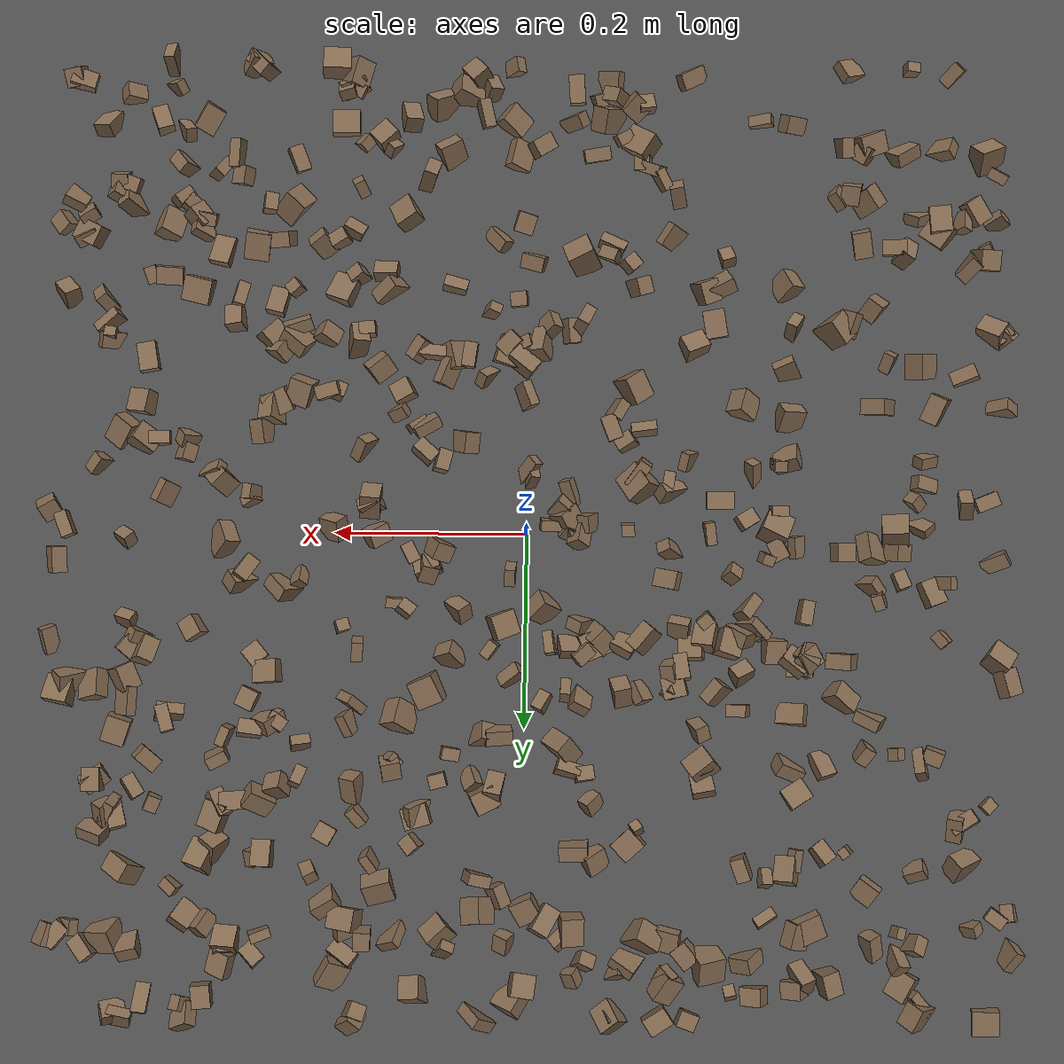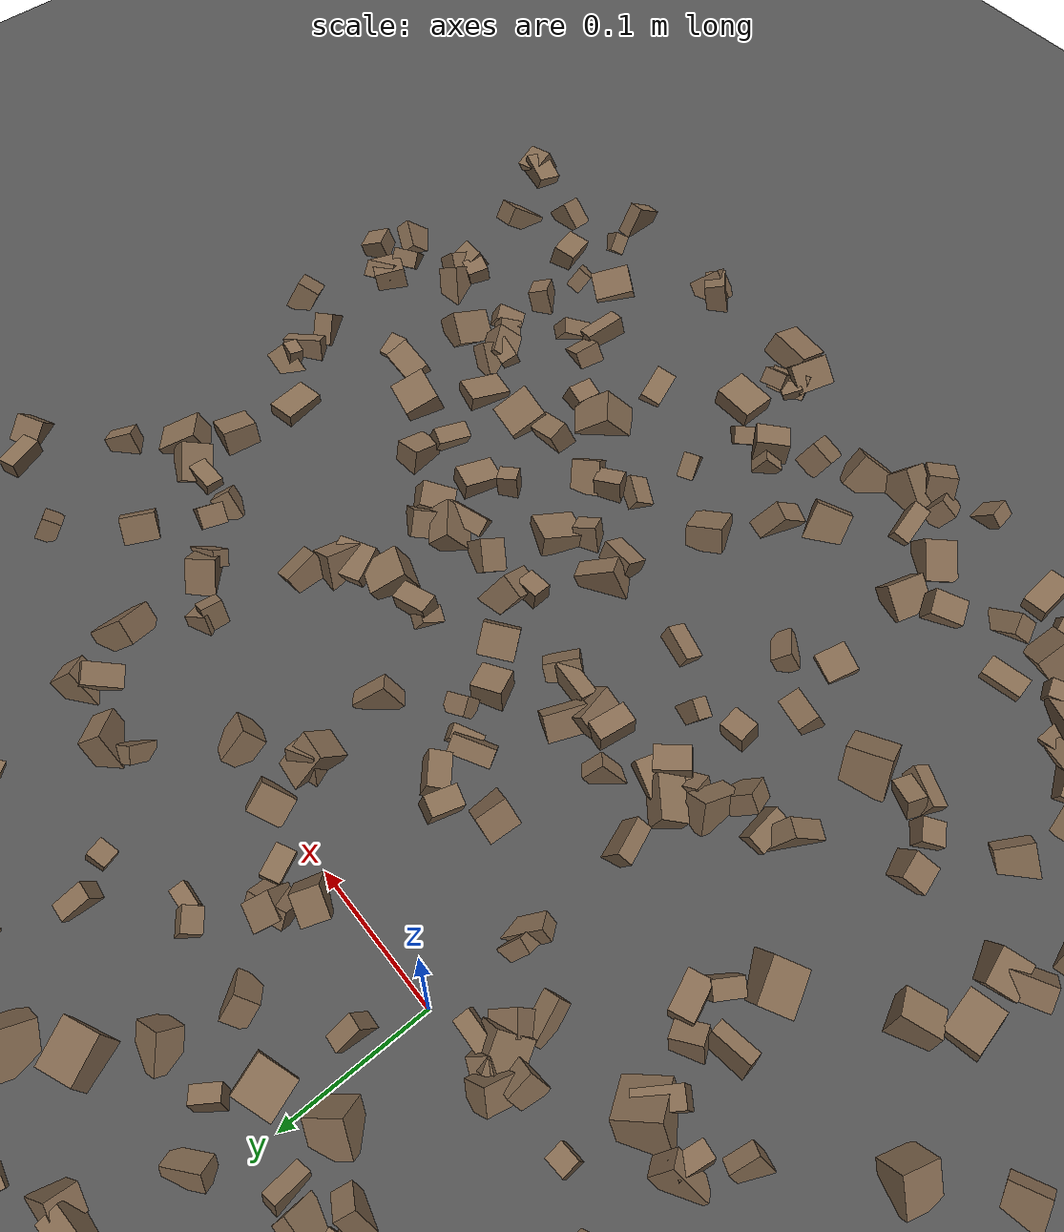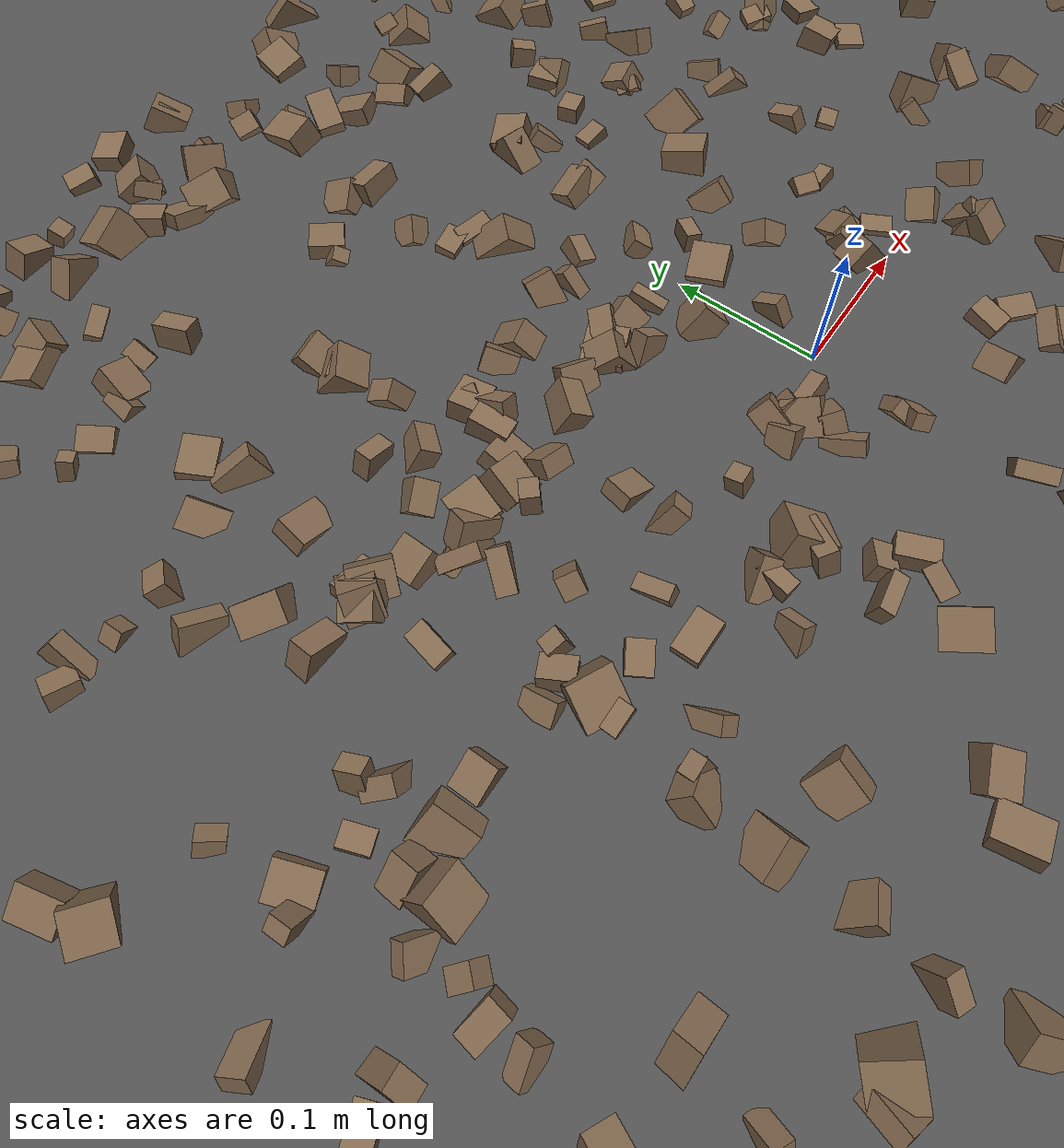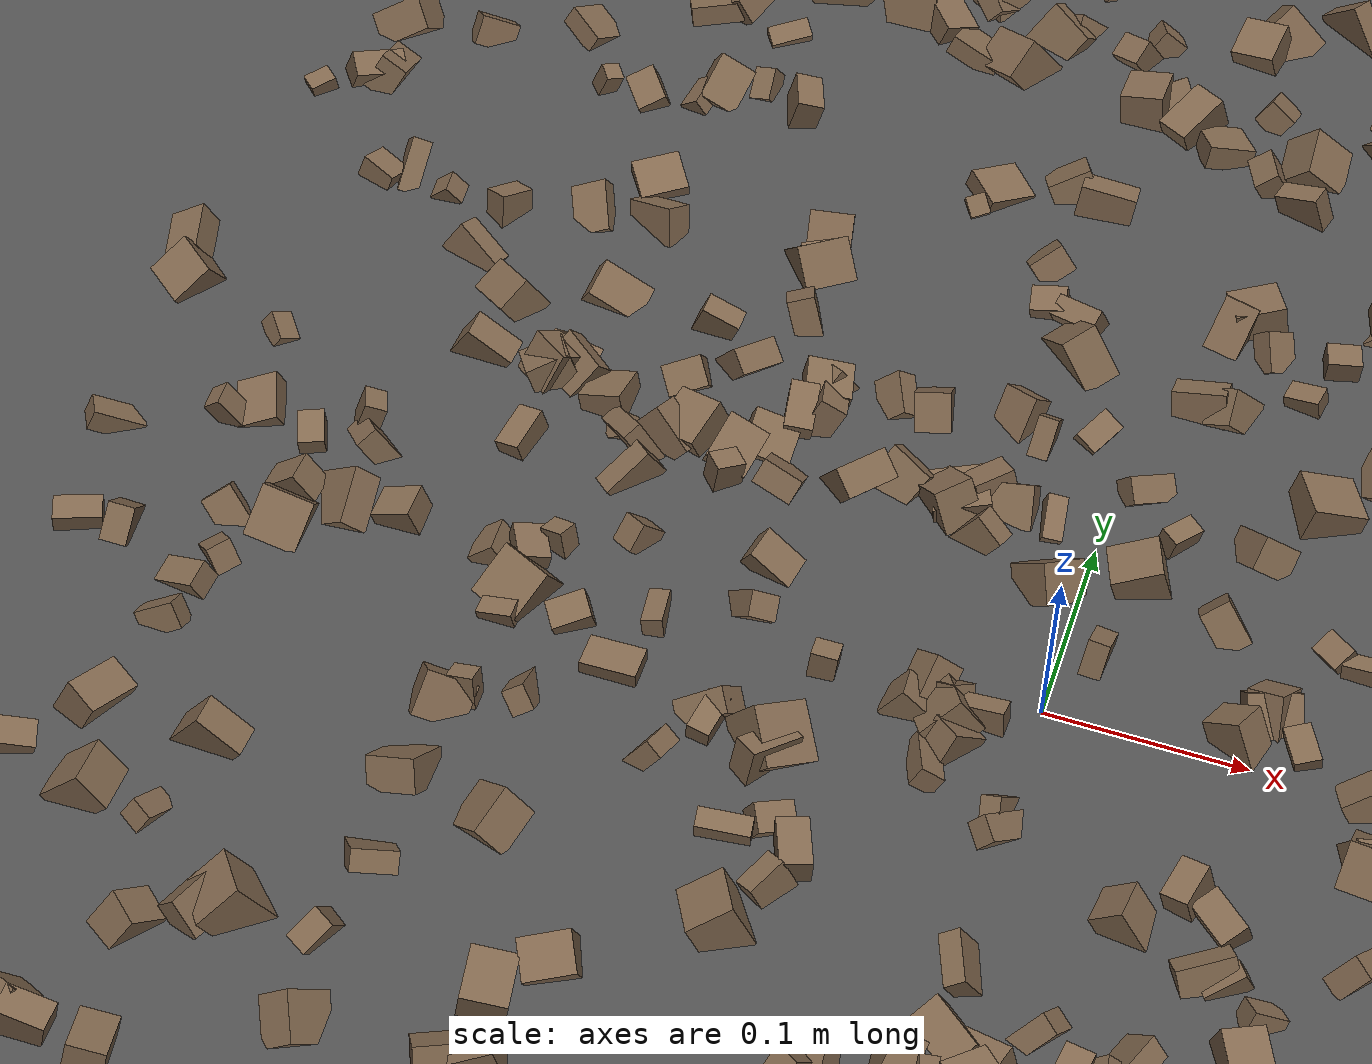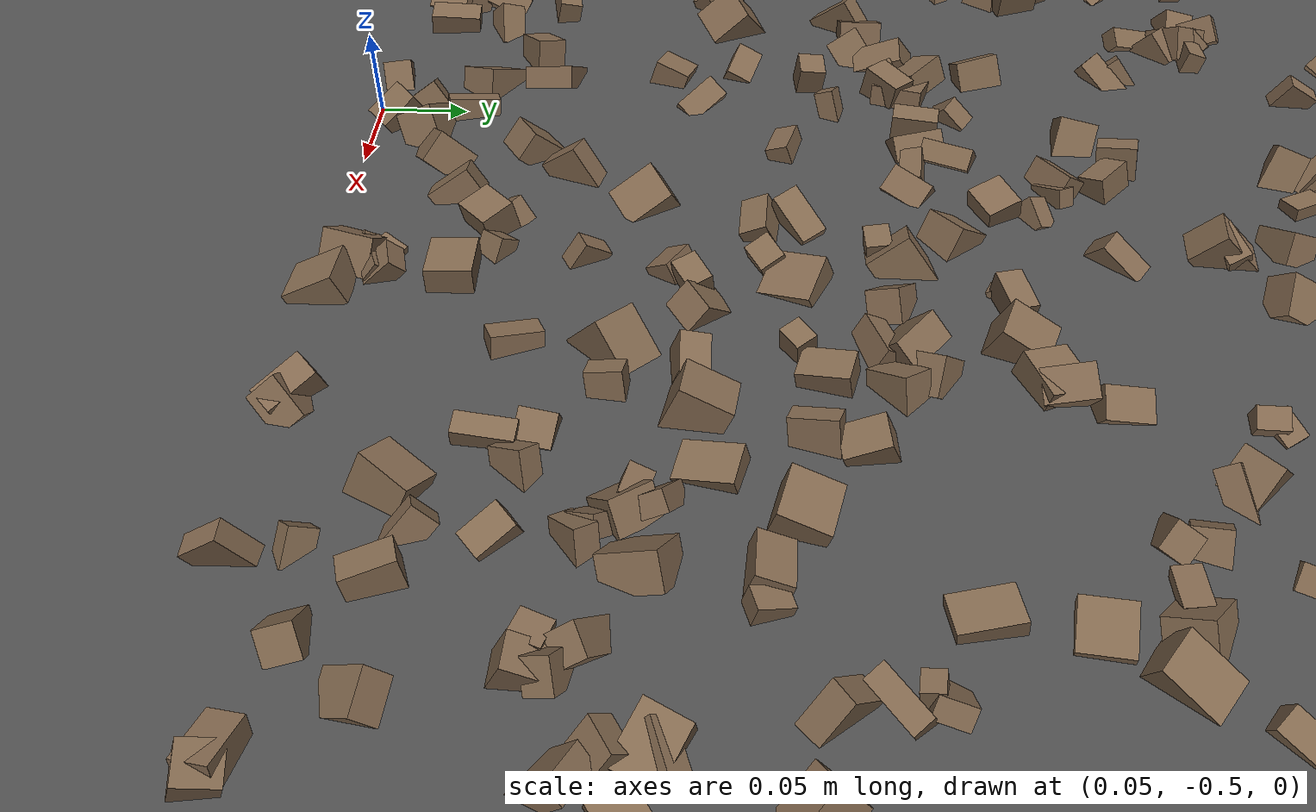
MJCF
<mujoco model="rocky_terrain_scene">
    <compiler angle="radian" inertiafromgeom="true" />
    <option timestep="0.002" gravity="0 0 -9.81" />

    <worldbody>
        <light name="sunlight" pos="5 5 5" dir="-1 -1 -1" diffuse="1 1 1" specular="0.5 0.5 0.5"
            ambient="0.5 0.5 0.5" />

        <geom name="ground_plane" type="plane" size="50 50 0.1" rgba="0.3 0.3 0.3 1" />

        <!-- These rocks below are movable, but ALL of them have to be placed in world body to roll!-->
        <body name="rock1" pos="0.4170508730227299 0.49215340456792067 0.0004191116563005227">
            <joint type="free" />
            <geom type="box" size="0.009688013354997024 0.007982686685362346 0.012219758022868739"
                quat="0.17116457323444498 0.25802965073811085 0.1463535122229797 0.4244522638044645"
                rgba="0.5 0.4 0.3 1" />
        </body>
        <body name="rock2" pos="0.07634828229090562 0.22599626192472688 9.434855280514886e-05">
            <joint type="free" />
            <geom type="box" size="0.006369403250974568 0.009247439543044042 0.007086415883351967"
                quat="0.06556363371867531 0.48765295424676763 0.4144740383810751 0.032309373653481986"
                rgba="0.5 0.4 0.3 1" />
        </body>
        <body name="rock3" pos="-0.4092336698860217 0.23028942533484142 0.0004079441822537071">
            <joint type="free" />
            <geom type="box" size="0.008692499190696782 0.01473528363721541 0.005384786014315259"
                quat="0.3005405772939974 0.0945103226732434 0.46696294442271497 0.1379861556100442"
                rgba="0.5 0.4 0.3 1" />
        </body>
        <body name="rock4" pos="-0.3648026980572482 -0.13959747046040294 0.0007113585012936732">
            <joint type="free" />
            <geom type="box" size="0.00823878435411287 0.0139818919945627 0.013277020209148904"
                quat="0.18486957779434723 0.328011819413882 0.3342754759049399 0.1528431268868308"
                rgba="0.5 0.4 0.3 1" />
        </body>
        <body name="rock5" pos="-0.2287328716830842 -0.019705856079916706 0.000649738279943044">
            <joint type="free" />
            <geom type="box" size="0.008136217503721045 0.007233841351511318 0.010174214152400078"
                quat="0.18646708345188512 0.16782824445686553 0.2777797747220404 0.36792489736920897"
                rgba="0.5 0.4 0.3 1" />
        </body>
        <body name="rock6" pos="0.18566741155887478 -0.4717461891676531 0.00026616324593745853">
            <joint type="free" />
            <geom type="box" size="0.007318002577123917 0.0057698507471849285 0.010858065136737597"
                quat="0.3318179003366499 0.3012500148355212 0.23011715324530754 0.1368149315825213"
                rgba="0.5 0.4 0.3 1" />
        </body>
        <body name="rock7" pos="0.10685292922339495 -0.3785816259579118 0.0006977750157727737">
            <joint type="free" />
            <geom type="box" size="0.007190158852491647 0.012033696405256531 0.013694013837849992"
                quat="0.07343802761438381 0.09084004798112566 0.6286780288160791 0.20704389558841133"
                rgba="0.5 0.4 0.3 1" />
        </body>
        <body name="rock8" pos="-0.32326310265843106 -0.36054843590807006 0.0006884451259822256">
            <joint type="free" />
            <geom type="box" size="0.005535016621139109 0.010925151351964391 0.009687770920503783"
                quat="0.4991287133711678 0.2672873323020453 0.22880246491163833 0.004781489415148514"
                rgba="0.5 0.4 0.3 1" />
        </body>
        <body name="rock9" pos="-0.11578304814071849 -0.05608397815851529 0.0005939469740643289">
            <joint type="free" />
            <geom type="box" size="0.014574961181005788 0.013080795957723806 0.014975359253107418"
                quat="0.30724190584849326 0.43699116118308945 0.2362344424014977 0.019532490566919636"
                rgba="0.5 0.4 0.3 1" />
        </body>
        <body name="rock10" pos="-0.08627783619306761 -0.30753744434358854 0.0004970447544367015">
            <joint type="free" />
            <geom type="box" size="0.013804380683441947 0.0071657127250436495 0.006230086906792665"
                quat="0.10798585398538517 0.0725843487190495 0.30974356004011067 0.5096862372554547"
                rgba="0.5 0.4 0.3 1" />
        </body>
        <body name="rock11" pos="0.0688504205616367 -0.46791286569424906 0.0008034315605742388">
            <joint type="free" />
            <geom type="box" size="0.011060340945806043 0.011687181908143541 0.014399483707302235"
                quat="0.2947600855773551 0.24629106122299205 0.09909961693431495 0.359849236265338"
                rgba="0.5 0.4 0.3 1" />
        </body>
        <body name="rock12" pos="0.4768865871185729 -0.34956219145448697 0.0004077032308042999">
            <joint type="free" />
            <geom type="box" size="0.005869760884665266 0.012362231590771952 0.01173151690894769"
                quat="0.4325293951004636 0.20335227561561053 0.2852941789558278 0.07882415032809804"
                rgba="0.5 0.4 0.3 1" />
        </body>
        <body name="rock13" pos="-0.14924240164367752 -0.04836099045496833 0.000530952597889418">
            <joint type="free" />
            <geom type="box" size="0.00902471545482346 0.006608649328194025 0.013995936474670859"
                quat="0.48204502497606666 0.04205587762689518 0.2772123706609461 0.19868672673609208"
                rgba="0.5 0.4 0.3 1" />
        </body>
        <body name="rock14" pos="-0.056531229738357225 0.09026322360679595 0.00026132012695016105">
            <joint type="free" />
            <geom type="box" size="0.006694346018907027 0.012185654665513268 0.008852928736518844"
                quat="0.2509185694125199 0.33744162032570396 0.31921662944140283 0.09242318082037332"
                rgba="0.5 0.4 0.3 1" />
        </body>
        <body name="rock15" pos="0.03575417608986664 0.1181713965153518 0.00039783348716960034">
            <joint type="free" />
            <geom type="box" size="0.005420841407608231 0.0111067381911363 0.009209151616863365"
                quat="0.08851116145453534 0.15786988144077127 0.39622100515464903 0.3573979519500444"
                rgba="0.5 0.4 0.3 1" />
        </body>
        <body name="rock16" pos="0.32687745125158485 0.4019165815557977 0.0007208484158325406">
            <joint type="free" />
            <geom type="box" size="0.011598017057292059 0.00823669239308672 0.008624783861214316"
                quat="0.4008756361910982 0.28904064105490745 0.0033439814462283253 0.30673974130776605"
                rgba="0.5 0.4 0.3 1" />
        </body>
        <body name="rock17" pos="-0.29096415701645695 0.12223310084458006 0.000288754236317616">
            <joint type="free" />
            <geom type="box" size="0.011834891601293989 0.01107880132132872 0.011282813438416268"
                quat="0.43415784811521796 0.3325523201080404 0.04221308332036151 0.19107674845638017"
                rgba="0.5 0.4 0.3 1" />
        </body>
        <body name="rock18" pos="-0.10871090785092852 0.3167634913019691 0.0002911855897348157">
            <joint type="free" />
            <geom type="box" size="0.011907715575734643 0.0053112918823950955 0.013631478828496742"
                quat="0.1130772513656152 0.18444385212451497 0.3871832317664606 0.31529566474340925"
                rgba="0.5 0.4 0.3 1" />
        </body>
        <body name="rock19" pos="0.4476935287668308 0.42790932862325504 0.0008211923323659416">
            <joint type="free" />
            <geom type="box" size="0.012702234777317134 0.01302041002116304 0.007759442658668849"
                quat="0.1287786316246599 0.19395843108348584 0.3311789930899982 0.34608394420185595"
                rgba="0.5 0.4 0.3 1" />
        </body>
        <body name="rock20" pos="-0.21398526925099792 0.03655242365698019 0.0007319853129964164">
            <joint type="free" />
            <geom type="box" size="0.007625178511032403 0.0076632216969747605 0.007210798757791401"
                quat="0.28755530948972924 0.33630355472605944 0.038918815505394166 0.3372223202788172"
                rgba="0.5 0.4 0.3 1" />
        </body>
        <body name="rock21" pos="0.2020890030535729 0.37883999480510877 3.3803558483278654e-05">
            <joint type="free" />
            <geom type="box" size="0.013791609217623953 0.01178673853396114 0.008049870881579548"
                quat="0.5143541160945619 0.25140313969911093 0.11559095405816859 0.11865179014815858"
                rgba="0.5 0.4 0.3 1" />
        </body>
        <body name="rock22" pos="-0.11371192245146622 -0.2631576126790791 0.000295567400333179">
            <joint type="free" />
            <geom type="box" size="0.009189268279948263 0.013572359140315866 0.00893442303442992"
                quat="0.28642007691267546 0.1347646912842538 0.23947417238339638 0.3393410594196744"
                rgba="0.5 0.4 0.3 1" />
        </body>
        <body name="rock23" pos="-0.34813665824694107 -0.3124563423162784 0.0009942405382761962">
            <joint type="free" />
            <geom type="box" size="0.013409255627583529 0.014569643782033646 0.009381892396615014"
                quat="0.25666294259839895 0.1992371472165799 0.3421991432857959 0.2019007668992252"
                rgba="0.5 0.4 0.3 1" />
        </body>
        <body name="rock24" pos="-0.3279310357936702 -0.41441635253645126 0.0006736444437363953">
            <joint type="free" />
            <geom type="box" size="0.010157322190625446 0.012849791034837188 0.006819824486601185"
                quat="0.3034787737446242 0.1642075147662923 0.26970467256377606 0.2626090389253075"
                rgba="0.5 0.4 0.3 1" />
        </body>
        <body name="rock25" pos="0.36720310531606914 0.18791210878058795 0.0001160289695399288">
            <joint type="free" />
            <geom type="box" size="0.006389481104737834 0.009925956231139739 0.014064494805209497"
                quat="0.21477691112239677 0.2892939364089877 0.13105767205541055 0.364871480413205"
                rgba="0.5 0.4 0.3 1" />
        </body>
        <body name="rock26" pos="-0.11973416516598434 -0.4571159759411867 0.000159757966801241">
            <joint type="free" />
            <geom type="box" size="0.008420925549500123 0.008678529671776198 0.008301964733933385"
                quat="0.20294907406705126 0.24983069567954516 0.21892313703663455 0.32829709321676903"
                rgba="0.5 0.4 0.3 1" />
        </body>
        <body name="rock27" pos="0.34656958571747565 0.39396529927563284 0.00014609477461714204">
            <joint type="free" />
            <geom type="box" size="0.012888279301207246 0.007618075334165942 0.011180839049903286"
                quat="0.28903026079659777 0.3626525874188219 0.05675847573789672 0.2915586760466836"
                rgba="0.5 0.4 0.3 1" />
        </body>
        <body name="rock28" pos="-0.30765692559512736 0.32269410840817525 0.0009229391369559722">
            <joint type="free" />
            <geom type="box" size="0.008089646249592946 0.00754722597983375 0.011088634339601403"
                quat="0.32075728850396196 0.43396847566279784 0.06519644868662115 0.180077787146619"
                rgba="0.5 0.4 0.3 1" />
        </body>
        <body name="rock29" pos="-0.3667751461770641 0.06088291012088243 0.0008410604282922507">
            <joint type="free" />
            <geom type="box" size="0.008009707802060742 0.014509421334610952 0.0058010445332233665"
                quat="0.19818726451240604 0.21398308400066152 0.3707859196508816 0.2170437318360509"
                rgba="0.5 0.4 0.3 1" />
        </body>
        <body name="rock30" pos="-0.2689456027951316 -0.2660922346669943 0.00020199734267292537">
            <joint type="free" />
            <geom type="box" size="0.012146008647109414 0.009589885085831713 0.012657673193031798"
                quat="0.022286447177203787 0.31939213800779837 0.4154964848591063 0.24282492995589158"
                rgba="0.5 0.4 0.3 1" />
        </body>
        <body name="rock31" pos="-0.2061208162040975 -0.2958020063752198 0.0009692883112831124">
            <joint type="free" />
            <geom type="box" size="0.008336862462538595 0.006516588704549587 0.007171834380292336"
                quat="0.14397041912496564 0.28017349319887974 0.21942571155748633 0.35643037611866824"
                rgba="0.5 0.4 0.3 1" />
        </body>
        <body name="rock32" pos="-0.3072973379660665 0.2322628882743185 0.0005641284012954976">
            <joint type="free" />
            <geom type="box" size="0.005148979089315088 0.013981945150495428 0.009844321514329778"
                quat="0.47707892202930374 0.03086144267174331 0.32763373362636977 0.16442590167258317"
                rgba="0.5 0.4 0.3 1" />
        </body>
        <body name="rock33" pos="-0.32827267180001796 0.012194420735492928 0.00025133747944106223">
            <joint type="free" />
            <geom type="box" size="0.009704361945729253 0.00919705321686494 0.01077845200905407"
                quat="0.30259905975828205 0.1906891369795625 0.20979598212078343 0.296915821141372"
                rgba="0.5 0.4 0.3 1" />
        </body>
        <body name="rock34" pos="-0.09203769998797462 -0.13293166769006126 0.00019693867869299397">
            <joint type="free" />
            <geom type="box" size="0.00596077434158151 0.011482680741843629 0.01034017127554544"
                quat="0.20291111794491096 0.017070079307832074 0.3679318806238598 0.4120869221233971"
                rgba="0.5 0.4 0.3 1" />
        </body>
        <body name="rock35" pos="0.14595396114434367 -0.40761655334762426 0.0008508287778236093">
            <joint type="free" />
            <geom type="box" size="0.005892250063465271 0.007466743140490649 0.007330539664661061"
                quat="0.16859366746563378 0.1329075850218554 0.21573910249281603 0.48275964501969476"
                rgba="0.5 0.4 0.3 1" />
        </body>
        <body name="rock36" pos="-0.2889421530665758 0.07602720832944199 0.00018941506015963838">
            <joint type="free" />
            <geom type="box" size="0.012477128557718715 0.009756226098685705 0.006761331580200489"
                quat="0.2901032487550359 0.25551285314394356 0.18926367215802137 0.26512022594299917"
                rgba="0.5 0.4 0.3 1" />
        </body>
        <body name="rock37" pos="0.36448027000684924 -0.38713076830381954 2.8989610578538104e-05">
            <joint type="free" />
            <geom type="box" size="0.010833289706672054 0.012408759290540236 0.007240259626414232"
                quat="0.06394542024518533 0.2457274982217666 0.36940451692024157 0.3209225646128065"
                rgba="0.5 0.4 0.3 1" />
        </body>
        <body name="rock38" pos="-0.14762590835885236 0.41250739115975 0.00033636902435096573">
            <joint type="free" />
            <geom type="box" size="0.0052396059902773875 0.012057841961136549 0.014517631388185879"
                quat="0.10663815401201454 0.49067084495252444 0.052314973876307784 0.3503760271591532"
                rgba="0.5 0.4 0.3 1" />
        </body>
        <body name="rock39" pos="-0.039099643440324905 0.2180946705879092 0.000913049617394621">
            <joint type="free" />
            <geom type="box" size="0.010009619432139124 0.014531981316216764 0.014881265634755877"
                quat="0.47306862422188006 0.23835353344033894 0.047927580239988846 0.2406502620977921"
                rgba="0.5 0.4 0.3 1" />
        </body>
        <body name="rock40" pos="-0.4544611935848253 0.28950569707526885 3.5373874878186554e-05">
            <joint type="free" />
            <geom type="box" size="0.014271023043670283 0.012678777743441826 0.00729952333474463"
                quat="0.32901109443316673 0.43558128911691557 0.1791256111072922 0.056282005342625514"
                rgba="0.5 0.4 0.3 1" />
        </body>
        <body name="rock41" pos="-0.49446081450904167 -0.13923224744592433 0.0004200961240305199">
            <joint type="free" />
            <geom type="box" size="0.006570280463072294 0.012314605943578881 0.010636579623460072"
                quat="0.3568035189552799 0.20635287029663285 0.08166533762442219 0.3551782731236651"
                rgba="0.5 0.4 0.3 1" />
        </body>
        <body name="rock42" pos="0.3437437888520207 -0.31972345474516495 0.0006646837966553615">
            <joint type="free" />
            <geom type="box" size="0.010919568023494232 0.005450341241056405 0.011565407047230414"
                quat="0.3056757815318504 0.24444947241090426 0.06816871931680038 0.381706026740445"
                rgba="0.5 0.4 0.3 1" />
        </body>
        <body name="rock43" pos="0.24776090459811728 -0.3454280393384471 0.0007437094238290496">
            <joint type="free" />
            <geom type="box" size="0.014594080726053005 0.01470096153096482 0.01221633113010799"
                quat="0.4314700523933053 0.27387496160625685 0.264332360239466 0.030322625760971802"
                rgba="0.5 0.4 0.3 1" />
        </body>
        <body name="rock44" pos="0.056604965130189866 -0.486364328688893 0.0006394691946376781">
            <joint type="free" />
            <geom type="box" size="0.009869198042251958 0.013252560925704832 0.011912887374016412"
                quat="0.2708423643360071 0.4632077493373161 0.1745635394941596 0.09138634683251709"
                rgba="0.5 0.4 0.3 1" />
        </body>
        <body name="rock45" pos="0.17910353858094286 -0.20209947932097372 0.0002069864394493639">
            <joint type="free" />
            <geom type="box" size="0.013857042331054597 0.0129965855681816 0.00902124240364554"
                quat="0.43819287797594497 0.10630877846383195 0.31382065052348124 0.14167769303674183"
                rgba="0.5 0.4 0.3 1" />
        </body>
        <body name="rock46" pos="-0.22426592755347474 -0.13961752876607392 0.0008466341262520176">
            <joint type="free" />
            <geom type="box" size="0.01262896457572851 0.009982231274195646 0.012751168874323062"
                quat="0.37921565842528415 0.22148977525002853 0.07833428818494516 0.3209602781397421"
                rgba="0.5 0.4 0.3 1" />
        </body>
        <body name="rock47" pos="0.2103257868452637 -0.20845366837522306 0.0008714024843146969">
            <joint type="free" />
            <geom type="box" size="0.009091439032302046 0.008988842739304885 0.01106324624539724"
                quat="0.3478693702718571 0.26605905107983924 0.07057916178791741 0.31549241686038626"
                rgba="0.5 0.4 0.3 1" />
        </body>
        <body name="rock48" pos="-0.1865239005113576 0.10291782977508701 0.0008213196786309267">
            <joint type="free" />
            <geom type="box" size="0.01310037726373526 0.012945146540756243 0.011116368952379063"
                quat="0.3545854200526453 0.12014065504230437 0.47833804621691534 0.04693587868813506"
                rgba="0.5 0.4 0.3 1" />
        </body>
        <body name="rock49" pos="-0.3581241551550367 0.04866896806613463 0.000484142778056987">
            <joint type="free" />
            <geom type="box" size="0.010851456356982085 0.010631964687399218 0.006208377141487114"
                quat="0.26544514688773185 0.02480339889054443 0.3026282059937929 0.4071232482279307"
                rgba="0.5 0.4 0.3 1" />
        </body>
        <body name="rock50" pos="-0.40365657337197625 0.33955803366966264 0.0004651857994030547">
            <joint type="free" />
            <geom type="box" size="0.006758008315212597 0.008075601667074557 0.0108527274315728"
                quat="0.2334032060212686 0.13367998059733122 0.4474661126902508 0.18545070069114938"
                rgba="0.5 0.4 0.3 1" />
        </body>
        <body name="rock51" pos="0.3477587689052408 -0.3317910368221597 0.0006518056556027661">
            <joint type="free" />
            <geom type="box" size="0.009887323192923524 0.009009622605849182 0.011745181316153026"
                quat="0.3422973956014063 0.38777879820649114 0.00275718822023564 0.267166617971867"
                rgba="0.5 0.4 0.3 1" />
        </body>
        <body name="rock52" pos="-0.47932952061856526 -0.4062254310308703 0.00019543325882921214">
            <joint type="free" />
            <geom type="box" size="0.013613771105659245 0.010562584443910252 0.014855787037918969"
                quat="0.3797783613760978 0.05436535406540052 0.32707007334364707 0.2387862112148546"
                rgba="0.5 0.4 0.3 1" />
        </body>
        <body name="rock53" pos="0.2515395310621755 0.056495094723158834 0.0009148176081467864">
            <joint type="free" />
            <geom type="box" size="0.007823408128699597 0.013663060383329755 0.013653026066747807"
                quat="0.2930031232056602 0.37572080573675026 0.2852909791141689 0.045985091943420625"
                rgba="0.5 0.4 0.3 1" />
        </body>
        <body name="rock54" pos="0.48379727967904484 -0.24902460014928318 0.00019891357616271343">
            <joint type="free" />
            <geom type="box" size="0.008658094098050954 0.010206437050724021 0.011884892736103648"
                quat="0.24124085103354076 0.5018567300722923 0.0788409554924545 0.1780614634017124"
                rgba="0.5 0.4 0.3 1" />
        </body>
        <body name="rock55" pos="0.3035675573973584 -0.37606769189185096 0.00015877105105006805">
            <joint type="free" />
            <geom type="box" size="0.009488027758410626 0.007534332364483786 0.008638251343420467"
                quat="0.20281351383668908 0.3374461838458279 0.3106706947739843 0.1490696075434986"
                rgba="0.5 0.4 0.3 1" />
        </body>
        <body name="rock56" pos="0.4463725746474214 -0.06947216100584352 0.0005069379877576306">
            <joint type="free" />
            <geom type="box" size="0.006559115697536367 0.009208419808184497 0.010310130415964944"
                quat="0.04138778178805929 0.23677215137364035 0.3962861672920311 0.32555389954626934"
                rgba="0.5 0.4 0.3 1" />
        </body>
        <body name="rock57" pos="0.11540733706626405 -0.11512823452438536 0.0003579657453763233">
            <joint type="free" />
            <geom type="box" size="0.005202187001461826 0.005273518794005159 0.010721024317003525"
                quat="0.23478535404659184 0.11075744684125886 0.2704121069947823 0.384045092117367"
                rgba="0.5 0.4 0.3 1" />
        </body>
        <body name="rock58" pos="-0.2306380796217261 0.4323163500596411 0.00048493491910143994">
            <joint type="free" />
            <geom type="box" size="0.013509865580259375 0.008235569246082729 0.011709251439715256"
                quat="0.03550854407480919 0.5938400741681568 0.10156918148634642 0.2690822002706875"
                rgba="0.5 0.4 0.3 1" />
        </body>
        <body name="rock59" pos="0.4439995973384583 -0.24208240257603553 0.0004301025498167399">
            <joint type="free" />
            <geom type="box" size="0.012794798999040333 0.011491178924510563 0.006712018021822917"
                quat="0.007149369877143053 0.32687615620809063 0.27382711275735117 0.3921473611574153"
                rgba="0.5 0.4 0.3 1" />
        </body>
        <body name="rock60" pos="-0.04279719484917388 -0.006552360265438817 0.0005011505157354029">
            <joint type="free" />
            <geom type="box" size="0.008022612708410239 0.007524098447034156 0.008212311753418808"
                quat="0.2444673804319722 0.2811671427078807 0.03191500447058991 0.4424504723895572"
                rgba="0.5 0.4 0.3 1" />
        </body>
        <body name="rock61" pos="0.16314268469330717 0.41333326416221905 0.000529863407729244">
            <joint type="free" />
            <geom type="box" size="0.013314030859340863 0.010061467463736321 0.008670543190269102"
                quat="0.06805203179313449 0.42728290691038967 0.05758857026198949 0.4470764910344864"
                rgba="0.5 0.4 0.3 1" />
        </body>
        <body name="rock62" pos="0.4179764196076122 -0.34379737837920177 0.0005199742777182514">
            <joint type="free" />
            <geom type="box" size="0.00791938561114914 0.009081109532363584 0.014534947529628483"
                quat="0.564000562821598 0.1678834527754923 0.17851631216753783 0.08959967223537185"
                rgba="0.5 0.4 0.3 1" />
        </body>
        <body name="rock63" pos="0.4419833640432993 0.2570039915365796 0.0004571648206644783">
            <joint type="free" />
            <geom type="box" size="0.009478013494036437 0.005481913887708351 0.01356159135736366"
                quat="0.2884970184711119 0.06720969771409442 0.3629193395512753 0.2813739442635183"
                rgba="0.5 0.4 0.3 1" />
        </body>
        <body name="rock64" pos="0.12720855111806306 -0.4412208489504619 0.000983828423886375">
            <joint type="free" />
            <geom type="box" size="0.00901542180061076 0.013297768278943072 0.00927835120676112"
                quat="0.44294472518849975 0.08834546665383963 0.32203737392124593 0.14667243423641463"
                rgba="0.5 0.4 0.3 1" />
        </body>
        <body name="rock65" pos="-0.06286463465766945 0.43578820592953404 0.0002967264894251193">
            <joint type="free" />
            <geom type="box" size="0.00852366325938725 0.012475090848996027 0.007224011006053379"
                quat="0.1585346284262661 0.008156263843277715 0.3219891606498461 0.5113199470806101"
                rgba="0.5 0.4 0.3 1" />
        </body>
        <body name="rock66" pos="0.3663250281652207 -0.3518622577652908 0.00022751748615082513">
            <joint type="free" />
            <geom type="box" size="0.010106958537795554 0.010230082288140145 0.006186778611607024"
                quat="0.3818738814536843 0.34941778360886677 0.04018466134985058 0.22852367358759823"
                rgba="0.5 0.4 0.3 1" />
        </body>
        <body name="rock67" pos="0.34011249322624404 -0.4371561984596165 0.0005151640032693358">
            <joint type="free" />
            <geom type="box" size="0.010648909158471661 0.013660313760946594 0.014171820750754127"
                quat="0.17327010122243824 0.038575333097266074 0.4661183642293963 0.3220362014508993"
                rgba="0.5 0.4 0.3 1" />
        </body>
        <body name="rock68" pos="0.35428178750196937 -0.09727302862090281 0.0008149486265956537">
            <joint type="free" />
            <geom type="box" size="0.0073245158836042 0.007575105653538427 0.010068897148176853"
                quat="0.4531323909292809 0.10024455956637364 0.2008267468314896 0.24579630267285588"
                rgba="0.5 0.4 0.3 1" />
        </body>
        <body name="rock69" pos="-0.11549170682276866 -0.4144088208511235 0.00042879589508723615">
            <joint type="free" />
            <geom type="box" size="0.013404400412412813 0.01388561152525088 0.01485736129321092"
                quat="0.25682236289459337 0.3895556793245233 0.22280810803337228 0.13081384974751106"
                rgba="0.5 0.4 0.3 1" />
        </body>
        <body name="rock70" pos="0.12880939849781725 0.18844233449238335 0.0007131938656533216">
            <joint type="free" />
            <geom type="box" size="0.01400581293856849 0.010866399199102277 0.014591792269863964"
                quat="0.3589730207883063 0.23833265355851788 0.05338489509354697 0.3493094305596289"
                rgba="0.5 0.4 0.3 1" />
        </body>
        <body name="rock71" pos="-0.16978019768993224 0.4925396848899488 0.00028497403383310105">
            <joint type="free" />
            <geom type="box" size="0.008506934436457586 0.00730318688736855 0.00985756696105072"
                quat="0.32323089431604707 0.2744135192385976 0.1877068799920646 0.2146487064532907"
                rgba="0.5 0.4 0.3 1" />
        </body>
        <body name="rock72" pos="0.13458424582760542 -0.12699121503264854 1.962237970899183e-05">
            <joint type="free" />
            <geom type="box" size="0.006502744909607614 0.005815312087005083 0.009040231616852586"
                quat="0.20948846712454003 0.16717577293027766 0.4355432699041951 0.1877924900409872"
                rgba="0.5 0.4 0.3 1" />
        </body>
        <body name="rock73" pos="0.3001174316371421 0.27731942492947825 0.0003913267607906412">
            <joint type="free" />
            <geom type="box" size="0.008208837512371545 0.00948866768924398 0.013432891635019862"
                quat="0.5241575134913066 0.012918093890980307 0.4136586224359281 0.049265770181785074"
                rgba="0.5 0.4 0.3 1" />
        </body>
        <body name="rock74" pos="-0.12365734530013639 0.10527698982544853 0.0009194292711130239">
            <joint type="free" />
            <geom type="box" size="0.008114305488765673 0.013412394109743549 0.01453790483117915"
                quat="0.021667309356309762 0.24612981581616417 0.3416669003087532 0.3905359745187729"
                rgba="0.5 0.4 0.3 1" />
        </body>
        <body name="rock75" pos="0.24514937007818838 -0.39435459468397105 0.00011170408490641881">
            <joint type="free" />
            <geom type="box" size="0.007553437104275959 0.007532029719878382 0.013482167050713142"
                quat="0.436623742511712 0.3995296510869584 0.021249583059265872 0.14259702334206367"
                rgba="0.5 0.4 0.3 1" />
        </body>
        <body name="rock76" pos="0.263103655977989 -0.2417289722684003 0.0003226938995165796">
            <joint type="free" />
            <geom type="box" size="0.013399212685533832 0.010132375388053356 0.009445733083295122"
                quat="0.25755037466573283 0.3029280497669135 0.2016340522491428 0.23788752331821086"
                rgba="0.5 0.4 0.3 1" />
        </body>
        <body name="rock77" pos="-0.3325321757751084 0.32060905309960475 0.0005102045362139166">
            <joint type="free" />
            <geom type="box" size="0.005008088043558761 0.00500281512056399 0.013590786274505686"
                quat="0.6269854732330287 0.037282299409060665 0.11326700953875969 0.22246521781915102"
                rgba="0.5 0.4 0.3 1" />
        </body>
        <body name="rock78" pos="0.17656604078173133 0.26163569425218614 0.00045124075902656127">
            <joint type="free" />
            <geom type="box" size="0.014678259451996883 0.008979276431751889 0.008958149127840438"
                quat="0.2609082755365789 0.24369665393158269 0.3724691082149849 0.12292596231685346"
                rgba="0.5 0.4 0.3 1" />
        </body>
        <body name="rock79" pos="0.10045970150829997 0.16130545024123588 0.0005630376061834447">
            <joint type="free" />
            <geom type="box" size="0.014770362786029907 0.010599885783013727 0.014462935800360788"
                quat="0.1877820865027122 0.2017093405339677 0.3696578764611062 0.24085069650221394"
                rgba="0.5 0.4 0.3 1" />
        </body>
        <body name="rock80" pos="0.313840765389495 0.2816542207022521 0.0004452932106501142">
            <joint type="free" />
            <geom type="box" size="0.014345289146132693 0.0076721715510988525 0.010544816869164066"
                quat="0.028059246421377807 0.2962413320737208 0.48246304446089766 0.19323637704400382"
                rgba="0.5 0.4 0.3 1" />
        </body>
        <body name="rock81" pos="-0.19803971502671902 0.15998875201500462 0.000979375679550444">
            <joint type="free" />
            <geom type="box" size="0.0069898707659660445 0.01116235270825124 0.012497307752171134"
                quat="0.012281076384750404 0.2641214925115759 0.36321652074692234 0.36038091035675135"
                rgba="0.5 0.4 0.3 1" />
        </body>
        <body name="rock82" pos="0.18292197105837804 0.43094067532351754 0.00018226259576835347">
            <joint type="free" />
            <geom type="box" size="0.014352405142818075 0.005794528964107959 0.008329396252843903"
                quat="0.09560161306126468 0.15019415982835146 0.2806187256200803 0.4735855014903036"
                rgba="0.5 0.4 0.3 1" />
        </body>
        <body name="rock83" pos="0.170607280750406 0.4890060984926494 0.0008343053950396938">
            <joint type="free" />
            <geom type="box" size="0.007979419829779967 0.014325254793517903 0.00851642021229424"
                quat="0.29821269788171606 0.2924445845565399 0.12438716319068156 0.28495555437106246"
                rgba="0.5 0.4 0.3 1" />
        </body>
        <body name="rock84" pos="0.40232870592592795 0.4241665915678755 0.0005281291740522459">
            <joint type="free" />
            <geom type="box" size="0.010993662170049299 0.00770899356810094 0.01484087008628173"
                quat="0.23953200432797594 0.6669849769849838 0.08315416315762005 0.010328855529420216"
                rgba="0.5 0.4 0.3 1" />
        </body>
        <body name="rock85" pos="-0.0008036267421258625 -0.06911919422177037 0.00031456905987196026">
            <joint type="free" />
            <geom type="box" size="0.014850871026144595 0.005563451064174556 0.0066811547986736905"
                quat="0.3299068522667976 0.3813827400857675 0.2869505245767369 0.0017598830706979328"
                rgba="0.5 0.4 0.3 1" />
        </body>
        <body name="rock86" pos="0.1358893190196574 0.23404549030942923 0.00020844683769557238">
            <joint type="free" />
            <geom type="box" size="0.005152646101507039 0.007327677673669314 0.007962815878364577"
                quat="0.39153793531037934 0.3038459332843827 0.02986465355735411 0.2747514778478839"
                rgba="0.5 0.4 0.3 1" />
        </body>
        <body name="rock87" pos="-0.3841624994957701 0.4291182585270369 0.0004807741109622944">
            <joint type="free" />
            <geom type="box" size="0.014920278300670674 0.007982586950393326 0.0072124653604954845"
                quat="0.19554001354988315 0.2993610797134187 0.08521757055936026 0.41988133617733797"
                rgba="0.5 0.4 0.3 1" />
        </body>
        <body name="rock88" pos="0.15400861715027303 -0.4188299848348419 8.053818559836657e-05">
            <joint type="free" />
            <geom type="box" size="0.009788413953910266 0.014913430265016864 0.01183882943342927"
                quat="0.1222312328108943 0.17972069696813325 0.32612739960882076 0.3719206706121518"
                rgba="0.5 0.4 0.3 1" />
        </body>
        <body name="rock89" pos="0.1786421075228649 0.1749003831502992 0.0008443176735778027">
            <joint type="free" />
            <geom type="box" size="0.005153508387979169 0.01223556855134577 0.01077454184713486"
                quat="0.14555924024574549 0.4762092694391696 0.23576891803063377 0.14246257228445108"
                rgba="0.5 0.4 0.3 1" />
        </body>
        <body name="rock90" pos="-0.47640750413036315 -0.296154580693741 0.000635065535079125">
            <joint type="free" />
            <geom type="box" size="0.010595278381882865 0.011823588942863367 0.013557774124954767"
                quat="0.10802798933605261 0.4311683985153788 0.4249413163013676 0.035862295847201055"
                rgba="0.5 0.4 0.3 1" />
        </body>
        <body name="rock91" pos="0.17412486465499066 0.11868500258087666 0.00029953317044365024">
            <joint type="free" />
            <geom type="box" size="0.010981672790203307 0.010560864922396915 0.005830031649810289"
                quat="0.09799361766915204 0.3952214963406712 0.07342185607976473 0.433363029910412"
                rgba="0.5 0.4 0.3 1" />
        </body>
        <body name="rock92" pos="0.10676216127849014 -0.11489545623549935 0.0003322113138510697">
            <joint type="free" />
            <geom type="box" size="0.014212234246216225 0.01045576743887034 0.006257860389998595"
                quat="0.5096279873126579 0.2847435892327639 0.04488418186732854 0.1607442415872497"
                rgba="0.5 0.4 0.3 1" />
        </body>
        <body name="rock93" pos="0.07763126944006848 0.12503378550624056 0.00017970792261257486">
            <joint type="free" />
            <geom type="box" size="0.008592972789125701 0.012498275235484716 0.010692268922160932"
                quat="0.060850810430432944 0.42626906771706896 0.2540361918850079 0.2588439299674901"
                rgba="0.5 0.4 0.3 1" />
        </body>
        <body name="rock94" pos="0.02390475122368496 0.09238547051096047 0.00040161967823792424">
            <joint type="free" />
            <geom type="box" size="0.012803734385700736 0.011744722698113663 0.013129589757243432"
                quat="0.2572327070932351 0.15530487891925543 0.2631489983813579 0.3243134156061517"
                rgba="0.5 0.4 0.3 1" />
        </body>
        <body name="rock95" pos="-0.47830509223947004 -0.041595574666563495 0.00040327653924525933">
            <joint type="free" />
            <geom type="box" size="0.007417997187514614 0.007710979430734413 0.012199741447863795"
                quat="0.20041792751657694 0.19911125530596122 0.3102831833976272 0.29018763377983464"
                rgba="0.5 0.4 0.3 1" />
        </body>
        <body name="rock96" pos="0.1990795270192356 -0.3086196658511994 0.000794829367656778">
            <joint type="free" />
            <geom type="box" size="0.009488886902284999 0.012840182049799496 0.006916719467941293"
                quat="0.3644761157239233 0.4213065452205494 0.14739449101037594 0.06682284804515133"
                rgba="0.5 0.4 0.3 1" />
        </body>
        <body name="rock97" pos="-0.3909911747591408 -0.40884240918530235 0.0004533807741039878">
            <joint type="free" />
            <geom type="box" size="0.007073956467930449 0.011063763314199188 0.014553448565457566"
                quat="0.3212351489716022 0.05621141775185305 0.3337253759548178 0.2888280573217269"
                rgba="0.5 0.4 0.3 1" />
        </body>
        <body name="rock98" pos="-0.10540338312400521 -0.008677620181949286 0.00033063775822300435">
            <joint type="free" />
            <geom type="box" size="0.006100357253264721 0.011881879696482682 0.006710317579044592"
                quat="0.2626503388164059 0.22161446133372778 0.2949661509373956 0.22076904891247068"
                rgba="0.5 0.4 0.3 1" />
        </body>
        <body name="rock99" pos="-0.3607914144442571 -0.24390127875156542 0.0004042604339548016">
            <joint type="free" />
            <geom type="box" size="0.00928251052834849 0.010816115793397082 0.011604108006625275"
                quat="0.17664663150676016 0.10923242797001514 0.17178716302727623 0.5423337774959485"
                rgba="0.5 0.4 0.3 1" />
        </body>
        <body name="rock100" pos="0.014363715692008783 0.14500473748254683 0.00014228364639242008">
            <joint type="free" />
            <geom type="box" size="0.00699749583549563 0.006346024052109811 0.012940239295062151"
                quat="0.05088857187031652 0.29990486524753296 0.33044452073093855 0.31876204215121196"
                rgba="0.5 0.4 0.3 1" />
        </body>
        <body name="rock101" pos="0.4169410811907125 0.007065102718762484 0.0006904746194570321">
            <joint type="free" />
            <geom type="box" size="0.009277198380455688 0.007601028670550308 0.006689466381567229"
                quat="0.04514081975661284 0.20705184671168023 0.23564174720975908 0.5121655863219479"
                rgba="0.5 0.4 0.3 1" />
        </body>
        <body name="rock102" pos="-0.1366147124007162 -0.3764914408675757 0.0006105432808219011">
            <joint type="free" />
            <geom type="box" size="0.011311867318821094 0.005043869390250885 0.01181792420887559"
                quat="0.0957733718991918 0.3265794075691939 0.5593149400708279 0.018332280460786242"
                rgba="0.5 0.4 0.3 1" />
        </body>
        <body name="rock103" pos="-0.2724175932890509 0.23652447058087855 0.0005707493088545126">
            <joint type="free" />
            <geom type="box" size="0.007255089757460683 0.010273946835966734 0.014816545335836512"
                quat="0.4150508967811333 0.2043878718970555 0.21480656599408662 0.1657546653277245"
                rgba="0.5 0.4 0.3 1" />
        </body>
        <body name="rock104" pos="0.35546478218335376 -0.3438567585724174 0.0003683287629686226">
            <joint type="free" />
            <geom type="box" size="0.008453247399921014 0.010358713942430216 0.005518407748618056"
                quat="0.07351604636652323 0.4865114331027898 0.2518869579275503 0.1880855626031367"
                rgba="0.5 0.4 0.3 1" />
        </body>
        <body name="rock105" pos="0.27985050186885874 0.12654597061681205 0.000288591328411538">
            <joint type="free" />
            <geom type="box" size="0.010174580550867604 0.005360220457420905 0.01019674659965708"
                quat="0.15089731788824606 0.16397361804298935 0.30407163570851675 0.3810574283602479"
                rgba="0.5 0.4 0.3 1" />
        </body>
        <body name="rock106" pos="0.26627057038879653 -0.12763391587627326 0.0005960483433663584">
            <joint type="free" />
            <geom type="box" size="0.013013511672104724 0.009009694143756419 0.013811614364343375"
                quat="0.38693846901613044 0.16249680385068974 0.05043883533477729 0.40012589179840263"
                rgba="0.5 0.4 0.3 1" />
        </body>
        <body name="rock107" pos="0.0429527545477798 -0.47372795555702785 0.0006551740701924743">
            <joint type="free" />
            <geom type="box" size="0.011796204263455092 0.00873541760390023 0.007396536890193792"
                quat="0.19885722374822093 0.24679080982992976 0.143584670101809 0.4107672963200403"
                rgba="0.5 0.4 0.3 1" />
        </body>
        <body name="rock108" pos="-0.15224179197479015 0.15537564083270639 0.0003978373496929147">
            <joint type="free" />
            <geom type="box" size="0.006449652568104404 0.010047903522294493 0.009759870029444112"
                quat="0.1270133372789537 0.15763136870533637 0.593870719167254 0.12148457484845596"
                rgba="0.5 0.4 0.3 1" />
        </body>
        <body name="rock109" pos="0.06182604895799981 -0.18793737540373268 0.0009466612809436533">
            <joint type="free" />
            <geom type="box" size="0.012796804460091047 0.014691589772064174 0.007029264590489248"
                quat="0.269294310754396 0.2659406022556998 0.23588540084677964 0.22887968614312448"
                rgba="0.5 0.4 0.3 1" />
        </body>
        <body name="rock110" pos="-0.4902341033578541 0.12128134134544055 0.0006660045251245763">
            <joint type="free" />
            <geom type="box" size="0.012602780022117205 0.011091937593219539 0.012361045873079717"
                quat="0.14604616179591223 0.11194416522991538 0.25942204993283574 0.4825876230413366"
                rgba="0.5 0.4 0.3 1" />
        </body>
        <body name="rock111" pos="-0.2227956008810562 0.10009927274659591 0.000991347239916837">
            <joint type="free" />
            <geom type="box" size="0.007862667599310601 0.012668329536361336 0.01336339945473472"
                quat="0.25421252260226385 0.34626798878424725 0.3205698082657854 0.07894968034770346"
                rgba="0.5 0.4 0.3 1" />
        </body>
        <body name="rock112" pos="-0.39336625011126125 -0.3026332364214642 0.0007906175471105282">
            <joint type="free" />
            <geom type="box" size="0.01237148121265815 0.00995284847751484 0.00804637483176552"
                quat="0.27915210905858057 0.32818431377514895 0.07942146454800422 0.3132421126182663"
                rgba="0.5 0.4 0.3 1" />
        </body>
        <body name="rock113" pos="-9.357855866831688e-05 -0.2017632979632843 0.00017956590754733404">
            <joint type="free" />
            <geom type="box" size="0.0075156872572129645 0.007816106094591819 0.005673197049256968"
                quat="0.10382138003440276 0.31563522014335127 0.3172948587472619 0.2632485410749841"
                rgba="0.5 0.4 0.3 1" />
        </body>
        <body name="rock114" pos="0.34820150990165655 0.48374461370263866 0.0001765365676483035">
            <joint type="free" />
            <geom type="box" size="0.007431596264761753 0.006774585471263643 0.008446792848047651"
                quat="0.4084974766045314 0.17145570685731273 0.05835980689417798 0.361687009643978"
                rgba="0.5 0.4 0.3 1" />
        </body>
        <body name="rock115" pos="-0.4806210294773624 -0.3052669343643092 0.00033201938163008015">
            <joint type="free" />
            <geom type="box" size="0.009009812231576125 0.005694012444897991 0.0060410367547090015"
                quat="0.19159090178061064 0.19114602892906246 0.4151434873666623 0.20211958192366455"
                rgba="0.5 0.4 0.3 1" />
        </body>
        <body name="rock116" pos="0.31636989873588894 0.2312408174078756 0.0004560867443079957">
            <joint type="free" />
            <geom type="box" size="0.011049038895368714 0.006473779343862067 0.014550433566139682"
                quat="0.12427831639823478 0.679867506341515 0.15931855450017304 0.03653562276007723"
                rgba="0.5 0.4 0.3 1" />
        </body>
        <body name="rock117" pos="0.27726170869222766 -0.1063834521331849 0.00078667131673782">
            <joint type="free" />
            <geom type="box" size="0.009213283543948049 0.012603845903930586 0.008515319134471816"
                quat="0.03903722585254566 0.5737211840401072 0.06842184202278975 0.3188197480845574"
                rgba="0.5 0.4 0.3 1" />
        </body>
        <body name="rock118" pos="0.4376264127765417 -0.20496092467555216 0.00020629561326342805">
            <joint type="free" />
            <geom type="box" size="0.005188871322838486 0.013103511263028333 0.00595196475928877"
                quat="0.25384602849147525 0.2761960285547673 0.20234825588536257 0.26760968706839483"
                rgba="0.5 0.4 0.3 1" />
        </body>
        <body name="rock119" pos="0.2420568980012432 -0.21745933812591234 0.0005185702116927921">
            <joint type="free" />
            <geom type="box" size="0.006482149225043806 0.008840219938837993 0.014804659758591361"
                quat="0.2999685970576461 0.12026288287780877 0.33933771324173545 0.2404308068228096"
                rgba="0.5 0.4 0.3 1" />
        </body>
        <body name="rock120" pos="-0.382166558709785 -0.30724627108820546 0.0009319131204809872">
            <joint type="free" />
            <geom type="box" size="0.007760272659208491 0.014092532666952491 0.012261994221888194"
                quat="0.23459768227727723 0.26038153763308025 0.28798342211315586 0.21703735797648668"
                rgba="0.5 0.4 0.3 1" />
        </body>
        <body name="rock121" pos="0.3072689326029918 -0.22379327510718172 0.0007927978904574084">
            <joint type="free" />
            <geom type="box" size="0.01170457113183854 0.010620084866761047 0.009303664626231268"
                quat="0.16702685193004205 0.30547334190090886 0.24274098277607525 0.2847588233929738"
                rgba="0.5 0.4 0.3 1" />
        </body>
        <body name="rock122" pos="-0.38452425505291554 0.4017056350646637 0.00010702625862896543">
            <joint type="free" />
            <geom type="box" size="0.005072529833677634 0.006008621792041451 0.008421082335705272"
                quat="0.15471095530440826 0.09638186283507987 0.7295269306128456 0.019380251247666305"
                rgba="0.5 0.4 0.3 1" />
        </body>
        <body name="rock123" pos="-0.3884207278332663 0.04209609585960683 0.00030145368637905367">
            <joint type="free" />
            <geom type="box" size="0.009313891283640342 0.011754990987412953 0.006704166774582437"
                quat="0.18177562307412376 0.22237600698307394 0.2754466840815182 0.32040168586128426"
                rgba="0.5 0.4 0.3 1" />
        </body>
        <body name="rock124" pos="-0.1715980678128085 0.11402882733940345 0.0008577501595584359">
            <joint type="free" />
            <geom type="box" size="0.012204199606639134 0.00673777091273162 0.012285592891893467"
                quat="0.16735760832266555 0.32229194639928205 0.25523900865963195 0.25511143661842045"
                rgba="0.5 0.4 0.3 1" />
        </body>
        <body name="rock125" pos="-0.06866708349278428 -0.40297848879045817 0.0006039619224466288">
            <joint type="free" />
            <geom type="box" size="0.006893730049707627 0.010918246434083272 0.013559427293608803"
                quat="0.2599245023533318 0.19419019284447003 0.29571175785541853 0.25017354694677957"
                rgba="0.5 0.4 0.3 1" />
        </body>
        <body name="rock126" pos="0.1957876358196805 -0.4326663134513854 0.00022966393089541892">
            <joint type="free" />
            <geom type="box" size="0.01236699853037777 0.01452267611272759 0.012339060865444708"
                quat="0.009441658498987407 0.4799770293904651 0.494905069628909 0.015676242481638424"
                rgba="0.5 0.4 0.3 1" />
        </body>
        <body name="rock127" pos="-0.04491044493980201 0.24122848868407898 0.0006100698445602773">
            <joint type="free" />
            <geom type="box" size="0.005973660332286199 0.011587730171458758 0.01238471754955622"
                quat="0.2545576964246228 0.3135440579239931 0.1429828563551272 0.28891538929625693"
                rgba="0.5 0.4 0.3 1" />
        </body>
        <body name="rock128" pos="-0.24450426721879737 0.09846369782561293 5.703353784352383e-06">
            <joint type="free" />
            <geom type="box" size="0.005671131423645942 0.006663474111592869 0.005269867396527012"
                quat="0.5440657751590071 0.08570002664384999 0.2667214350542722 0.10351276314287064"
                rgba="0.5 0.4 0.3 1" />
        </body>
        <body name="rock129" pos="0.011841431254471346 -0.40095770419979415 0.0006764504835189935">
            <joint type="free" />
            <geom type="box" size="0.014995193433971554 0.0064132040163023705 0.012121581595887217"
                quat="0.34632338662517415 0.21971193604187708 0.12764597691882681 0.30631870041412185"
                rgba="0.5 0.4 0.3 1" />
        </body>
        <body name="rock130" pos="0.41968083143650214 0.2932013940616027 0.0007560080301676933">
            <joint type="free" />
            <geom type="box" size="0.013892643655358285 0.005574050780818804 0.00852264818666089"
                quat="0.2022522111417804 0.22742703775057846 0.21777229243887652 0.35254845866876466"
                rgba="0.5 0.4 0.3 1" />
        </body>
        <body name="rock131" pos="0.2351403474193614 0.046600147693060756 0.00072998218646893">
            <joint type="free" />
            <geom type="box" size="0.00577744454626733 0.010133732651620219 0.007434539732700931"
                quat="0.22677308927383255 0.08418565723168463 0.5156281978684726 0.17341305562601025"
                rgba="0.5 0.4 0.3 1" />
        </body>
        <body name="rock132" pos="-0.14626478254284236 0.042876426006681845 0.0005042911776892155">
            <joint type="free" />
            <geom type="box" size="0.009485101797749074 0.013024119155179953 0.005493362809010183"
                quat="0.43130031943131214 0.11418918140879558 0.10102124667956341 0.35348925248032886"
                rgba="0.5 0.4 0.3 1" />
        </body>
        <body name="rock133" pos="-0.24852282629650557 0.02001362757148928 0.000666314633250368">
            <joint type="free" />
            <geom type="box" size="0.0055080748999262455 0.006575992800006812 0.010155745672344063"
                quat="0.11469089161548798 0.5091005266650446 0.361529893981369 0.01467868773809851"
                rgba="0.5 0.4 0.3 1" />
        </body>
        <body name="rock134" pos="0.26637417906184235 0.3306825739599316 0.0008224887980786006">
            <joint type="free" />
            <geom type="box" size="0.013589870059172868 0.014180629170787218 0.009948789007853004"
                quat="0.22060613854213462 0.28776473471262964 0.22918713263615884 0.26244199410907687"
                rgba="0.5 0.4 0.3 1" />
        </body>
        <body name="rock135" pos="0.308275564776621 0.44233124839333826 0.0005070172001141976">
            <joint type="free" />
            <geom type="box" size="0.012782296858946187 0.006039193965834489 0.012203229941399015"
                quat="0.23977814934594718 0.33291858133905233 0.2828907429479153 0.14441252636708515"
                rgba="0.5 0.4 0.3 1" />
        </body>
        <body name="rock136" pos="0.2538949050616951 0.26094594324086695 0.0006440573565701216">
            <joint type="free" />
            <geom type="box" size="0.01020560797592953 0.009974794572459214 0.010087926949379895"
                quat="0.599422969734543 0.20806854396215554 0.15746307075001356 0.03504541555328784"
                rgba="0.5 0.4 0.3 1" />
        </body>
        <body name="rock137" pos="-0.11582076689068033 -0.06747486964066296 3.3573783028438054e-05">
            <joint type="free" />
            <geom type="box" size="0.006674463493876901 0.014926608059780723 0.013825575025691376"
                quat="0.21525136304964468 3.653912184515578e-05 0.11450321298687806 0.6702088848416321"
                rgba="0.5 0.4 0.3 1" />
        </body>
        <body name="rock138" pos="-0.08077563668186416 -0.4414961490055349 8.696264309090929e-05">
            <joint type="free" />
            <geom type="box" size="0.012795336094576244 0.014457441924931685 0.010841086627869968"
                quat="0.23522719546912454 0.3438612535812836 0.3630178539236969 0.0578936970258949"
                rgba="0.5 0.4 0.3 1" />
        </body>
        <body name="rock139" pos="0.10708661772884132 -0.0856456935933948 0.0008684693067236314">
            <joint type="free" />
            <geom type="box" size="0.00750892210664167 0.010986038306035988 0.01220787626806244"
                quat="0.31735113167613127 0.3723628781317625 0.10100217587469192 0.20928381431741433"
                rgba="0.5 0.4 0.3 1" />
        </body>
        <body name="rock140" pos="0.4926902273827589 0.11414434979554822 0.0008603488157847242">
            <joint type="free" />
            <geom type="box" size="0.014017212190021104 0.005047882937331367 0.007897402767064444"
                quat="0.34460083780718853 0.08749200993111844 0.24190101482620158 0.3260061374354915"
                rgba="0.5 0.4 0.3 1" />
        </body>
        <body name="rock141" pos="-0.08244747744910463 -0.4815731983547984 0.0005008316756797199">
            <joint type="free" />
            <geom type="box" size="0.012741092145372047 0.011293553566027782 0.0055120236390892655"
                quat="0.04494583357546033 0.20601591036020017 0.09709230895393296 0.6519459471104065"
                rgba="0.5 0.4 0.3 1" />
        </body>
        <body name="rock142" pos="-0.024978156560809928 0.11069450100462253 0.0006175028090535297">
            <joint type="free" />
            <geom type="box" size="0.012001366256831826 0.006392813448432601 0.005112943910131521"
                quat="0.16996138097522007 0.2889755923601319 0.267679312698703 0.273383713965945"
                rgba="0.5 0.4 0.3 1" />
        </body>
        <body name="rock143" pos="0.47104778133287784 0.15489765226751606 0.00046406205498567254">
            <joint type="free" />
            <geom type="box" size="0.009849948673863386 0.014875837509221997 0.009340230840049563"
                quat="0.2311446080663053 0.3528017205346158 0.3667637597596393 0.04928991163943965"
                rgba="0.5 0.4 0.3 1" />
        </body>
        <body name="rock144" pos="0.39791457899968974 -0.18176454541607756 0.0007118532148222169">
            <joint type="free" />
            <geom type="box" size="0.01497628701612315 0.006868056633527998 0.009855921521512687"
                quat="0.21096408996263805 0.2407282784291832 0.26607346218272043 0.28223416942545837"
                rgba="0.5 0.4 0.3 1" />
        </body>
        <body name="rock145" pos="-0.1680162813670657 -0.48725419465901065 0.0004161383940496083">
            <joint type="free" />
            <geom type="box" size="0.00859490738478689 0.014886279439026553 0.005466023740763303"
                quat="0.16266044082192116 0.30804681422855473 0.5053226250580769 0.023970119891447258"
                rgba="0.5 0.4 0.3 1" />
        </body>
        <body name="rock146" pos="-0.052787358672711004 0.3221945628683518 0.00015710876088645477">
            <joint type="free" />
            <geom type="box" size="0.008034272185130456 0.01272391083336545 0.01484682113802726"
                quat="0.27238792815863083 0.2139662197230473 0.30879698853215903 0.20484886358616286"
                rgba="0.5 0.4 0.3 1" />
        </body>
        <body name="rock147" pos="0.4657408100153926 0.4070119835316477 0.000544416126347506">
            <joint type="free" />
            <geom type="box" size="0.007974376144737028 0.005167946643437953 0.011752795035806424"
                quat="0.15012240101851804 0.36027963620094616 0.3354849761216078 0.15411298665892792"
                rgba="0.5 0.4 0.3 1" />
        </body>
        <body name="rock148" pos="0.26055781280580403 -0.19037100467489354 0.0008363370287971109">
            <joint type="free" />
            <geom type="box" size="0.009248836930945775 0.008038367221238065 0.010129083051072754"
                quat="0.24128700108426063 0.19628830442225914 0.5369138574748623 0.025510837018617893"
                rgba="0.5 0.4 0.3 1" />
        </body>
        <body name="rock149" pos="-0.33406490863186233 -0.2267872762640346 0.0008536291985394809">
            <joint type="free" />
            <geom type="box" size="0.013418512897058057 0.005873352916029452 0.010234719616868452"
                quat="0.2045107108044351 0.3888415054637857 0.3190531112076715 0.08759467252410785"
                rgba="0.5 0.4 0.3 1" />
        </body>
        <body name="rock150" pos="-0.23937235443461868 0.4671356793825293 0.00045743961089390406">
            <joint type="free" />
            <geom type="box" size="0.013373759832979573 0.009183177811533754 0.011194830255273737"
                quat="0.3675356777067457 0.0025333212703650136 0.6183195496968191 0.011611451326070082"
                rgba="0.5 0.4 0.3 1" />
        </body>
        <body name="rock151" pos="0.11396418557875576 0.3182908598347328 0.0006167869439414494">
            <joint type="free" />
            <geom type="box" size="0.007736102432432716 0.011400545197822316 0.008420174955320723"
                quat="0.3435892134326156 0.38072229566161886 0.1945332646092337 0.08115522629653181"
                rgba="0.5 0.4 0.3 1" />
        </body>
        <body name="rock152" pos="0.005941908829847908 -0.3295807306508267 0.0009839729925449794">
            <joint type="free" />
            <geom type="box" size="0.010454816616639585 0.008044857747589184 0.009892254874654671"
                quat="0.34342340694339374 0.2315014516881942 0.23375120248184947 0.19132393888656266"
                rgba="0.5 0.4 0.3 1" />
        </body>
        <body name="rock153" pos="0.4735396283697516 -0.47486493656526996 0.00017871354765364834">
            <joint type="free" />
            <geom type="box" size="0.008640088019264233 0.010985265556502012 0.012986083974934445"
                quat="0.2903862466872891 0.26807280659526217 0.17972316910131106 0.2618177776161376"
                rgba="0.5 0.4 0.3 1" />
        </body>
        <body name="rock154" pos="-0.19039443683085377 0.43671082901365144 0.0009247142662540149">
            <joint type="free" />
            <geom type="box" size="0.014740785680068817 0.013480632305175409 0.014605463104437645"
                quat="0.34761552958887065 0.1298664951124485 0.2858144794105309 0.23670349588814998"
                rgba="0.5 0.4 0.3 1" />
        </body>
        <body name="rock155" pos="-0.43110936500681574 0.1014537631074226 0.0006292078794501592">
            <joint type="free" />
            <geom type="box" size="0.005943562749235096 0.005521297822627208 0.008143053050659328"
                quat="0.34540564232194304 0.37064555335479993 0.2591359011938985 0.024812903129358445"
                rgba="0.5 0.4 0.3 1" />
        </body>
        <body name="rock156" pos="0.04040823392823367 -0.23450364573823934 7.39031811945281e-05">
            <joint type="free" />
            <geom type="box" size="0.0054697159397721585 0.013309254490096074 0.006629202977389806"
                quat="0.29563987851009305 0.28084409324921283 0.11771001520071886 0.30580601303997534"
                rgba="0.5 0.4 0.3 1" />
        </body>
        <body name="rock157" pos="0.26337809011055935 0.1949681276383125 0.0005666113016366259">
            <joint type="free" />
            <geom type="box" size="0.010735233919192861 0.008390545821882568 0.013483324252067701"
                quat="0.0016878359870153555 0.23990348754780788 0.1762331981609283 0.5821754783042484"
                rgba="0.5 0.4 0.3 1" />
        </body>
        <body name="rock158" pos="0.40954419923849794 0.3476431952598409 0.000628161842068593">
            <joint type="free" />
            <geom type="box" size="0.010179831988249805 0.014791869074635262 0.014255817875976094"
                quat="0.4837342993244608 0.1416621812412482 0.08148186887285991 0.293121650561431"
                rgba="0.5 0.4 0.3 1" />
        </body>
        <body name="rock159" pos="0.3435095529846388 0.10007560885416533 0.0007536917644419482">
            <joint type="free" />
            <geom type="box" size="0.010860285586295797 0.009395536961213898 0.010996937467116951"
                quat="0.3106511461906442 0.08845833463744504 0.043894114311234605 0.5569964048606761"
                rgba="0.5 0.4 0.3 1" />
        </body>
        <body name="rock160" pos="0.16236421410379964 -0.03428908793539609 0.0009932399355362463">
            <joint type="free" />
            <geom type="box" size="0.011711772323606554 0.014766662235178064 0.01037098669453665"
                quat="0.1599447687945744 0.36242003114766547 0.13234855368000378 0.3452866463777564"
                rgba="0.5 0.4 0.3 1" />
        </body>
        <body name="rock161" pos="0.043366951592962 0.20614217286259562 0.0005463388246983603">
            <joint type="free" />
            <geom type="box" size="0.009673490551887522 0.011882165300833535 0.008286623258770326"
                quat="0.28667657167735494 0.2421334376839731 0.095590565364513 0.37559942527415896"
                rgba="0.5 0.4 0.3 1" />
        </body>
        <body name="rock162"
            pos="-0.0038233503356505105 -0.28827435470851515 0.00020514707190310734">
            <joint type="free" />
            <geom type="box" size="0.006539245727504419 0.007716970335352835 0.012344374087686908"
                quat="0.13522733451783997 0.4777067096954059 0.029427775949693664 0.35763817983706037"
                rgba="0.5 0.4 0.3 1" />
        </body>
        <body name="rock163" pos="-0.2815442637739528 0.40647932580875945 0.0004488784761500152">
            <joint type="free" />
            <geom type="box" size="0.013082834182518648 0.007669031476779058 0.011913827294683967"
                quat="0.38011514179755745 0.17775596011574737 0.14992955874363686 0.29219933934305836"
                rgba="0.5 0.4 0.3 1" />
        </body>
        <body name="rock164" pos="-0.05559142368513703 -0.225023693584531 0.0008792845257162273">
            <joint type="free" />
            <geom type="box" size="0.014700645165149028 0.013577345466690063 0.006352385956131109"
                quat="0.25389541442841035 0.36706703700767235 0.06706302364531246 0.31197452491860483"
                rgba="0.5 0.4 0.3 1" />
        </body>
        <body name="rock165" pos="-0.46084070896442264 0.39717981179502626 0.0005571983637691881">
            <joint type="free" />
            <geom type="box" size="0.00617049208121122 0.008721501522175781 0.007056670486232663"
                quat="0.30994921728704844 0.07514821205582481 0.23659449657407322 0.3783080740830535"
                rgba="0.5 0.4 0.3 1" />
        </body>
        <body name="rock166" pos="-0.40988758086794397 -0.18306343236347178 0.000851106440289774">
            <joint type="free" />
            <geom type="box" size="0.010530593836814083 0.01308430160059532 0.013193201285417455"
                quat="0.013341656458672 0.27746289984752054 0.06489374590869176 0.6443016977851156"
                rgba="0.5 0.4 0.3 1" />
        </body>
        <body name="rock167" pos="0.4366449690391646 -0.19984533412565808 7.512487762669496e-05">
            <joint type="free" />
            <geom type="box" size="0.005260421858442384 0.00844896529763616 0.012574141536747286"
                quat="0.08341573076004337 0.2906892912325508 0.06224377587055989 0.5636512021368459"
                rgba="0.5 0.4 0.3 1" />
        </body>
        <body name="rock168" pos="-0.18555249382181205 0.23885683252741918 0.0003936387129459226">
            <joint type="free" />
            <geom type="box" size="0.006308625575632277 0.008711369368302243 0.008598194288857261"
                quat="0.1350193160860573 0.2424216451173734 0.27602438181098876 0.34653465698558056"
                rgba="0.5 0.4 0.3 1" />
        </body>
        <body name="rock169" pos="-0.48709202743082747 0.021060134204782588 0.00012215951082247278">
            <joint type="free" />
            <geom type="box" size="0.013859790846164444 0.005513590492749309 0.0077485174574344114"
                quat="0.48147364305366785 0.3246301735332985 0.1877566107426273 0.0061395726704064225"
                rgba="0.5 0.4 0.3 1" />
        </body>
        <body name="rock170" pos="0.4968811238796418 -0.02311158117481915 0.0009816435038812147">
            <joint type="free" />
            <geom type="box" size="0.0096508167170967 0.01034479687065891 0.009953802488952362"
                quat="0.29305612042164714 0.07573862069288198 0.3559689978330278 0.27523626105244303"
                rgba="0.5 0.4 0.3 1" />
        </body>
        <body name="rock171" pos="-0.01958819213531937 -0.21902371435671808 0.0006784796739900241">
            <joint type="free" />
            <geom type="box" size="0.01032546423564092 0.014008468012005868 0.006654443005994716"
                quat="0.26090711277762235 0.2236911616662368 0.07633949263777681 0.4390622329183641"
                rgba="0.5 0.4 0.3 1" />
        </body>
        <body name="rock172" pos="0.04452392458460064 0.4935184636469194 0.0002432848067842781">
            <joint type="free" />
            <geom type="box" size="0.006149045261865561 0.014850179224586119 0.01347863532857611"
                quat="0.4545243427523509 0.1782041351449308 0.12436319253857203 0.2429083295641464"
                rgba="0.5 0.4 0.3 1" />
        </body>
        <body name="rock173" pos="0.13069772419651493 -0.3380298357578293 0.000591538945921336">
            <joint type="free" />
            <geom type="box" size="0.014096254423443848 0.00885251473573874 0.012339081286591358"
                quat="0.07959318435070459 0.29292356400727754 0.30776927079207267 0.31971398084994523"
                rgba="0.5 0.4 0.3 1" />
        </body>
        <body name="rock174" pos="-0.40484929505832257 0.48495602427652695 0.0005815926859964764">
            <joint type="free" />
            <geom type="box" size="0.01301109024838049 0.014133477109393278 0.00959974297734226"
                quat="0.23381489933704033 0.38741539377395035 0.29920128944061136 0.07956841744839788"
                rgba="0.5 0.4 0.3 1" />
        </body>
        <body name="rock175" pos="0.18491943673899658 -0.3206818907964225 0.000213157887982539">
            <joint type="free" />
            <geom type="box" size="0.010916118621696926 0.006183649001510449 0.007183155270156028"
                quat="0.14044636241040087 0.05253231447299545 0.29747550046080373 0.5095458226558"
                rgba="0.5 0.4 0.3 1" />
        </body>
        <body name="rock176" pos="-0.3543343216161726 -0.35815112698164275 0.00055991884911661">
            <joint type="free" />
            <geom type="box" size="0.012097830759727504 0.01204365362565796 0.012548621290806108"
                quat="0.2592982752942598 0.065765651844862 0.21367662862712325 0.4612594442337549"
                rgba="0.5 0.4 0.3 1" />
        </body>
        <body name="rock177" pos="0.2690263277149727 -0.20859850138214464 0.0004741660273432212">
            <joint type="free" />
            <geom type="box" size="0.012232677985247558 0.00987027069007712 0.00894853613236163"
                quat="0.36995080349611115 0.33719446910998 0.05424700247847219 0.2386077249154366"
                rgba="0.5 0.4 0.3 1" />
        </body>
        <body name="rock178" pos="-0.4672050450581485 -0.34775412653721915 0.0003218961479477399">
            <joint type="free" />
            <geom type="box" size="0.00942168016861144 0.010188108078797789 0.01340541345525123"
                quat="0.4070823291134521 0.35586854394514883 0.07574772913475605 0.16130139780664304"
                rgba="0.5 0.4 0.3 1" />
        </body>
        <body name="rock179" pos="0.34686993382369025 -0.25431491182917676 0.000191612317620786">
            <joint type="free" />
            <geom type="box" size="0.012899836743455528 0.011510630121827063 0.01458594260845068"
                quat="0.30558946702433415 0.25280373010343565 0.2623519709418324 0.17925483193039785"
                rgba="0.5 0.4 0.3 1" />
        </body>
        <body name="rock180" pos="-0.16926844755074877 0.4265806224543077 0.00022816162685325504">
            <joint type="free" />
            <geom type="box" size="0.010181623586869918 0.009828772116401648 0.011632447085545259"
                quat="0.3693408245660441 0.3570728969650985 0.20559566169992002 0.06799061676893747"
                rgba="0.5 0.4 0.3 1" />
        </body>
        <body name="rock181" pos="-0.15440656657813145 -0.36207063064838196 0.0009194828178855905">
            <joint type="free" />
            <geom type="box" size="0.011853551481260893 0.008654499969653468 0.007342377656935586"
                quat="0.30626146143280175 0.13608420833871274 0.3824153705266445 0.1752389597018411"
                rgba="0.5 0.4 0.3 1" />
        </body>
        <body name="rock182" pos="0.18499971875006127 -0.487309579945156 0.0005443945771029907">
            <joint type="free" />
            <geom type="box" size="0.014323253129022724 0.010527790839857151 0.012825587233909964"
                quat="0.14285374746809593 0.4287285203031241 0.32665940351148215 0.10175832871729786"
                rgba="0.5 0.4 0.3 1" />
        </body>
        <body name="rock183" pos="-0.4786931862482028 0.27193713212289783 0.00016689490301339627">
            <joint type="free" />
            <geom type="box" size="0.007116583839836051 0.005374669472593912 0.006088555863124275"
                quat="0.3573366705681963 0.3473820860595111 0.11524985955204468 0.18003138382024794"
                rgba="0.5 0.4 0.3 1" />
        </body>
        <body name="rock184" pos="-0.05033930227635519 0.40182811074249714 0.0004637385197705395">
            <joint type="free" />
            <geom type="box" size="0.013033563480203913 0.01491733968180755 0.011604068273425975"
                quat="0.05183918791855192 0.4035620440280002 0.06483468180444356 0.4797640862490043"
                rgba="0.5 0.4 0.3 1" />
        </body>
        <body name="rock185" pos="-0.27104567391450485 0.34073286798284685 0.0004235262501880207">
            <joint type="free" />
            <geom type="box" size="0.013589490624032738 0.010606002741025737 0.008475774353671769"
                quat="0.4229159759932052 0.17730690475876001 0.011182711767561936 0.38859440748047286"
                rgba="0.5 0.4 0.3 1" />
        </body>
        <body name="rock186" pos="0.17039187430742164 0.28970183933793103 7.55244062024042e-05">
            <joint type="free" />
            <geom type="box" size="0.010305008633165197 0.009047043823925835 0.0060647705748739225"
                quat="0.1679825105208606 0.1554266762823775 0.4169398196952465 0.2596509935015153"
                rgba="0.5 0.4 0.3 1" />
        </body>
        <body name="rock187" pos="-0.3843038659405801 0.22038309110714727 0.0005554491568242466">
            <joint type="free" />
            <geom type="box" size="0.0064188719700909065 0.006312635028414767 0.006072349280934653"
                quat="0.132050456552487 0.3476675009300351 0.36799632109207703 0.15228572142540078"
                rgba="0.5 0.4 0.3 1" />
        </body>
        <body name="rock188" pos="-0.4017948709476834 0.4145717811718532 0.0008058688416463733">
            <joint type="free" />
            <geom type="box" size="0.009457387681823505 0.007360204116463556 0.011113472351696588"
                quat="0.0349111840770379 0.5023211148522236 0.3070976134340549 0.1556700876366835"
                rgba="0.5 0.4 0.3 1" />
        </body>
        <body name="rock189" pos="-0.11677989611014183 0.30033672123741717 0.0007856550685292914">
            <joint type="free" />
            <geom type="box" size="0.007715976119912824 0.0056683810021168814 0.0053143347253741535"
                quat="0.38189978879581277 0.008247643607333724 0.36973936849247646 0.2401131991043771"
                rgba="0.5 0.4 0.3 1" />
        </body>
        <body name="rock190" pos="0.15331971610281248 -0.17631999143871213 0.0003046631458004402">
            <joint type="free" />
            <geom type="box" size="0.007573869051051788 0.006356478740983501 0.0062841640576197675"
                quat="0.3586602118538702 0.10305932792254315 0.2654746214250526 0.2728058387985341"
                rgba="0.5 0.4 0.3 1" />
        </body>
        <body name="rock191" pos="0.1245148612811019 0.0777091212694625 1.6206710213236163e-05">
            <joint type="free" />
            <geom type="box" size="0.008195255740267063 0.00844990345940333 0.006646246727733713"
                quat="0.16134235335670216 0.08274624456879841 0.29300957043293396 0.46290183164156545"
                rgba="0.5 0.4 0.3 1" />
        </body>
        <body name="rock192" pos="-0.0993766502345741 0.16020239419879267 0.0006147966780997761">
            <joint type="free" />
            <geom type="box" size="0.01011892524511026 0.012440616378751518 0.009273209126692557"
                quat="0.10761907438793324 0.3239324724596887 0.17202864234680096 0.3964198108055771"
                rgba="0.5 0.4 0.3 1" />
        </body>
        <body name="rock193" pos="0.41417990059492493 0.15241239004125307 6.42728734294078e-05">
            <joint type="free" />
            <geom type="box" size="0.01331665408192077 0.011860070659053534 0.009945317206790032"
                quat="0.2843368790994764 0.10517634750640721 0.22197181099245666 0.3885149624016597"
                rgba="0.5 0.4 0.3 1" />
        </body>
        <body name="rock194" pos="-0.04218061276918461 -0.0167917539759056 0.00021554650034672718">
            <joint type="free" />
            <geom type="box" size="0.012385297081192617 0.012507050966091558 0.01004957363892247"
                quat="0.062437098268054124 0.5583576628172107 0.17812079904692804 0.2010844398678072"
                rgba="0.5 0.4 0.3 1" />
        </body>
        <body name="rock195" pos="-0.009450042962396266 -0.41142457268607124 0.00047901788820596834">
            <joint type="free" />
            <geom type="box" size="0.011649913428485575 0.013420725920704799 0.008789523697445144"
                quat="0.4173257799830611 0.3526830378222152 0.04574457411318853 0.18424660808153515"
                rgba="0.5 0.4 0.3 1" />
        </body>
        <body name="rock196" pos="-0.4032785992582044 -0.04062494781465975 0.0009689580864236454">
            <joint type="free" />
            <geom type="box" size="0.008345367450097084 0.007138050805755714 0.006509844637252037"
                quat="0.27130401062222503 0.008117387523751811 0.38976977929039175 0.3308088225636315"
                rgba="0.5 0.4 0.3 1" />
        </body>
        <body name="rock197" pos="0.24429848724737013 -0.25595910005581946 0.0008444558325761323">
            <joint type="free" />
            <geom type="box" size="0.006065017465262817 0.013640661265809099 0.007041597737218544"
                quat="0.1220523188853543 0.20276111631016885 0.3466018362028222 0.32858472860165466"
                rgba="0.5 0.4 0.3 1" />
        </body>
        <body name="rock198" pos="0.28327516399926056 0.2038030200056017 0.0006841023258107262">
            <joint type="free" />
            <geom type="box" size="0.007708173126570093 0.011293609229591509 0.012458808284074474"
                quat="0.2442511060593173 0.2849614805065259 0.1730945271185363 0.2976928863156204"
                rgba="0.5 0.4 0.3 1" />
        </body>
        <body name="rock199" pos="0.38933959046322 -0.4330064172162966 0.000342337036522288">
            <joint type="free" />
            <geom type="box" size="0.012718649761748973 0.011248584658858762 0.008359796576301919"
                quat="0.20226617656884818 0.2095610816437743 0.2508756417875137 0.33729709999986385"
                rgba="0.5 0.4 0.3 1" />
        </body>
        <body name="rock200" pos="-0.28094904730424075 0.2630007879857832 0.0008176007570110146">
            <joint type="free" />
            <geom type="box" size="0.01136602480856387 0.007734812621494646 0.012910929399940846"
                quat="0.14765921610352947 0.20384009835362873 0.2930533987491755 0.35544728679366633"
                rgba="0.5 0.4 0.3 1" />
        </body>
        <body name="rock201" pos="-0.04442989065189884 -0.045781509353651106 0.0006888690561151425">
            <joint type="free" />
            <geom type="box" size="0.014152060562254994 0.00652323653248729 0.005453366591952553"
                quat="0.3415870201442584 0.027892519955689508 0.1882434289539191 0.44227703094613285"
                rgba="0.5 0.4 0.3 1" />
        </body>
        <body name="rock202" pos="-0.4976956519435476 -0.2168889558249132 0.0003161322240800829">
            <joint type="free" />
            <geom type="box" size="0.007499683731082349 0.009437958777828447 0.008928303821531343"
                quat="0.08654888476696339 0.23225692804549125 0.3672093072601258 0.3139848799274195"
                rgba="0.5 0.4 0.3 1" />
        </body>
        <body name="rock203" pos="-0.40917841072850425 -0.014868944457891886 0.00027251108202044026">
            <joint type="free" />
            <geom type="box" size="0.00500784541376263 0.011972161190279652 0.008498127894602584"
                quat="0.3661942641680635 0.0076629898426676685 0.31195802775388753 0.31418471823538124"
                rgba="0.5 0.4 0.3 1" />
        </body>
        <body name="rock204" pos="-0.431629682332649 -0.41331381309704296 7.725331669199887e-05">
            <joint type="free" />
            <geom type="box" size="0.008927902349299415 0.014876874020965734 0.00700450919904581"
                quat="0.3966301361856126 0.22872773109257888 0.055477066304703164 0.3191650664171054"
                rgba="0.5 0.4 0.3 1" />
        </body>
        <body name="rock205" pos="-0.46023511229538594 -0.2888238711861161 0.0007187187498177262">
            <joint type="free" />
            <geom type="box" size="0.0071779339187265905 0.014377559761732717 0.01258427823599392"
                quat="0.138191164099249 0.13475138977957854 0.4726777550635991 0.25437969105757346"
                rgba="0.5 0.4 0.3 1" />
        </body>
        <body name="rock206" pos="-0.2003809528124194 -0.03957852411569096 0.00026547244722977594">
            <joint type="free" />
            <geom type="box" size="0.008954269690602331 0.0062480945321511 0.014192620685225515"
                quat="0.25987656262620884 0.23838556301432093 0.2552704669176176 0.2464674074418526"
                rgba="0.5 0.4 0.3 1" />
        </body>
        <body name="rock207" pos="-0.34915303524094654 -0.40858474445298487 0.0009705514157409204">
            <joint type="free" />
            <geom type="box" size="0.009141501049868687 0.006457752717706206 0.009631096258649299"
                quat="0.28929008568370224 0.3618525789335792 0.29092945953663985 0.05792787584607875"
                rgba="0.5 0.4 0.3 1" />
        </body>
        <body name="rock208" pos="-0.05442860736087285 -0.29462930183043223 0.0005069539112164491">
            <joint type="free" />
            <geom type="box" size="0.01355408375502937 0.013937693773896493 0.014336331396599528"
                quat="0.08105635463632453 0.32203092240982606 0.2593587092810477 0.3375540136728017"
                rgba="0.5 0.4 0.3 1" />
        </body>
        <body name="rock209" pos="-0.22554760894474835 0.337622039832307 0.0008541491921610913">
            <joint type="free" />
            <geom type="box" size="0.01207661049726333 0.007280892609957445 0.01475680036189743"
                quat="0.3654439548423003 0.034987171592192515 0.08267063758975875 0.5168982359757485"
                rgba="0.5 0.4 0.3 1" />
        </body>
        <body name="rock210" pos="-0.15925980405105722 0.093414662063665 0.0005057399115390377">
            <joint type="free" />
            <geom type="box" size="0.0067069633439420535 0.010298726983036128 0.010918130407524639"
                quat="0.1492715877325169 0.42708209306710826 0.11842182341159906 0.30522449578877575"
                rgba="0.5 0.4 0.3 1" />
        </body>
        <body name="rock211" pos="0.3167648617143458 0.2924289389569431 0.0007199599194888287">
            <joint type="free" />
            <geom type="box" size="0.012000942177420513 0.010336058242344763 0.014362594574421017"
                quat="0.014145973095712 0.13475391367437373 0.4283952113001544 0.4227049019297599"
                rgba="0.5 0.4 0.3 1" />
        </body>
        <body name="rock212" pos="0.19035721540249673 0.09616072082560734 0.0006405964541232104">
            <joint type="free" />
            <geom type="box" size="0.006298677730031323 0.007594704042551033 0.0066747267921555085"
                quat="0.2235296723145593 0.19527086943381772 0.2321589134574421 0.34904054479418095"
                rgba="0.5 0.4 0.3 1" />
        </body>
        <body name="rock213" pos="0.01944454364557424 -0.4953504146226423 0.00046520045064210645">
            <joint type="free" />
            <geom type="box" size="0.00831027679807784 0.0057538335612934335 0.011028739085526741"
                quat="0.11597790420544944 0.3346910662679328 0.38506139705618586 0.16426963247043175"
                rgba="0.5 0.4 0.3 1" />
        </body>
        <body name="rock214" pos="-0.4560037100093165 -0.03798093647152134 0.0009963032740404026">
            <joint type="free" />
            <geom type="box" size="0.006828305115855927 0.00966009870261758 0.013061863722434643"
                quat="0.6820324670676533 0.257375686189133 0.04950484158043322 0.011087005162780522"
                rgba="0.5 0.4 0.3 1" />
        </body>
        <body name="rock215" pos="0.16880214528549564 -0.21338929474600976 0.0005239632651956501">
            <joint type="free" />
            <geom type="box" size="0.01164477900409562 0.006836599302066628 0.00845047196468486"
                quat="0.46283103081826443 0.009281546065966746 0.48367983408425147 0.04420758903151744"
                rgba="0.5 0.4 0.3 1" />
        </body>
        <body name="rock216" pos="0.08431425257656011 -0.403811028835922 0.0003396765484773381">
            <joint type="free" />
            <geom type="box" size="0.008746588499216681 0.013009668399371292 0.01268903963623505"
                quat="0.05403131558368161 0.29896211580113186 0.22030575190119736 0.4267008167139893"
                rgba="0.5 0.4 0.3 1" />
        </body>
        <body name="rock217" pos="-0.2236510454740347 0.13962885435858297 0.0008467771986782806">
            <joint type="free" />
            <geom type="box" size="0.010592669038998241 0.009264762082790454 0.008194897849722852"
                quat="0.2635453567615057 0.5184180906117242 0.07570059325136139 0.1423359593754087"
                rgba="0.5 0.4 0.3 1" />
        </body>
        <body name="rock218" pos="0.1957282672540518 -0.4715370017498177 0.00038799928987473607">
            <joint type="free" />
            <geom type="box" size="0.008432528623560573 0.013411737378658594 0.0057654571612129075"
                quat="0.626943484529178 0.24091950258179315 0.06455310225691409 0.06758391063211469"
                rgba="0.5 0.4 0.3 1" />
        </body>
        <body name="rock219" pos="-0.312652323554534 0.4517598009367826 0.0007381301677810598">
            <joint type="free" />
            <geom type="box" size="0.012674944204338987 0.014950882361272063 0.009594844527592697"
                quat="0.26925678987476964 0.1583301821748277 0.2684973725303256 0.30391565542007704"
                rgba="0.5 0.4 0.3 1" />
        </body>
        <body name="rock220" pos="0.41811755883607393 -0.36443089801521755 0.00027316992331909607">
            <joint type="free" />
            <geom type="box" size="0.007341125507804547 0.011258023951333865 0.007808089983932211"
                quat="0.07074944539077727 0.06768229218022856 0.45696374543541163 0.4046045169935825"
                rgba="0.5 0.4 0.3 1" />
        </body>
        <body name="rock221" pos="-0.2590308092176814 -0.011846611106484883 0.0001864687008767424">
            <joint type="free" />
            <geom type="box" size="0.014311536542783151 0.010671605870734515 0.014258977141787251"
                quat="0.25408931725460704 0.35829197793462586 0.1080497250927387 0.27956897971802835"
                rgba="0.5 0.4 0.3 1" />
        </body>
        <body name="rock222" pos="-0.162570216976604 0.13422851242501144 0.0006789384165667771">
            <joint type="free" />
            <geom type="box" size="0.01257384289552875 0.013257843732865555 0.0073722673023864475"
                quat="0.4270739650993047 0.006805242559728949 0.4853075179666956 0.08081327437427081"
                rgba="0.5 0.4 0.3 1" />
        </body>
        <body name="rock223" pos="0.12048179175262697 0.01907546923889336 0.0005352069213274607">
            <joint type="free" />
            <geom type="box" size="0.010620429731314544 0.005134361390709369 0.006716192527810386"
                quat="0.20278881363715556 0.17483907367915985 0.2927687300258345 0.32960338265785"
                rgba="0.5 0.4 0.3 1" />
        </body>
        <body name="rock224" pos="0.3149599097713556 0.00779193269373224 0.0005300681770686438">
            <joint type="free" />
            <geom type="box" size="0.014112290092040163 0.014249727715280165 0.008743056474715124"
                quat="0.23026197829527745 0.21589421868708303 0.10033801257976374 0.45350579043787576"
                rgba="0.5 0.4 0.3 1" />
        </body>
        <body name="rock225" pos="-0.26224065594913726 -0.029331516255183043 0.0007960297499654927">
            <joint type="free" />
            <geom type="box" size="0.005171244707759958 0.005230594610748228 0.009379069657680022"
                quat="0.003737670684788923 0.4409943836964957 0.0023263755472348133 0.5529415700714806"
                rgba="0.5 0.4 0.3 1" />
        </body>
        <body name="rock226" pos="0.10284461880372064 0.032196716458012475 0.0009502269131511948">
            <joint type="free" />
            <geom type="box" size="0.006311224849527605 0.011621872904382331 0.013656446532429405"
                quat="0.32924758701022444 0.06654130786730364 0.41072208450112363 0.19348902062134832"
                rgba="0.5 0.4 0.3 1" />
        </body>
        <body name="rock227" pos="-0.1029110589003549 -0.09912557053279791 9.895449022489899e-05">
            <joint type="free" />
            <geom type="box" size="0.0073393397974975735 0.008931427772700437 0.009941201034700501"
                quat="0.09792512834906829 0.2624410124760599 0.327543052593212 0.31209080658165983"
                rgba="0.5 0.4 0.3 1" />
        </body>
        <body name="rock228" pos="0.07807223611946446 -0.26210157888080265 0.0006907283416622693">
            <joint type="free" />
            <geom type="box" size="0.00655838350246756 0.006601620232721872 0.0125133213964119"
                quat="0.24756279792667948 0.3129732388060599 0.15951915671228942 0.27994480655497134"
                rgba="0.5 0.4 0.3 1" />
        </body>
        <body name="rock229" pos="-0.2861951094618532 0.44950725243034817 0.0008159240713174191">
            <joint type="free" />
            <geom type="box" size="0.013444139845953763 0.011689617448525872 0.008601556160983466"
                quat="0.11925143815379949 0.2676119769944093 0.1771407734807411 0.4359958113710501"
                rgba="0.5 0.4 0.3 1" />
        </body>
        <body name="rock230" pos="-0.47508303170934096 0.49129471165761207 0.00019115838285116605">
            <joint type="free" />
            <geom type="box" size="0.005375682662194458 0.013286291188440935 0.013634119933246445"
                quat="0.03701968549034909 0.4761450105805623 0.05560322889736826 0.4312320750317204"
                rgba="0.5 0.4 0.3 1" />
        </body>
        <body name="rock231" pos="0.28577909716945193 0.1721811102787303 6.127962118492569e-05">
            <joint type="free" />
            <geom type="box" size="0.009679386957089815 0.007426908233404972 0.010435969001461137"
                quat="0.06004555608148691 0.1170230555220175 0.4150194255433872 0.4079119628531083"
                rgba="0.5 0.4 0.3 1" />
        </body>
        <body name="rock232" pos="0.15539253217733717 -0.17457211582417642 0.0002905238374509641">
            <joint type="free" />
            <geom type="box" size="0.010704310681164201 0.00962140125755663 0.012300202312732806"
                quat="0.27593011922688465 0.053756589740496165 0.36851296571340253 0.3018003253192166"
                rgba="0.5 0.4 0.3 1" />
        </body>
        <body name="rock233" pos="0.1732879137210629 0.49839843061680955 0.0009414151753779041">
            <joint type="free" />
            <geom type="box" size="0.008771209007666918 0.009588437957677925 0.011046787330231986"
                quat="0.16047299809478363 0.15068388092836726 0.4943230876969949 0.1945200332798543"
                rgba="0.5 0.4 0.3 1" />
        </body>
        <body name="rock234" pos="0.12990828357040873 -0.14889293504750833 0.0006846250992222577">
            <joint type="free" />
            <geom type="box" size="0.010585562614422627 0.00998769617555273 0.011953642011725388"
                quat="0.6973481888493014 0.059358135925388314 0.06706925688700396 0.1762244183383064"
                rgba="0.5 0.4 0.3 1" />
        </body>
        <body name="rock235" pos="-0.04495827749030201 -0.4380159447020764 0.000263537759085961">
            <joint type="free" />
            <geom type="box" size="0.007361093000597153 0.008291338422820168 0.012649636482048143"
                quat="0.19303830805496033 0.2334602371274246 0.4436609211795145 0.12984053363810064"
                rgba="0.5 0.4 0.3 1" />
        </body>
        <body name="rock236" pos="0.2938895560817002 0.039595326911600615 0.0003521505304712166">
            <joint type="free" />
            <geom type="box" size="0.007706833967466088 0.01345186165646781 0.013559024229951096"
                quat="0.11979521344602985 0.18186974257442684 0.5814836751433767 0.11685136883616655"
                rgba="0.5 0.4 0.3 1" />
        </body>
        <body name="rock237" pos="-0.2420499217507044 -0.4406783147604817 0.00049885484369661">
            <joint type="free" />
            <geom type="box" size="0.005507533056113217 0.01175203735988274 0.012289966932425142"
                quat="0.40754724516572377 0.05650166482242479 0.08186215137745494 0.4540889386343965"
                rgba="0.5 0.4 0.3 1" />
        </body>
        <body name="rock238" pos="0.4203479244339886 0.20547879595555507 0.0006241733054151777">
            <joint type="free" />
            <geom type="box" size="0.01392220842553716 0.009232134379476405 0.012171982173182827"
                quat="0.3247359905260721 0.25771178322582083 0.2289455620817812 0.1886066641663259"
                rgba="0.5 0.4 0.3 1" />
        </body>
        <body name="rock239" pos="-0.26041034618287795 -0.07870848062058189 0.0009841954939602533">
            <joint type="free" />
            <geom type="box" size="0.005452995386659287 0.0128273783988999 0.006791883075189917"
                quat="0.31676933010115166 0.1876969657929772 0.2651870170646577 0.23034668704121342"
                rgba="0.5 0.4 0.3 1" />
        </body>
        <body name="rock240" pos="0.31799035450838953 0.3238078415952699 0.0003548772597646329">
            <joint type="free" />
            <geom type="box" size="0.012788710877724698 0.011297922274432076 0.010433927728391326"
                quat="0.304238291448698 0.297862724005729 0.358152685120249 0.039746299425324"
                rgba="0.5 0.4 0.3 1" />
        </body>
        <body name="rock241" pos="0.413403480747376 0.09174295296615953 0.00017367931680616023">
            <joint type="free" />
            <geom type="box" size="0.009375074124729602 0.008511204971788637 0.006342273139221623"
                quat="0.040148332594115536 0.12460370166714976 0.2674000693136902 0.5678478964250445"
                rgba="0.5 0.4 0.3 1" />
        </body>
        <body name="rock242" pos="-0.2702726898780149 -0.08381130366140344 0.0006594007278623817">
            <joint type="free" />
            <geom type="box" size="0.011507051777756204 0.008307281584647292 0.013085732074800644"
                quat="0.0832934463261861 0.4054466324069302 0.22188653464330116 0.28937338662358253"
                rgba="0.5 0.4 0.3 1" />
        </body>
        <body name="rock243" pos="-0.084801432079047 -0.2964391468684233 0.00040475012925913334">
            <joint type="free" />
            <geom type="box" size="0.009520785611248533 0.011265584654026588 0.006425598035952421"
                quat="0.00740815408239383 0.15515343110335475 0.4152726439014222 0.42216577091282925"
                rgba="0.5 0.4 0.3 1" />
        </body>
        <body name="rock244" pos="-0.21368171099146305 0.46577308281893093 0.0006121095659104984">
            <joint type="free" />
            <geom type="box" size="0.0059897395464568745 0.014398184309226767 0.005899932791960775"
                quat="0.15188314401973738 0.2893876450862631 0.23489850011050087 0.32383071078349873"
                rgba="0.5 0.4 0.3 1" />
        </body>
        <body name="rock245" pos="-0.24899830229528364 0.3484129145411706 0.0009092366452130047">
            <joint type="free" />
            <geom type="box" size="0.008904373719116052 0.005775814104552825 0.006060800992507136"
                quat="0.22906785559018722 0.2770857924088272 0.13804965102102387 0.35579670097996174"
                rgba="0.5 0.4 0.3 1" />
        </body>
        <body name="rock246" pos="-0.07224289025017916 0.11090171653889613 0.00044550025354265723">
            <joint type="free" />
            <geom type="box" size="0.014645287967036291 0.007232335077857061 0.01382757269680408"
                quat="0.42888043410375964 0.4020303240294422 0.06256289273036877 0.10652634913642935"
                rgba="0.5 0.4 0.3 1" />
        </body>
        <body name="rock247" pos="-0.3204284067206602 -0.2194047328694514 0.0005029672113138403">
            <joint type="free" />
            <geom type="box" size="0.014171472393000126 0.014042477722945423 0.012800197025356317"
                quat="0.2465519537463505 0.06385633048690673 0.2630756315492118 0.4265160842175309"
                rgba="0.5 0.4 0.3 1" />
        </body>
        <body name="rock248" pos="-0.07567900692703222 0.10468526419730684 0.00043958852906841384">
            <joint type="free" />
            <geom type="box" size="0.010507389036108475 0.013627608575466233 0.012576062650686504"
                quat="0.4581087990542875 0.2490484908793628 0.09262643914336902 0.2002162709229807"
                rgba="0.5 0.4 0.3 1" />
        </body>
        <body name="rock249" pos="-0.3500221785827854 0.21892789785425726 0.0004835112656272851">
            <joint type="free" />
            <geom type="box" size="0.009654268064071363 0.011342104157236185 0.006876587905505592"
                quat="0.39710510618186406 0.24599177321662322 0.2035262833007441 0.15337683730076865"
                rgba="0.5 0.4 0.3 1" />
        </body>
        <body name="rock250" pos="0.17894872861566968 -0.3656463175796033 0.00016665743846480864">
            <joint type="free" />
            <geom type="box" size="0.008820652369779665 0.0089148771975952 0.005719892251717103"
                quat="0.28991183366157885 0.0858503889457842 0.37899386267102625 0.2452439147216107"
                rgba="0.5 0.4 0.3 1" />
        </body>
        <body name="rock251" pos="-0.035631273546342324 -0.030203089100159897 0.0002446214537638309">
            <joint type="free" />
            <geom type="box" size="0.008219419702085383 0.009132720125967983 0.010543101665002177"
                quat="0.11869326352067908 0.15756904540891808 0.5005768965733494 0.22316079449705348"
                rgba="0.5 0.4 0.3 1" />
        </body>
        <body name="rock252" pos="0.44302128565623566 0.257355184416874 8.113358125265114e-05">
            <joint type="free" />
            <geom type="box" size="0.012157408272224076 0.009700141177567217 0.0104189523714125"
                quat="0.4606681259161692 0.04422836910091621 0.010833794593454203 0.48426971038946043"
                rgba="0.5 0.4 0.3 1" />
        </body>
        <body name="rock253" pos="0.27262046169566945 0.275255767767704 0.0009663126742955322">
            <joint type="free" />
            <geom type="box" size="0.01041162093237195 0.010106050746973634 0.014938271809821532"
                quat="0.44038421895562396 0.20839884625529692 0.1995966343441996 0.15162030044487948"
                rgba="0.5 0.4 0.3 1" />
        </body>
        <body name="rock254" pos="0.25698443714527364 0.19574276369692167 0.0004935197717162394">
            <joint type="free" />
            <geom type="box" size="0.009875952029210197 0.009786787424274721 0.007037708002909456"
                quat="0.17314876315838856 0.06323463990432536 0.34334508169347144 0.42027151524381473"
                rgba="0.5 0.4 0.3 1" />
        </body>
        <body name="rock255" pos="-0.48937347773847883 -0.33708774906692285 0.0006580000421646964">
            <joint type="free" />
            <geom type="box" size="0.005711304973523132 0.008436168376130926 0.010425495821852593"
                quat="0.033251774190930616 0.4007370670673852 0.30216203508570116 0.263849123655983"
                rgba="0.5 0.4 0.3 1" />
        </body>
        <body name="rock256" pos="0.10219344445790923 0.036157199420957964 0.0001069946408329242">
            <joint type="free" />
            <geom type="box" size="0.011247995139395627 0.010054882727244047 0.009293817391545486"
                quat="0.1799500675960432 0.3309105112617851 0.06525842544572816 0.4238809956964435"
                rgba="0.5 0.4 0.3 1" />
        </body>
        <body name="rock257" pos="-0.088830190148105 -0.46438142126136495 0.00030663420650581843">
            <joint type="free" />
            <geom type="box" size="0.007478855201044564 0.009628136809461962 0.01499070923023172"
                quat="0.4568457076539533 0.10428015837764029 0.10194652939905713 0.33692760456934917"
                rgba="0.5 0.4 0.3 1" />
        </body>
        <body name="rock258" pos="0.4461218189632681 0.16025278624593853 0.0007853016567705931">
            <joint type="free" />
            <geom type="box" size="0.01467927580422445 0.007797998364285356 0.013289125285207457"
                quat="0.11892381488951706 0.3421518712044942 0.30723364446476326 0.23169066944122543"
                rgba="0.5 0.4 0.3 1" />
        </body>
        <body name="rock259" pos="-0.19464468518199785 -0.22446928315847248 4.842820139844029e-05">
            <joint type="free" />
            <geom type="box" size="0.01464910789442737 0.011295883926325287 0.011469239465233129"
                quat="0.4286502000664273 0.013043555725569514 0.05052037533820922 0.507785868869794"
                rgba="0.5 0.4 0.3 1" />
        </body>
        <body name="rock260" pos="-0.23481667863860511 -0.06851416868473426 0.00033426634810385125">
            <joint type="free" />
            <geom type="box" size="0.0139298909894316 0.006743743137146893 0.005682375168775533"
                quat="0.3693225655408347 0.05681671726119976 0.2899031729857404 0.28395754421222513"
                rgba="0.5 0.4 0.3 1" />
        </body>
        <body name="rock261" pos="-0.14953404191993502 0.013754763110474189 0.00017158246850176352">
            <joint type="free" />
            <geom type="box" size="0.006483775823855964 0.007645701122502032 0.014474050727741387"
                quat="0.3264877222766902 0.21333045353039526 0.02940997871073714 0.4307718454821774"
                rgba="0.5 0.4 0.3 1" />
        </body>
        <body name="rock262" pos="-0.027282244564796887 -0.012129717745692603 0.000909481214490987">
            <joint type="free" />
            <geom type="box" size="0.008445424586998861 0.005540692249360997 0.013375094576763443"
                quat="0.07437866657724015 0.4076441597882339 0.05279531863582096 0.4651818549987051"
                rgba="0.5 0.4 0.3 1" />
        </body>
        <body name="rock263" pos="-0.12814235322397938 -0.3889964827104101 0.0007974336342907155">
            <joint type="free" />
            <geom type="box" size="0.005775551401236359 0.009315393659104824 0.010843929062472302"
                quat="0.2693930824325031 0.3239426657163097 0.29889956586583144 0.1077646859853558"
                rgba="0.5 0.4 0.3 1" />
        </body>
        <body name="rock264" pos="-0.35269667356224077 0.36053756769343037 0.0003510158953447091">
            <joint type="free" />
            <geom type="box" size="0.011921241977737264 0.00563571300818444 0.011365028980899463"
                quat="0.03661611658942801 0.18885425490594238 0.4725013274452439 0.3020283010593857"
                rgba="0.5 0.4 0.3 1" />
        </body>
        <body name="rock265" pos="0.18208795381259912 0.19611062744243324 0.0005299669770031324">
            <joint type="free" />
            <geom type="box" size="0.011650849439379836 0.008938778142525344 0.00553026295514637"
                quat="0.18378078653076393 0.22131282366378724 0.4110668672509337 0.18383952255451508"
                rgba="0.5 0.4 0.3 1" />
        </body>
        <body name="rock266" pos="-0.0966621596854752 0.44721297576989516 0.0006745157322950162">
            <joint type="free" />
            <geom type="box" size="0.006144330795516047 0.0050240401620853395 0.010295867516941089"
                quat="0.20433741441046469 0.05526723374661981 0.5780204814815443 0.1623748703613712"
                rgba="0.5 0.4 0.3 1" />
        </body>
        <body name="rock267" pos="0.05416800457835147 0.251746680346012 0.0006811377851617177">
            <joint type="free" />
            <geom type="box" size="0.010640158881427081 0.005741892305850065 0.008616498304291386"
                quat="0.03182073053085883 0.32564159521309466 0.3504845816882407 0.29205309256780576"
                rgba="0.5 0.4 0.3 1" />
        </body>
        <body name="rock268" pos="-0.04219201853987209 0.15786887131441318 0.0008206005160747706">
            <joint type="free" />
            <geom type="box" size="0.005301185731096038 0.013054992578902979 0.006229856737403019"
                quat="0.004035029339337722 0.026221690568335315 0.6840026477229351 0.28574063236939184"
                rgba="0.5 0.4 0.3 1" />
        </body>
        <body name="rock269" pos="0.08411425618361812 -0.16994327873229575 0.0009370180390091151">
            <joint type="free" />
            <geom type="box" size="0.014393265547811673 0.006097975931299761 0.010263852833599908"
                quat="0.42297729275343854 0.17117334450429209 0.11925805358493606 0.2865913091573333"
                rgba="0.5 0.4 0.3 1" />
        </body>
        <body name="rock270" pos="-0.14719958650581233 -0.056833703981341244 0.0004644057234775151">
            <joint type="free" />
            <geom type="box" size="0.011381038118590262 0.005872036206770333 0.0101813705547781"
                quat="0.5192424478535046 0.03652848111955138 0.003722066922631055 0.4405070041043129"
                rgba="0.5 0.4 0.3 1" />
        </body>
        <body name="rock271" pos="0.4385991647853471 -0.21784484108184143 0.000625537575868599">
            <joint type="free" />
            <geom type="box" size="0.005588852826267433 0.009574709987356315 0.014471590561328573"
                quat="0.07499231065291319 0.25153961715837964 0.3235717736076845 0.3498962985810226"
                rgba="0.5 0.4 0.3 1" />
        </body>
        <body name="rock272" pos="-0.19040870805057808 -0.005070596024116414 0.0009169510802924175">
            <joint type="free" />
            <geom type="box" size="0.011920888055592004 0.00538604245227493 0.005291559195512889"
                quat="0.2771730250082177 0.1815313761791689 0.27863092578105164 0.2626646730315617"
                rgba="0.5 0.4 0.3 1" />
        </body>
        <body name="rock273" pos="-0.09044852504103151 0.494707318815243 0.0009773282830186846">
            <joint type="free" />
            <geom type="box" size="0.011437138415047392 0.007604698422551397 0.0056811166307054505"
                quat="0.419436161730335 0.07440552125250949 0.2983183931323149 0.20783992388484065"
                rgba="0.5 0.4 0.3 1" />
        </body>
        <body name="rock274" pos="-0.18384979825596026 -0.2591074982288549 0.0003409021690941955">
            <joint type="free" />
            <geom type="box" size="0.011670862862718782 0.010534460314046444 0.013527888358512086"
                quat="0.12956464596036765 0.34207914830692315 0.49844132452409806 0.02991488120861112"
                rgba="0.5 0.4 0.3 1" />
        </body>
        <body name="rock275" pos="0.04571189341496895 0.38583892317030544 0.0007919183577990293">
            <joint type="free" />
            <geom type="box" size="0.013134583746807937 0.013650240481639469 0.01136343285311178"
                quat="0.6522274117806566 0.060353921438012256 0.24928026540388737 0.038138401377443704"
                rgba="0.5 0.4 0.3 1" />
        </body>
        <body name="rock276" pos="-0.4988972400720936 0.42240548554119905 0.0003318363946749329">
            <joint type="free" />
            <geom type="box" size="0.01349931518034227 0.011885537906068902 0.006105464525556874"
                quat="0.19659551988482848 0.31614546163272234 0.006815458962738395 0.48044355951971074"
                rgba="0.5 0.4 0.3 1" />
        </body>
        <body name="rock277" pos="0.02724698891334687 0.20523110542183975 0.0009272031134861905">
            <joint type="free" />
            <geom type="box" size="0.007900329161648892 0.011066638131997982 0.013917805352562356"
                quat="0.3235758416665663 0.16991253773431234 0.28108078803605513 0.22543083256306626"
                rgba="0.5 0.4 0.3 1" />
        </body>
        <body name="rock278" pos="0.28666374244846726 -0.3032345022914863 4.6546932202059744e-05">
            <joint type="free" />
            <geom type="box" size="0.014041091704943328 0.014980783199067049 0.01284456582075641"
                quat="0.3379560992351685 0.19554029103513806 0.2666421188967073 0.19986149083298613"
                rgba="0.5 0.4 0.3 1" />
        </body>
        <body name="rock279" pos="-0.3996973379328963 -0.49882586548135044 0.000716349884949318">
            <joint type="free" />
            <geom type="box" size="0.005708507894448343 0.007118098925988777 0.00793558277507562"
                quat="0.011234703946557113 0.4520829217495879 0.4371498609209825 0.0995325133828724"
                rgba="0.5 0.4 0.3 1" />
        </body>
        <body name="rock280" pos="0.09148674682880487 0.014339108252591437 0.00014139201447711125">
            <joint type="free" />
            <geom type="box" size="0.009221811961730043 0.010568723751264055 0.014675246246025318"
                quat="0.1743241957548878 0.4551061814517988 0.32103663550688183 0.049532987286431525"
                rgba="0.5 0.4 0.3 1" />
        </body>
        <body name="rock281" pos="0.42829631509946575 -0.3534776595314504 0.0002986677192493271">
            <joint type="free" />
            <geom type="box" size="0.007100173012138984 0.008324099869706718 0.014622370840935546"
                quat="0.34008483526780015 0.23610462766398546 0.08382112605040748 0.33998941101780694"
                rgba="0.5 0.4 0.3 1" />
        </body>
        <body name="rock282" pos="0.30429979214833514 -0.24755814143543908 1.2764635777403833e-05">
            <joint type="free" />
            <geom type="box" size="0.012216683660606631 0.014521753208800284 0.0060586195716039746"
                quat="0.30341461511038426 0.25960784182115665 0.15848409442081887 0.2784934486476402"
                rgba="0.5 0.4 0.3 1" />
        </body>
        <body name="rock283" pos="-0.26953758266688166 -0.1764621247404663 0.0004890905172287184">
            <joint type="free" />
            <geom type="box" size="0.005554185348791979 0.01287785598943281 0.01142056445713838"
                quat="0.06418697467723695 0.3583400078098188 0.24155575655993453 0.3359172609530098"
                rgba="0.5 0.4 0.3 1" />
        </body>
        <body name="rock284" pos="-0.02203437679316189 0.39514697890270245 0.0005325807872562077">
            <joint type="free" />
            <geom type="box" size="0.00928844060691858 0.014817109377806038 0.014989133786442968"
                quat="0.1404261456860582 0.07573546704791219 0.3365818826679294 0.4472565045981003"
                rgba="0.5 0.4 0.3 1" />
        </body>
        <body name="rock285" pos="0.430977504080451 -0.3650881078312016 0.0006180167122450395">
            <joint type="free" />
            <geom type="box" size="0.01043594039087272 0.012290767536540095 0.008807496486567519"
                quat="0.09644361562093101 0.4202351843572721 0.08276349912846542 0.4005577008933314"
                rgba="0.5 0.4 0.3 1" />
        </body>
        <body name="rock286" pos="0.10862031885174861 0.286441721066091 0.0005064325091324089">
            <joint type="free" />
            <geom type="box" size="0.010669313120263176 0.0051025726267875104 0.014049694456119255"
                quat="0.3568996846940644 0.08570359922485708 0.23312459305906005 0.3242721230220184"
                rgba="0.5 0.4 0.3 1" />
        </body>
        <body name="rock287" pos="-0.28057717492316026 0.45939509485301333 0.000474734739052644">
            <joint type="free" />
            <geom type="box" size="0.009064156654553235 0.012260580764434276 0.010936291769820928"
                quat="0.17792713923041892 0.30762078944614096 0.3378864657473244 0.17656560557611575"
                rgba="0.5 0.4 0.3 1" />
        </body>
        <body name="rock288" pos="-0.1724474674113362 -0.2009460366519259 0.0001496537016915127">
            <joint type="free" />
            <geom type="box" size="0.012819255940974786 0.01198135637050701 0.010373760815796756"
                quat="0.3278494313498797 0.48991447094725415 0.06180492025334565 0.12043117744952042"
                rgba="0.5 0.4 0.3 1" />
        </body>
        <body name="rock289" pos="0.2746273656156044 -0.34583954413490814 0.0004237493237223199">
            <joint type="free" />
            <geom type="box" size="0.009361581877909954 0.006717726673061903 0.011451884694044913"
                quat="0.037792111689218505 0.4524544932729491 0.4158339836849803 0.09391941135285213"
                rgba="0.5 0.4 0.3 1" />
        </body>
        <body name="rock290" pos="-0.004019455454485343 0.38407428228655904 0.0009636102512110318">
            <joint type="free" />
            <geom type="box" size="0.01293272077634662 0.006369500178227173 0.012848566827884142"
                quat="0.21211044222988193 0.16618989754806643 0.377949306563704 0.24375035365834766"
                rgba="0.5 0.4 0.3 1" />
        </body>
        <body name="rock291" pos="0.3777965750517418 -0.26907801908351414 0.0004972046322145479">
            <joint type="free" />
            <geom type="box" size="0.00916441520792877 0.008175985420536947 0.013737176125417687"
                quat="0.3107423626944033 0.20120561034321185 0.27308538929449205 0.21496663766789273"
                rgba="0.5 0.4 0.3 1" />
        </body>
        <body name="rock292" pos="0.4003396095961995 -0.09634966860000715 0.0002085740038266689">
            <joint type="free" />
            <geom type="box" size="0.01110738236010069 0.010128441420282741 0.01372361766031895"
                quat="0.35223202635869394 0.2862872434989195 0.05860771574818555 0.302873014394201"
                rgba="0.5 0.4 0.3 1" />
        </body>
        <body name="rock293" pos="-0.22125220945609092 0.17760130367838678 0.00047097765795254713">
            <joint type="free" />
            <geom type="box" size="0.006067799150415777 0.013467286827557084 0.010365847623368712"
                quat="0.20824005869778114 0.29700925052090843 0.29156179066066307 0.20318890012064736"
                rgba="0.5 0.4 0.3 1" />
        </body>
        <body name="rock294" pos="0.2843747916735848 -0.49366989642780756 0.00028401109150260386">
            <joint type="free" />
            <geom type="box" size="0.007541515840946313 0.013857534631485788 0.013927845710084343"
                quat="0.3121494214027095 0.40124709138440856 0.21393244309446133 0.07267104411842065"
                rgba="0.5 0.4 0.3 1" />
        </body>
        <body name="rock295" pos="0.23388964901364262 0.2523401247311309 0.00040265802250083027">
            <joint type="free" />
            <geom type="box" size="0.00586786881968247 0.014192624289703186 0.009568509765002332"
                quat="0.12413998827116061 0.04159129334305613 0.338001402289029 0.49626731609675423"
                rgba="0.5 0.4 0.3 1" />
        </body>
        <body name="rock296" pos="-0.48603114567929473 0.3856855210301794 4.6405501492563175e-05">
            <joint type="free" />
            <geom type="box" size="0.00690772138475917 0.013820914283802475 0.009872847995014396"
                quat="0.30372123267487466 0.35714977076639465 0.20443162545035362 0.13469737110837698"
                rgba="0.5 0.4 0.3 1" />
        </body>
        <body name="rock297" pos="-0.04307979579211707 0.4103927226223931 8.908658175620365e-07">
            <joint type="free" />
            <geom type="box" size="0.007095355119595123 0.005551899581011366 0.014535818392589762"
                quat="0.027303641171107257 0.2764152530093308 0.287948285486172 0.40833282033338986"
                rgba="0.5 0.4 0.3 1" />
        </body>
        <body name="rock298" pos="0.23643335286154787 -0.14917269250569898 0.0008790599276505774">
            <joint type="free" />
            <geom type="box" size="0.012114077043749966 0.013266379777076731 0.013586586742521885"
                quat="0.12011882431682087 0.046887582643316245 0.14598822925261384 0.6870053637872491"
                rgba="0.5 0.4 0.3 1" />
        </body>
        <body name="rock299" pos="0.47622912699586073 0.4148615871688017 0.0005586325173058497">
            <joint type="free" />
            <geom type="box" size="0.013155404133638776 0.010421295868094984 0.00832726318762662"
                quat="0.3269754643163066 0.35306836549954573 0.15348585105821555 0.1664703191259322"
                rgba="0.5 0.4 0.3 1" />
        </body>
        <body name="rock300" pos="0.00010479421400311217 0.46103067771298223 0.0007929302275621183">
            <joint type="free" />
            <geom type="box" size="0.012039880782610299 0.012018284957167755 0.013300350351441559"
                quat="0.08662257462933545 0.06164832961290629 0.7685924515939363 0.08313664416382208"
                rgba="0.5 0.4 0.3 1" />
        </body>
        <body name="rock301" pos="0.030762534403763975 0.2613732827509706 0.0009461653889874468">
            <joint type="free" />
            <geom type="box" size="0.01122515157107383 0.014252620524702112 0.009240348332694959"
                quat="0.36000414666778646 0.17844029715845416 0.3610876556005446 0.10046790057321467"
                rgba="0.5 0.4 0.3 1" />
        </body>
        <body name="rock302" pos="-0.11751374343924847 -0.39854664671102524 0.00013163456195316593">
            <joint type="free" />
            <geom type="box" size="0.01091995307441674 0.005826043019187086 0.008049017865984087"
                quat="0.21435747089482926 0.29152715002154944 0.299557844071498 0.19455753501212325"
                rgba="0.5 0.4 0.3 1" />
        </body>
        <body name="rock303" pos="0.24076868583880473 -0.20321727990240834 0.00073872117464475">
            <joint type="free" />
            <geom type="box" size="0.008213146884655003 0.014622631504110147 0.014829146057403167"
                quat="0.38928495777745864 0.2838620611594553 0.28898026140127764 0.037872719661808524"
                rgba="0.5 0.4 0.3 1" />
        </body>
        <body name="rock304" pos="-0.28420638933883124 0.13503490468557233 0.0008531468756217433">
            <joint type="free" />
            <geom type="box" size="0.006989435676333278 0.0134762911992404 0.005178757022434149"
                quat="0.4462640579012322 0.04886213187879988 0.06249650101989862 0.44237730920006935"
                rgba="0.5 0.4 0.3 1" />
        </body>
        <body name="rock305" pos="0.3024965069250867 0.4181153935486358 0.00021548838848482133">
            <joint type="free" />
            <geom type="box" size="0.011400637059288113 0.01141423373093367 0.012484274880047996"
                quat="0.18260515611644007 0.33796630493812374 0.18356053066949224 0.29586800827594395"
                rgba="0.5 0.4 0.3 1" />
        </body>
        <body name="rock306" pos="0.41014844915761817 0.4981072813928743 0.0009974532798878574">
            <joint type="free" />
            <geom type="box" size="0.010940638231970851 0.005305696256445764 0.012484160762695751"
                quat="0.3779326649751831 0.18049121917334074 0.3319920324970665 0.10958408335440967"
                rgba="0.5 0.4 0.3 1" />
        </body>
        <body name="rock307" pos="-0.4225696562352871 0.22190800125804244 0.00026248659239391515">
            <joint type="free" />
            <geom type="box" size="0.009888948579722591 0.007014546445204184 0.00785196045595206"
                quat="0.018076033625197125 0.12518529302219053 0.49508611319759904 0.36165256015501324"
                rgba="0.5 0.4 0.3 1" />
        </body>
        <body name="rock308" pos="-0.18283833266188654 0.234862994430466 0.00025579566941264176">
            <joint type="free" />
            <geom type="box" size="0.011739921566743937 0.010738013358895787 0.014160207807959183"
                quat="0.034385825186412415 0.2965428013517783 0.2868215927757323 0.3822497806860769"
                rgba="0.5 0.4 0.3 1" />
        </body>
        <body name="rock309" pos="-0.17862502329778795 0.19666080157075638 0.0001382953346125102">
            <joint type="free" />
            <geom type="box" size="0.013963745105707429 0.008747690567962957 0.0072236326592481"
                quat="0.02634524859539404 0.33345472302709134 0.17258100153416978 0.4676190268433447"
                rgba="0.5 0.4 0.3 1" />
        </body>
        <body name="rock310" pos="0.2912709840729928 -0.49546225009988554 0.0003048560213659267">
            <joint type="free" />
            <geom type="box" size="0.008921695007975397 0.01182329489334521 0.011120734517945707"
                quat="0.22664271051871096 0.2502714333061159 0.07748829867515762 0.4455975575000156"
                rgba="0.5 0.4 0.3 1" />
        </body>
        <body name="rock311" pos="-0.09003734606602265 0.490622449410154 0.0009563886021851329">
            <joint type="free" />
            <geom type="box" size="0.013174086964569402 0.00945879344625249 0.011849852112587461"
                quat="0.04799264994013202 0.28955128001521285 0.3383542178653415 0.32410185217931375"
                rgba="0.5 0.4 0.3 1" />
        </body>
        <body name="rock312" pos="0.26582914837539906 0.14424293810707667 0.00016913938958052844">
            <joint type="free" />
            <geom type="box" size="0.01164868071425041 0.012914352280882155 0.011063797813641457"
                quat="0.4249235213202079 0.0837636488972993 0.026377392693000185 0.46493543708949253"
                rgba="0.5 0.4 0.3 1" />
        </body>
        <body name="rock313" pos="0.48094412533703046 -0.47958537251135935 0.00048019665928569435">
            <joint type="free" />
            <geom type="box" size="0.009408237602329297 0.011896802185623698 0.009590974118835534"
                quat="0.25307544642609703 0.20323458943887446 0.334692691463224 0.20899727267180454"
                rgba="0.5 0.4 0.3 1" />
        </body>
        <body name="rock314" pos="0.016279830703033515 0.03881788323068169 0.00015862713135755347">
            <joint type="free" />
            <geom type="box" size="0.0096701544576195 0.011907737157098527 0.005480253557457964"
                quat="0.31700704459349377 0.19758740718021092 0.3203965752134396 0.16500897301285578"
                rgba="0.5 0.4 0.3 1" />
        </body>
        <body name="rock315" pos="-0.4847428567002672 -0.22050476329902347 0.0002654572018471738">
            <joint type="free" />
            <geom type="box" size="0.010271423425050656 0.011237770393979007 0.01337018209706621"
                quat="0.21801305030834803 0.43219205024168716 0.16853850056863148 0.1812563988813333"
                rgba="0.5 0.4 0.3 1" />
        </body>
        <body name="rock316" pos="0.4623048956357456 -0.3126349535326015 0.00013340550477395597">
            <joint type="free" />
            <geom type="box" size="0.01477310329398011 0.008053966779361255 0.01125710688966311"
                quat="0.023024142266334834 0.16865715790043542 0.41012369053748854 0.3981950092957412"
                rgba="0.5 0.4 0.3 1" />
        </body>
        <body name="rock317" pos="0.42028869245684475 -0.46156658680163154 0.0008598714762656298">
            <joint type="free" />
            <geom type="box" size="0.008545468666757844 0.008226630424672959 0.0105673659387585"
                quat="0.28679889969590383 0.19177463172421164 0.13795759875966 0.38346886982022454"
                rgba="0.5 0.4 0.3 1" />
        </body>
        <body name="rock318" pos="0.4647202097406232 -0.30965195921290556 0.0008199893951858238">
            <joint type="free" />
            <geom type="box" size="0.007532657250319989 0.006177324692559396 0.012527173368894324"
                quat="0.047313310058500015 0.3932009329104674 0.2152868413205538 0.3441989157104787"
                rgba="0.5 0.4 0.3 1" />
        </body>
        <body name="rock319" pos="0.15560573992572935 0.0006958199251095865 0.0007291126205246234">
            <joint type="free" />
            <geom type="box" size="0.009696335016453745 0.011782710487220568 0.008638803156810673"
                quat="0.18002232075675376 0.3031142122019681 0.47404649917316827 0.04281696786810995"
                rgba="0.5 0.4 0.3 1" />
        </body>
        <body name="rock320" pos="0.2072252694481711 -0.49874829975517043 0.0005860525432332953">
            <joint type="free" />
            <geom type="box" size="0.008461584079514833 0.014513891384321548 0.014706499968676217"
                quat="0.4307333607345166 0.08356366337865882 0.3871362935151882 0.09856668237163645"
                rgba="0.5 0.4 0.3 1" />
        </body>
        <body name="rock321" pos="-0.4509267307639928 0.3322758294810002 0.0005454184491271642">
            <joint type="free" />
            <geom type="box" size="0.009591056720038096 0.011759120684917409 0.014942637382993253"
                quat="0.13638874721264097 0.2334222218496814 0.15348041613360458 0.47670861480407306"
                rgba="0.5 0.4 0.3 1" />
        </body>
        <body name="rock322" pos="-0.14876113430970428 -0.3162647090615893 0.0005979600295222037">
            <joint type="free" />
            <geom type="box" size="0.012236409610031466 0.011378822513987908 0.005593376701406338"
                quat="0.21670020127779832 0.45891543847300226 0.2763457117614672 0.04803864848773219"
                rgba="0.5 0.4 0.3 1" />
        </body>
        <body name="rock323" pos="0.2041441062999133 0.30946083831716786 0.000957655754492654">
            <joint type="free" />
            <geom type="box" size="0.00997056897616445 0.005389482482714754 0.009369819947185078"
                quat="0.10153458222476466 0.10274376569445207 0.37024266772788234 0.4254789843529009"
                rgba="0.5 0.4 0.3 1" />
        </body>
        <body name="rock324" pos="-0.05513555132850034 -0.0028430522662398205 5.550651867463785e-05">
            <joint type="free" />
            <geom type="box" size="0.01416928980226376 0.008528141146473212 0.008572552821379012"
                quat="0.0676861794345266 0.41984045815399657 0.29404308746500735 0.2184302749464694"
                rgba="0.5 0.4 0.3 1" />
        </body>
        <body name="rock325" pos="-0.108526312627367 0.4342344704493193 0.0006110590182594833">
            <joint type="free" />
            <geom type="box" size="0.005916748207773877 0.01497371120386978 0.013594288453656185"
                quat="0.3325158056987762 0.2865450981646752 0.3263867924073258 0.05455230372922274"
                rgba="0.5 0.4 0.3 1" />
        </body>
        <body name="rock326" pos="-0.07389091174343987 0.33275265002766197 0.0001749216024657706">
            <joint type="free" />
            <geom type="box" size="0.011523097286356282 0.011978232624013534 0.007377738655675092"
                quat="0.1865782666819692 0.3125459957627166 0.4899585559779485 0.010917181577365731"
                rgba="0.5 0.4 0.3 1" />
        </body>
        <body name="rock327" pos="0.1803697708854578 0.39568777025487545 9.974667214668986e-05">
            <joint type="free" />
            <geom type="box" size="0.011537933590572005 0.014753683130709693 0.014157142728785616"
                quat="0.44698969228767155 0.11052212852264821 0.04762260438767126 0.39486557480200896"
                rgba="0.5 0.4 0.3 1" />
        </body>
        <body name="rock328" pos="-0.4322449631902029 0.04338918211417764 0.0007553834241502132">
            <joint type="free" />
            <geom type="box" size="0.0052398637304464655 0.006849303072470125 0.013903460899255482"
                quat="0.00652991456283707 0.7123455740543151 0.02795973121876553 0.25316478016408234"
                rgba="0.5 0.4 0.3 1" />
        </body>
        <body name="rock329" pos="-0.062269152416511875 -0.014700916659881935 0.0001289992177147994">
            <joint type="free" />
            <geom type="box" size="0.009247106864634137 0.009122376745296762 0.008511169276446155"
                quat="0.20671033421715437 0.2962793397434623 0.3699289355342531 0.12708139050513023"
                rgba="0.5 0.4 0.3 1" />
        </body>
        <body name="rock330" pos="0.04104049558703371 0.2709703154023433 0.0001446098635655766">
            <joint type="free" />
            <geom type="box" size="0.01132443537603451 0.013912212024707282 0.013037203837914402"
                quat="0.2360653890188622 0.14811088103744166 0.30757808329144126 0.30824564665225485"
                rgba="0.5 0.4 0.3 1" />
        </body>
        <body name="rock331" pos="0.2688754692333787 0.4119570584773877 0.0009457254843608267">
            <joint type="free" />
            <geom type="box" size="0.010742034284825593 0.009041545039730613 0.005056062186410771"
                quat="0.4623439955314888 0.3980719493860098 0.01169340946044324 0.12789064562205804"
                rgba="0.5 0.4 0.3 1" />
        </body>
        <body name="rock332" pos="-0.14592130187431218 0.45340363868915046 0.0007386798708262594">
            <joint type="free" />
            <geom type="box" size="0.009004156431634894 0.013713582838724984 0.005747550696078375"
                quat="0.1765552243199807 0.17657343002469386 0.11922570345164087 0.5276456422036846"
                rgba="0.5 0.4 0.3 1" />
        </body>
        <body name="rock333" pos="0.3821085986045669 0.2799874777173196 9.025225653278601e-05">
            <joint type="free" />
            <geom type="box" size="0.008365059327889182 0.006756443483013496 0.006856339737498513"
                quat="0.36645837830471883 0.23583479900707022 0.19799513527710408 0.19971168741110681"
                rgba="0.5 0.4 0.3 1" />
        </body>
        <body name="rock334" pos="0.44577580012209705 -0.4300723611529912 0.0004771414056317086">
            <joint type="free" />
            <geom type="box" size="0.013732144980255004 0.007318028692369867 0.010296996513598129"
                quat="0.15705671995323292 0.4145321066416727 0.16259921148244083 0.2658119619226534"
                rgba="0.5 0.4 0.3 1" />
        </body>
        <body name="rock335" pos="0.37180217270197624 0.19414122723246263 0.0008047054193681669">
            <joint type="free" />
            <geom type="box" size="0.01389985941753209 0.014901091272149548 0.006578073289657087"
                quat="0.22403034965366528 0.2020322010040533 0.2468511938116255 0.3270862555306559"
                rgba="0.5 0.4 0.3 1" />
        </body>
        <body name="rock336" pos="0.18159340441668825 0.4060637192657791 0.00070357863019381">
            <joint type="free" />
            <geom type="box" size="0.009594193064144538 0.005360987917544166 0.010530999959082563"
                quat="0.35456732805733715 0.10026454194237211 0.2529041689586999 0.2922639610415909"
                rgba="0.5 0.4 0.3 1" />
        </body>
        <body name="rock337" pos="-0.3895817064107553 0.4552423756850369 0.0001488981322578933">
            <joint type="free" />
            <geom type="box" size="0.014161165280354646 0.011510468469715932 0.008710722120751706"
                quat="0.49145116055524346 0.10933060853991507 0.1069219797401245 0.2922962511647171"
                rgba="0.5 0.4 0.3 1" />
        </body>
        <body name="rock338" pos="0.46452620833621694 -0.332454955727814 0.000986585462502249">
            <joint type="free" />
            <geom type="box" size="0.0063294417673383525 0.009154519059867916 0.009650945512144588"
                quat="0.2910572986215529 0.062379797938622625 0.390781488688482 0.2557814147513425"
                rgba="0.5 0.4 0.3 1" />
        </body>
        <body name="rock339" pos="-0.41430606722124563 -0.08370911170526163 0.0009547896397729585">
            <joint type="free" />
            <geom type="box" size="0.0060505907762717194 0.006909254895919191 0.010794402638862761"
                quat="0.36724313385329876 0.10365823798019617 0.257185463651803 0.271913164514702"
                rgba="0.5 0.4 0.3 1" />
        </body>
        <body name="rock340" pos="-0.147257029252448 0.45891157236303903 0.00038860422215054624">
            <joint type="free" />
            <geom type="box" size="0.014441692816723316 0.010940752290096936 0.011285018089693339"
                quat="0.422095719184715 0.207079838905242 0.17250903820473637 0.19831540370530656"
                rgba="0.5 0.4 0.3 1" />
        </body>
        <body name="rock341" pos="-0.051663880964270326 0.451884006468796 0.0009781968427169162">
            <joint type="free" />
            <geom type="box" size="0.008870710964773394 0.0075082610130010425 0.006383841788395879"
                quat="0.3350437163399533 0.023386645497567415 0.21624866023895642 0.4253209779235228"
                rgba="0.5 0.4 0.3 1" />
        </body>
        <body name="rock342" pos="0.13696475282190124 0.07095300080672351 0.0006096462038876335">
            <joint type="free" />
            <geom type="box" size="0.005117324161528202 0.006512532372242598 0.008423324266988457"
                quat="0.2890905736957319 0.22044318367689125 0.2568704732134884 0.23359576941388846"
                rgba="0.5 0.4 0.3 1" />
        </body>
        <body name="rock343" pos="0.06976638101928256 0.07722803268691658 7.684421632959027e-05">
            <joint type="free" />
            <geom type="box" size="0.008068745121901684 0.00945016342970148 0.011761776105948415"
                quat="0.18242952935845347 0.5221440614291546 0.11238154619572706 0.1830448630166649"
                rgba="0.5 0.4 0.3 1" />
        </body>
        <body name="rock344" pos="0.39646740393667756 -0.2694913030121334 0.0005463918972532271">
            <joint type="free" />
            <geom type="box" size="0.008896034204125877 0.006547005824859708 0.006308346988465208"
                quat="0.25080915577237334 0.16793886239505737 0.32291882467845345 0.25833315715411587"
                rgba="0.5 0.4 0.3 1" />
        </body>
        <body name="rock345" pos="-0.45556705036751444 -0.17321387819125067 0.0008408000464656296">
            <joint type="free" />
            <geom type="box" size="0.013691887790827827 0.010846819122481812 0.007200313353853382"
                quat="0.39764236154886523 0.4469240886274148 0.15056473766965306 0.004868812154067042"
                rgba="0.5 0.4 0.3 1" />
        </body>
        <body name="rock346" pos="-0.013811960081808738 -0.20145012140617058 0.0008791030322101432">
            <joint type="free" />
            <geom type="box" size="0.014997524070613017 0.007822847890455568 0.010949101869200902"
                quat="0.4122606155338086 0.1979780382711837 0.003406723965538288 0.3863546222294695"
                rgba="0.5 0.4 0.3 1" />
        </body>
        <body name="rock347" pos="0.04936093671785069 -0.4454034941362536 2.0180478863754737e-05">
            <joint type="free" />
            <geom type="box" size="0.014718237982909593 0.00912014264198153 0.006123390415552448"
                quat="0.2700807465968883 0.16572428815768353 0.25167852933053864 0.3125164359148895"
                rgba="0.5 0.4 0.3 1" />
        </body>
        <body name="rock348" pos="0.3090189507020191 -0.3989291489255117 0.0007012638348925">
            <joint type="free" />
            <geom type="box" size="0.014904568494960753 0.010762269936229852 0.0058248382045251465"
                quat="0.23875126811425273 0.2805032136009038 0.28196011926025155 0.19878539902459189"
                rgba="0.5 0.4 0.3 1" />
        </body>
        <body name="rock349" pos="0.08830334917330118 0.25333401607246064 0.0007907789227389095">
            <joint type="free" />
            <geom type="box" size="0.007223150730840302 0.008739129188435625 0.010524786576969983"
                quat="0.4274783849325544 0.00010885666392425752 0.01625843527515603 0.5561543231283653"
                rgba="0.5 0.4 0.3 1" />
        </body>
        <body name="rock350" pos="-0.32723215114627147 0.16314622164243053 0.0003726351830726592">
            <joint type="free" />
            <geom type="box" size="0.01486155171001751 0.010622539452139668 0.009977060121409208"
                quat="0.21789996369014072 0.022828731923221546 0.30653209229169875 0.45273921209493895"
                rgba="0.5 0.4 0.3 1" />
        </body>
        <body name="rock351" pos="0.31814923703510534 -0.054667586920933875 8.23281578646733e-05">
            <joint type="free" />
            <geom type="box" size="0.010204560515438391 0.012662810969427412 0.011242479689895793"
                quat="0.21426961802449315 0.489958275513029 0.2153201369190815 0.08045196954339634"
                rgba="0.5 0.4 0.3 1" />
        </body>
        <body name="rock352" pos="0.48878641015241653 0.030884496674315032 0.00010053702616003101">
            <joint type="free" />
            <geom type="box" size="0.013396069226531158 0.007698386163193707 0.012404143992476219"
                quat="0.13250227357333666 0.3761091680450743 0.4014486019207214 0.0899399564608676"
                rgba="0.5 0.4 0.3 1" />
        </body>
        <body name="rock353" pos="-0.25671447650873336 0.11550888080668675 0.00024019812592189005">
            <joint type="free" />
            <geom type="box" size="0.012164537650736522 0.008129162205787088 0.011406695781299117"
                quat="0.32259888907205353 0.1841108328002109 0.24424357203212607 0.24904670609560944"
                rgba="0.5 0.4 0.3 1" />
        </body>
        <body name="rock354" pos="0.4799746758891945 0.16620812355550763 0.0009860678145585653">
            <joint type="free" />
            <geom type="box" size="0.009670007699379453 0.013336513632043304 0.014174749774614307"
                quat="0.39192116189053694 0.10941218805828501 0.4711592612093896 0.02750738884178844"
                rgba="0.5 0.4 0.3 1" />
        </body>
        <body name="rock355" pos="0.03321154309982577 -0.3117462614339801 0.00010392675227930471">
            <joint type="free" />
            <geom type="box" size="0.01315541508670338 0.00687086731336692 0.007169454345509203"
                quat="0.02638638800138817 0.253148205800782 0.4368205043310709 0.283644901866759"
                rgba="0.5 0.4 0.3 1" />
        </body>
        <body name="rock356" pos="0.23101696031301666 0.21667957249802294 0.0003715381591162128">
            <joint type="free" />
            <geom type="box" size="0.005966177704544599 0.005987891505270306 0.010035115971433566"
                quat="0.41999239887035994 0.08440149800372633 0.32547394605494767 0.17013215707096602"
                rgba="0.5 0.4 0.3 1" />
        </body>
        <body name="rock357" pos="0.47900770357428357 -0.005379448175976909 6.414276338128966e-06">
            <joint type="free" />
            <geom type="box" size="0.013115332894910396 0.011356506346180215 0.006576764039313415"
                quat="0.19240853563879573 0.21098008572501625 0.2974081426713071 0.2992032359648808"
                rgba="0.5 0.4 0.3 1" />
        </body>
        <body name="rock358" pos="0.21744397904789037 -0.3043606981494983 0.0003149713177935691">
            <joint type="free" />
            <geom type="box" size="0.008604854472987101 0.011934921108268465 0.00999411698471335"
                quat="0.013007035978645175 0.34601400323130826 0.2781677820693457 0.3628111787207008"
                rgba="0.5 0.4 0.3 1" />
        </body>
        <body name="rock359" pos="0.37790228287547234 -0.32311046703394397 0.00025308002494855677">
            <joint type="free" />
            <geom type="box" size="0.014767729133255077 0.011892166381303205 0.009397186632216573"
                quat="0.05982603229271326 0.4327402571636322 0.3259123262406935 0.1815213843029611"
                rgba="0.5 0.4 0.3 1" />
        </body>
        <body name="rock360" pos="-0.18377373526039642 0.25296265100946247 0.0006371477198834674">
            <joint type="free" />
            <geom type="box" size="0.014098535718137503 0.005472845160784534 0.011657143325146217"
                quat="0.12570844610488616 0.3281712034045282 0.19752038812698025 0.3485999623636053"
                rgba="0.5 0.4 0.3 1" />
        </body>
        <body name="rock361" pos="0.3886788143420996 0.23507616828049116 0.0005267778210468965">
            <joint type="free" />
            <geom type="box" size="0.008006132724561518 0.012395480044676792 0.007232928616905375"
                quat="0.10125064552450784 0.5419637102232676 0.2425724004632478 0.11421324378897678"
                rgba="0.5 0.4 0.3 1" />
        </body>
        <body name="rock362" pos="0.07554891454433377 -0.18788080364351356 0.0009960932538559196">
            <joint type="free" />
            <geom type="box" size="0.014094754740305075 0.007413123126881898 0.01142457753654225"
                quat="0.299642954582427 0.14932109589963907 0.1584415648529849 0.392594384664949"
                rgba="0.5 0.4 0.3 1" />
        </body>
        <body name="rock363" pos="0.019012982291593983 -0.1926631181275268 0.0009690396365662414">
            <joint type="free" />
            <geom type="box" size="0.014723396141569318 0.00638743130379261 0.014525630953086007"
                quat="0.3228063229404905 0.2519318468231306 0.1804318058241851 0.24483002441219381"
                rgba="0.5 0.4 0.3 1" />
        </body>
        <body name="rock364" pos="0.17061047091551818 -0.09003068006499215 0.00030070092018045857">
            <joint type="free" />
            <geom type="box" size="0.0062079686117162925 0.0101051447894029 0.012891483056008596"
                quat="0.015787463701319553 0.217641989383861 0.49075420992017654 0.2758163369946428"
                rgba="0.5 0.4 0.3 1" />
        </body>
        <body name="rock365" pos="0.13783188698838622 0.24036713116131825 0.00013932595618832533">
            <joint type="free" />
            <geom type="box" size="0.010004846549035464 0.00976042151225701 0.010946890775306393"
                quat="0.17500001088873007 0.704752768775262 0.05586481098837504 0.06438240934763298"
                rgba="0.5 0.4 0.3 1" />
        </body>
        <body name="rock366" pos="0.043375619477498684 -0.16603619212801468 0.00019808278559862557">
            <joint type="free" />
            <geom type="box" size="0.005613193621183175 0.008276295196810645 0.011363995056097698"
                quat="0.14786442143967693 0.14922045185401753 0.17745936392025638 0.5254557627860492"
                rgba="0.5 0.4 0.3 1" />
        </body>
        <body name="rock367" pos="0.380282792364638 -0.4975027645047754 0.00042148195634077526">
            <joint type="free" />
            <geom type="box" size="0.014932786694050841 0.011241602616952118 0.005627536670435473"
                quat="0.3635751001069606 0.11942564032808992 0.3987839757048115 0.11821528386013795"
                rgba="0.5 0.4 0.3 1" />
        </body>
        <body name="rock368" pos="0.18764886495894784 -0.4735813477040117 0.00069488471842815">
            <joint type="free" />
            <geom type="box" size="0.013890115284718372 0.009007266030797656 0.005663939483118433"
                quat="0.22831834831986553 0.6149158850546194 0.13004104852064988 0.02672471810486523"
                rgba="0.5 0.4 0.3 1" />
        </body>
        <body name="rock369" pos="0.010411728473870285 -0.24794661987134214 0.000978936955080577">
            <joint type="free" />
            <geom type="box" size="0.007616959896371936 0.014763615125120467 0.008542290628520128"
                quat="0.24083800645534958 0.23596973283601197 0.29026155900106476 0.23293070170757366"
                rgba="0.5 0.4 0.3 1" />
        </body>
        <body name="rock370" pos="-0.12115376671268252 -0.11130124546848297 0.0004698720922742353">
            <joint type="free" />
            <geom type="box" size="0.013214349446918138 0.005004626608003643 0.014345894983511777"
                quat="0.8114485953414197 0.10759433003817867 0.02922301752368026 0.05173405709672138"
                rgba="0.5 0.4 0.3 1" />
        </body>
        <body name="rock371" pos="0.010032379358404175 0.47481859525705594 0.000233573736605716">
            <joint type="free" />
            <geom type="box" size="0.009037394029899148 0.013737663792343834 0.014008193037679629"
                quat="0.2653950072274123 0.19642658078715483 0.5054063202904477 0.03277209169498506"
                rgba="0.5 0.4 0.3 1" />
        </body>
        <body name="rock372" pos="0.3073312821839099 0.42779451204108854 0.00014839410898499262">
            <joint type="free" />
            <geom type="box" size="0.005380734464608841 0.00851083926621503 0.007364638097857214"
                quat="0.0031137057917102204 0.3913928525181902 0.3926517966147349 0.2128416450753647"
                rgba="0.5 0.4 0.3 1" />
        </body>
        <body name="rock373" pos="0.3602007524443426 0.3643831044287259 0.0005506224823264528">
            <joint type="free" />
            <geom type="box" size="0.008606961973166195 0.0077649390294930246 0.005889385655504337"
                quat="0.07321029794768683 0.1868206865319686 0.40286528907142516 0.33710372644891945"
                rgba="0.5 0.4 0.3 1" />
        </body>
        <body name="rock374" pos="-0.23037731713749998 0.07169922264028106 0.00017182876243282364">
            <joint type="free" />
            <geom type="box" size="0.014096075987836697 0.008645038614085597 0.006424151797704957"
                quat="0.3365325941093442 0.34992416739356447 0.05036612711528243 0.2631771113818088"
                rgba="0.5 0.4 0.3 1" />
        </body>
        <body name="rock375" pos="-0.16702612340869616 -0.0805824824362027 0.0009010815578743723">
            <joint type="free" />
            <geom type="box" size="0.009683438583432295 0.009345030256346842 0.005086310899050254"
                quat="0.2617066654451156 0.3192729741069358 0.32857947694804257 0.09044088349990598"
                rgba="0.5 0.4 0.3 1" />
        </body>
        <body name="rock376" pos="-0.33444634671201523 -0.4971524480660372 0.0007253798109411708">
            <joint type="free" />
            <geom type="box" size="0.010846829235503442 0.005416318513343762 0.012650175922131825"
                quat="0.21686614670365464 0.17816443480202915 0.1924514674945185 0.41251795099979766"
                rgba="0.5 0.4 0.3 1" />
        </body>
        <body name="rock377" pos="-0.018274264833008758 0.17158531185712023 1.8979270880409628e-05">
            <joint type="free" />
            <geom type="box" size="0.006527269145076374 0.008049657800321255 0.010140744752136744"
                quat="0.03148337092042331 0.16687077052063298 0.3365015008997143 0.46514435765922946"
                rgba="0.5 0.4 0.3 1" />
        </body>
        <body name="rock378" pos="0.37490454977935117 -0.46977210447341144 0.0003776513391823412">
            <joint type="free" />
            <geom type="box" size="0.0072077050932566064 0.009466167496712394 0.0052546638810991395"
                quat="0.3191904311818946 0.015365864564739264 0.2986359511261064 0.3668077531272598"
                rgba="0.5 0.4 0.3 1" />
        </body>
        <body name="rock379" pos="-0.12396480840757251 0.4096993761848168 0.0004207205361951405">
            <joint type="free" />
            <geom type="box" size="0.011842308353788647 0.014185451426259078 0.014619781761880675"
                quat="0.3217668516916776 0.3043962914237663 0.06305657997309073 0.31078027691146526"
                rgba="0.5 0.4 0.3 1" />
        </body>
        <body name="rock380" pos="0.4248168823148897 0.2857888729998853 0.00041653512628518906">
            <joint type="free" />
            <geom type="box" size="0.01263875582216337 0.013843125490541675 0.005331364686662432"
                quat="0.3608484940830051 0.2641245674036101 0.254866562128319 0.12016037638506574"
                rgba="0.5 0.4 0.3 1" />
        </body>
        <body name="rock381" pos="0.48678259097236654 0.4155458731206604 0.0006416085056718112">
            <joint type="free" />
            <geom type="box" size="0.011532834670446548 0.01133288881478976 0.008110109143091213"
                quat="0.37399248419497577 0.2082343122265271 0.10360484862887913 0.31416835494961803"
                rgba="0.5 0.4 0.3 1" />
        </body>
        <body name="rock382" pos="0.3227277593073038 -0.29565081083090516 0.000325500752031348">
            <joint type="free" />
            <geom type="box" size="0.014970578830390692 0.005351285700691711 0.010913180611224477"
                quat="0.23655527692971612 0.3212333181203342 0.2069743659484042 0.23523703900154547"
                rgba="0.5 0.4 0.3 1" />
        </body>
        <body name="rock383" pos="0.16120441695241539 -0.02977516412649961 0.0006703178092793599">
            <joint type="free" />
            <geom type="box" size="0.012930137066551134 0.006357769867938973 0.011047553955396385"
                quat="0.3405423675642665 0.0033616544354080503 0.502802749740026 0.1532932282602995"
                rgba="0.5 0.4 0.3 1" />
        </body>
        <body name="rock384" pos="0.40257003325087093 -0.13463237619525292 0.00012712365424913353">
            <joint type="free" />
            <geom type="box" size="0.012082521402191532 0.011803393412767042 0.010736151107096071"
                quat="0.4492412591517114 0.10788218054684423 0.05717944584396018 0.38569711445748417"
                rgba="0.5 0.4 0.3 1" />
        </body>
        <body name="rock385" pos="-0.2492820721420762 0.3897047112858312 0.0003250460821605634">
            <joint type="free" />
            <geom type="box" size="0.005497711616464857 0.007102056066865309 0.011344952664853131"
                quat="0.11831121403831113 0.23093282219521322 0.2697284165511867 0.38102754721528903"
                rgba="0.5 0.4 0.3 1" />
        </body>
        <body name="rock386" pos="-0.19918321512772652 -0.2664509156731679 0.00028846131778281336">
            <joint type="free" />
            <geom type="box" size="0.007844756505506412 0.013089528547248992 0.01386384416835695"
                quat="0.2865219563819235 0.08801131907197647 0.39134452676096154 0.23412219778513854"
                rgba="0.5 0.4 0.3 1" />
        </body>
        <body name="rock387" pos="0.41347937774628607 0.17551512312448292 0.000607791554659939">
            <joint type="free" />
            <geom type="box" size="0.01495323376703328 0.013451886951365035 0.005441370064487432"
                quat="0.3680089963130136 0.1434014944314957 0.14011269434085108 0.34847681491463967"
                rgba="0.5 0.4 0.3 1" />
        </body>
        <body name="rock388" pos="0.3876614672908376 0.4784764336671251 0.0008995503752335134">
            <joint type="free" />
            <geom type="box" size="0.010491852677226982 0.01487746029860727 0.00750805722816871"
                quat="0.4641818870766076 0.0968218614381844 0.39942057696147726 0.039575674523730786"
                rgba="0.5 0.4 0.3 1" />
        </body>
        <body name="rock389" pos="0.3638116330098321 -0.42396742719985303 0.00020677329441552795">
            <joint type="free" />
            <geom type="box" size="0.005830108571567218 0.007634637806632008 0.011798456702164102"
                quat="0.23081759543689553 0.5712476299208797 0.03445609673365364 0.163478677908571"
                rgba="0.5 0.4 0.3 1" />
        </body>
        <body name="rock390" pos="-0.43025603018616054 -0.33640209474297633 0.0008976191146261214">
            <joint type="free" />
            <geom type="box" size="0.013748098089460405 0.011106452063359945 0.012817909395376578"
                quat="0.4463009823224946 0.05876333490814196 0.015108069696069964 0.47982761307329347"
                rgba="0.5 0.4 0.3 1" />
        </body>
        <body name="rock391" pos="0.4277444829281456 0.28955820501320184 0.0007809232445320923">
            <joint type="free" />
            <geom type="box" size="0.012561232516919445 0.012794568369865348 0.007992324112878958"
                quat="0.22793217189042506 0.309685726495554 0.3912141795159645 0.07116792209805656"
                rgba="0.5 0.4 0.3 1" />
        </body>
        <body name="rock392" pos="-0.28056155080008605 0.1254285318056203 0.0008505564753518665">
            <joint type="free" />
            <geom type="box" size="0.005719188664488818 0.013826181882396385 0.013888475934618325"
                quat="0.4041801204113348 0.26544594488692225 0.32496391167302374 0.005410023028719288"
                rgba="0.5 0.4 0.3 1" />
        </body>
        <body name="rock393" pos="0.2846414054784766 -0.041099827512140696 0.00017415632485746947">
            <joint type="free" />
            <geom type="box" size="0.007587159958774115 0.013320067322204431 0.005773296895713537"
                quat="0.18357969794736503 0.3364068956235942 0.2931460405632557 0.18686736586578503"
                rgba="0.5 0.4 0.3 1" />
        </body>
        <body name="rock394" pos="0.2968956074172805 0.05019395985460939 0.0006645808662222956">
            <joint type="free" />
            <geom type="box" size="0.009195157725715757 0.008736779028972824 0.013944980911956603"
                quat="0.1940676055142632 0.18417632298691874 0.12379531392991815 0.4979607575688999"
                rgba="0.5 0.4 0.3 1" />
        </body>
        <body name="rock395" pos="-0.49954981929686515 0.38122127917166637 0.0008399639931519447">
            <joint type="free" />
            <geom type="box" size="0.008824553703080776 0.009585837119953682 0.006509945249042922"
                quat="0.14267262800743305 0.32822968672014086 0.2938872565624558 0.23521042870997041"
                rgba="0.5 0.4 0.3 1" />
        </body>
        <body name="rock396" pos="0.3556698175707109 -0.08248946883703812 0.00026098951709342964">
            <joint type="free" />
            <geom type="box" size="0.008943062546731904 0.007330969004053332 0.008612011258473443"
                quat="0.11937369672401574 0.4204530181919417 0.318150482728456 0.14202280235558656"
                rgba="0.5 0.4 0.3 1" />
        </body>
        <body name="rock397" pos="0.40339922093488734 0.26443610584986355 0.0007573004914594335">
            <joint type="free" />
            <geom type="box" size="0.011978795164041742 0.006685930517400998 0.011005802250757236"
                quat="0.05490346961082749 0.2927594728949693 0.5375950046397947 0.11474205285440844"
                rgba="0.5 0.4 0.3 1" />
        </body>
        <body name="rock398" pos="0.3835005216262003 -0.09652039322570505 0.00039708173328908595">
            <joint type="free" />
            <geom type="box" size="0.006527212545250774 0.007624553113263927 0.01098991569595473"
                quat="0.2318695241435432 0.25758730939755736 0.2340046186066329 0.2765385478522666"
                rgba="0.5 0.4 0.3 1" />
        </body>
        <body name="rock399" pos="0.047773170666648546 0.3525523726740014 0.0007885952415647061">
            <joint type="free" />
            <geom type="box" size="0.006052956297098891 0.012197896536697847 0.013959577740944577"
                quat="0.08909436368291693 0.4747290672998426 0.36676438496182495 0.0694121840554156"
                rgba="0.5 0.4 0.3 1" />
        </body>
        <body name="rock400" pos="-0.069767013470727 0.2743626669455246 0.00010432812546593684">
            <joint type="free" />
            <geom type="box" size="0.00844806797642926 0.0074555779521335765 0.009880223493593278"
                quat="0.33346046060624823 0.019183145334157235 0.3076964946845796 0.33965989937501495"
                rgba="0.5 0.4 0.3 1" />
        </body>
        <body name="rock401" pos="-0.04708557101501465 -0.4716574411095982 0.0006044110586025778">
            <joint type="free" />
            <geom type="box" size="0.014996547290361824 0.010654762128341216 0.00818529508940403"
                quat="0.24455203788240162 0.23816113406245853 0.2763111077501852 0.2409757203049547"
                rgba="0.5 0.4 0.3 1" />
        </body>
        <body name="rock402" pos="-0.06217467933469323 0.2451485791282777 0.0007755291145478349">
            <joint type="free" />
            <geom type="box" size="0.009313374732328874 0.009417549828141067 0.007387924504279085"
                quat="0.41203813755264695 0.5162708812675781 0.002847871562395294 0.06884310961737965"
                rgba="0.5 0.4 0.3 1" />
        </body>
        <body name="rock403" pos="-0.2617254797871271 0.010339466930523677 0.0004811172147688158">
            <joint type="free" />
            <geom type="box" size="0.01099471557326102 0.008270012091604138 0.008245697094870373"
                quat="0.17395117940127336 0.20162197350565547 0.35437885800369423 0.27004798908937694"
                rgba="0.5 0.4 0.3 1" />
        </body>
        <body name="rock404" pos="0.14589863891061372 -0.25602748929378294 0.0002840156333476881">
            <joint type="free" />
            <geom type="box" size="0.014340405542979669 0.01381023297567905 0.007383398481589885"
                quat="0.3598431427943516 0.3925094879093986 0.23495616478249592 0.012691204513753798"
                rgba="0.5 0.4 0.3 1" />
        </body>
        <body name="rock405" pos="0.20830515860252696 -0.14866333228127826 0.000308652381123571">
            <joint type="free" />
            <geom type="box" size="0.012302449741818686 0.013551698639466273 0.007085038022137538"
                quat="0.44935675358566546 0.42510071912722236 0.0914943278552591 0.034048199431853034"
                rgba="0.5 0.4 0.3 1" />
        </body>
        <body name="rock406" pos="0.2878128174157778 -0.03433709925857731 0.0006317850671651955">
            <joint type="free" />
            <geom type="box" size="0.005840439515632708 0.00692976565718122 0.008198883512132321"
                quat="0.08624427642462208 0.28086011793788207 0.34547011600550775 0.28742548963198805"
                rgba="0.5 0.4 0.3 1" />
        </body>
        <body name="rock407" pos="0.4261967270104088 0.4160545825071317 0.00010442286845460968">
            <joint type="free" />
            <geom type="box" size="0.012023369509792603 0.013189042891461365 0.014590782901165073"
                quat="0.06622295784487427 0.4790168804543096 0.13902995392281495 0.31573020777800126"
                rgba="0.5 0.4 0.3 1" />
        </body>
        <body name="rock408" pos="-0.23574355179165962 0.09311948770059197 0.00021617165422614114">
            <joint type="free" />
            <geom type="box" size="0.005248035122349557 0.014333574166737126 0.01378884702709628"
                quat="0.07937170488868346 0.5180013390776322 0.24622093835527603 0.15640601767840825"
                rgba="0.5 0.4 0.3 1" />
        </body>
        <body name="rock409" pos="0.15645531870573726 0.334247241462873 0.00019757897684817316">
            <joint type="free" />
            <geom type="box" size="0.009894217765529244 0.013275482401143016 0.005282682244789645"
                quat="0.19698852737350053 0.1592983455722306 0.3958664969559397 0.2478466300983292"
                rgba="0.5 0.4 0.3 1" />
        </body>
        <body name="rock410" pos="-0.2799184319716975 0.33018917603389386 0.0001548315317299406">
            <joint type="free" />
            <geom type="box" size="0.0113722203954197 0.005864867693415815 0.005103936889433235"
                quat="0.13732978172857582 0.3968134668351185 0.3484081052083387 0.11744864622796702"
                rgba="0.5 0.4 0.3 1" />
        </body>
        <body name="rock411" pos="-0.004434221965973206 -0.060890165820737696 0.000505951946253362">
            <joint type="free" />
            <geom type="box" size="0.007903319506187093 0.009689225335629237 0.005170861341095698"
                quat="0.208511896339485 0.2799699715009448 0.11986836476920885 0.3916497673903614"
                rgba="0.5 0.4 0.3 1" />
        </body>
        <body name="rock412" pos="0.43974651829288736 0.307972000717588 0.0004739581609090282">
            <joint type="free" />
            <geom type="box" size="0.013860605848662395 0.006913102123840718 0.013370919272836998"
                quat="0.06593089494256246 0.10967964452206383 0.190413171040594 0.6339762894947797"
                rgba="0.5 0.4 0.3 1" />
        </body>
        <body name="rock413" pos="-0.15513511674417446 0.1546902787073653 0.0009980729638225288">
            <joint type="free" />
            <geom type="box" size="0.010886685254197156 0.011140793588708283 0.012029694747753044"
                quat="0.18989558276516708 0.25295161187366366 0.29530218389080853 0.26185062147036076"
                rgba="0.5 0.4 0.3 1" />
        </body>
        <body name="rock414" pos="0.13296170298021404 0.41239187892514284 8.715534039586204e-05">
            <joint type="free" />
            <geom type="box" size="0.0115361834428147 0.013468908132274669 0.005517513407646863"
                quat="0.5379293746316245 0.24623923165264663 0.21449431624616055 0.0013370774695683995"
                rgba="0.5 0.4 0.3 1" />
        </body>
        <body name="rock415" pos="-0.04491856769194569 0.11375449037673102 0.0007476010991189794">
            <joint type="free" />
            <geom type="box" size="0.011263934839651726 0.00591330194470128 0.010688255976435895"
                quat="0.17087922782060982 0.3028493640092312 0.1445340065043977 0.38173740166576114"
                rgba="0.5 0.4 0.3 1" />
        </body>
        <body name="rock416" pos="0.19496503071235305 -0.25685258488945195 0.00012584250269883347">
            <joint type="free" />
            <geom type="box" size="0.01355488535517765 0.007121582876118981 0.014653608051302391"
                quat="0.025967024216819675 0.13901546432578785 0.35811266334015457 0.4769048481172378"
                rgba="0.5 0.4 0.3 1" />
        </body>
        <body name="rock417" pos="-0.2950657312616364 0.39916214960889806 0.0007166169117850265">
            <joint type="free" />
            <geom type="box" size="0.014128751228226589 0.005420740701875788 0.013918702843229276"
                quat="0.4917533229367496 0.33878107926270457 0.05478402829010934 0.11468156951043648"
                rgba="0.5 0.4 0.3 1" />
        </body>
        <body name="rock418" pos="0.2615957278028437 -0.13580597550736417 0.00027114854027042966">
            <joint type="free" />
            <geom type="box" size="0.012801795911337137 0.009768211212782981 0.01404439473414227"
                quat="0.211567571524099 0.17834397995281837 0.3433763489823747 0.2667120995407079"
                rgba="0.5 0.4 0.3 1" />
        </body>
        <body name="rock419" pos="-0.10970569812997732 -0.4550106459435507 4.337755201172655e-05">
            <joint type="free" />
            <geom type="box" size="0.011136249116747848 0.007896710847780396 0.011409068111414285"
                quat="0.19578807756489433 0.07224586039604375 0.4659385669716468 0.2660274950674152"
                rgba="0.5 0.4 0.3 1" />
        </body>
        <body name="rock420" pos="-0.15170099628088785 0.1378741414221435 0.0009102355982388683">
            <joint type="free" />
            <geom type="box" size="0.011257799265921681 0.013408480572839644 0.007372788465513922"
                quat="0.22802962543592886 0.2426384837418106 0.3711165118595864 0.15821537896267412"
                rgba="0.5 0.4 0.3 1" />
        </body>
        <body name="rock421" pos="0.42266871954474616 -0.1043902375965986 0.00019473425398979484">
            <joint type="free" />
            <geom type="box" size="0.011670094132433665 0.009130247156960841 0.0149156074028024"
                quat="0.06179904853598587 0.1827736370933072 0.4592026334903474 0.29622468088035947"
                rgba="0.5 0.4 0.3 1" />
        </body>
        <body name="rock422" pos="-0.27269215915389067 -0.12706272054412404 1.2273963788866028e-05">
            <joint type="free" />
            <geom type="box" size="0.012792457301656728 0.008543035206635501 0.01300159590905274"
                quat="0.3932917715956259 0.1352016005258305 0.28135741257088387 0.19014921530765977"
                rgba="0.5 0.4 0.3 1" />
        </body>
        <body name="rock423" pos="0.3282133470935208 -0.06420940829663968 9.690791549654965e-05">
            <joint type="free" />
            <geom type="box" size="0.013891041727577803 0.006096889848864569 0.005820519556491328"
                quat="0.5844578608890965 0.18318160017924048 0.20310709253029735 0.029253446401365745"
                rgba="0.5 0.4 0.3 1" />
        </body>
        <body name="rock424" pos="0.32934807860854354 0.3344642446410945 0.0001827948390644255">
            <joint type="free" />
            <geom type="box" size="0.01475679160824878 0.014339045532735174 0.011779497781571845"
                quat="0.3634141140384328 0.15693881139146548 0.4609001381878979 0.01874693638220383"
                rgba="0.5 0.4 0.3 1" />
        </body>
        <body name="rock425" pos="0.14744497123301015 0.3632802735850499 0.000991527090541901">
            <joint type="free" />
            <geom type="box" size="0.010425724882462226 0.012671339275593269 0.014967974995505482"
                quat="0.06591054321669772 0.3754983553360282 0.17335394368729537 0.3852371577599787"
                rgba="0.5 0.4 0.3 1" />
        </body>
        <body name="rock426" pos="0.020495727446212753 -0.20217717781240552 0.0008045968517836793">
            <joint type="free" />
            <geom type="box" size="0.008161573236678285 0.014731733860403062 0.011718978040622993"
                quat="0.1440573007760741 0.14494081179476415 0.3886015179449524 0.32240036948420925"
                rgba="0.5 0.4 0.3 1" />
        </body>
        <body name="rock427" pos="-0.017053701860555326 0.07451992416837061 0.0007168330487506778">
            <joint type="free" />
            <geom type="box" size="0.010343695533907883 0.012463609844926083 0.012626989101927853"
                quat="0.0016465960524953496 0.3365868394276198 0.3433834652968701 0.3183830992230149"
                rgba="0.5 0.4 0.3 1" />
        </body>
        <body name="rock428" pos="-0.42127262301733914 0.05343408946464756 0.00012790686528832608">
            <joint type="free" />
            <geom type="box" size="0.01365241690243012 0.010989430126464432 0.005638399230489188"
                quat="0.03023753556384487 0.34761381038869377 0.5052655028910303 0.11688315115643096"
                rgba="0.5 0.4 0.3 1" />
        </body>
        <body name="rock429" pos="0.08071253838104464 0.4260386698800841 0.0009835441984466981">
            <joint type="free" />
            <geom type="box" size="0.01239130128494459 0.005462969436763666 0.007504202612362837"
                quat="0.46178791621382514 0.18665117879097556 0.29933728194955045 0.0522236230456489"
                rgba="0.5 0.4 0.3 1" />
        </body>
        <body name="rock430" pos="-0.18670344464817779 0.08474241057993215 0.0008289963304233986">
            <joint type="free" />
            <geom type="box" size="0.006214424520023255 0.013144817044574365 0.00760752131822451"
                quat="0.15052210178968506 0.1619238055303846 0.3799076826231157 0.30764641005681465"
                rgba="0.5 0.4 0.3 1" />
        </body>
        <body name="rock431" pos="-0.40644193363968895 0.4727904194947996 0.0002044362119635005">
            <joint type="free" />
            <geom type="box" size="0.014415244548420109 0.00746839885000881 0.00527786416149993"
                quat="0.22764919063858088 0.07587086447919153 0.3219849754938786 0.374494969388349"
                rgba="0.5 0.4 0.3 1" />
        </body>
        <body name="rock432" pos="0.34458415627997685 0.4962173518195483 0.0009142146785909092">
            <joint type="free" />
            <geom type="box" size="0.011996822486642621 0.012004182232535496 0.007139090593667189"
                quat="0.32287119097156414 0.23027271760857623 0.02723446536617359 0.4196216260536859"
                rgba="0.5 0.4 0.3 1" />
        </body>
        <body name="rock433" pos="0.3264070161222681 -0.38242835892477844 0.0005345418495381655">
            <joint type="free" />
            <geom type="box" size="0.006025286116433177 0.010457604164655881 0.01047684381519411"
                quat="0.2217473695735185 0.026869785945128268 0.31327843472418804 0.43810440975716514"
                rgba="0.5 0.4 0.3 1" />
        </body>
        <body name="rock434" pos="0.33946110247691486 -0.3301530990251522 0.00014355788277398352">
            <joint type="free" />
            <geom type="box" size="0.009540369724247415 0.006343644656361812 0.00973018409710079"
                quat="0.11889367599894907 0.4198082458248674 0.027219657831913952 0.4340784203442696"
                rgba="0.5 0.4 0.3 1" />
        </body>
        <body name="rock435" pos="0.003698662081553672 -0.1454044827511265 0.0004784685334267862">
            <joint type="free" />
            <geom type="box" size="0.013322104217465911 0.013688667936213407 0.005465966143497002"
                quat="0.2501274235463572 0.1590987966027418 0.20947309073075776 0.38130068912014337"
                rgba="0.5 0.4 0.3 1" />
        </body>
        <body name="rock436" pos="-0.38346442008363224 -0.010448495678910485 0.0005381307237630825">
            <joint type="free" />
            <geom type="box" size="0.013330202940235056 0.011291121362720629 0.013551597555909331"
                quat="0.14698513341945665 0.3699020691847527 0.18526551077027034 0.29784728662552024"
                rgba="0.5 0.4 0.3 1" />
        </body>
        <body name="rock437" pos="0.27622052226513627 0.43373939112046367 0.00046874983778495797">
            <joint type="free" />
            <geom type="box" size="0.011183700605803953 0.00887638807349057 0.00785320568412348"
                quat="0.1437469479800625 0.1572077127347455 0.27425971974059893 0.4247856195445931"
                rgba="0.5 0.4 0.3 1" />
        </body>
        <body name="rock438" pos="-0.27454892670372544 -0.4383716773158567 0.00039464145039302956">
            <joint type="free" />
            <geom type="box" size="0.008925682841020736 0.007931197058172176 0.011802116044772416"
                quat="0.37657033247871097 0.1419288025100103 0.21941835683971653 0.2620825081715622"
                rgba="0.5 0.4 0.3 1" />
        </body>
        <body name="rock439" pos="0.018113624409108242 -0.4377048498713495 0.0004081974088353133">
            <joint type="free" />
            <geom type="box" size="0.014009495006781603 0.008536483728909635 0.012227175825084206"
                quat="0.22881426177185968 0.017970013961023747 0.35039970253286123 0.4028160217342554"
                rgba="0.5 0.4 0.3 1" />
        </body>
        <body name="rock440" pos="-0.35704019484155447 -0.41870326635576827 8.8885311052455e-05">
            <joint type="free" />
            <geom type="box" size="0.014443697169127225 0.009515447169051124 0.011179204828602012"
                quat="0.4925882575102352 0.35309186277070603 0.012729401018077735 0.14159047870098104"
                rgba="0.5 0.4 0.3 1" />
        </body>
        <body name="rock441" pos="0.3946335941797324 0.12460076395594055 0.00012603646748458774">
            <joint type="free" />
            <geom type="box" size="0.01266586295689625 0.014870040174248245 0.008894779358346917"
                quat="0.31822730956327655 0.2709692691359417 0.09975063825034701 0.31105278305043477"
                rgba="0.5 0.4 0.3 1" />
        </body>
        <body name="rock442" pos="0.30702810670225167 0.20963910202137348 0.00025952993355534093">
            <joint type="free" />
            <geom type="box" size="0.005068520628509165 0.010318047392304885 0.014158991591493648"
                quat="0.15286247301323425 0.05585243095181455 0.0429668396924166 0.7483182563425346"
                rgba="0.5 0.4 0.3 1" />
        </body>
        <body name="rock443" pos="-0.09620637074955884 -0.42114044889568747 0.0007199030979583645">
            <joint type="free" />
            <geom type="box" size="0.006166659630112736 0.01147833343622216 0.008342474652307154"
                quat="0.2331654334505547 0.14066685697135056 0.3186807482043779 0.3074869613737167"
                rgba="0.5 0.4 0.3 1" />
        </body>
        <body name="rock444" pos="-0.3274621423790435 0.12547219621507633 0.0008216120115154778">
            <joint type="free" />
            <geom type="box" size="0.008092467652560362 0.010291083453192096 0.013544508629055211"
                quat="0.19641739155578805 0.3150572301473079 0.320110661453175 0.168414716843729"
                rgba="0.5 0.4 0.3 1" />
        </body>
        <body name="rock445" pos="0.025331256446885164 0.3698956791450857 0.00015309872107199584">
            <joint type="free" />
            <geom type="box" size="0.011752179221196214 0.006957691984384156 0.009721028142963743"
                quat="0.1291564792217237 0.3030356509828867 0.4662552450601474 0.10155262473524206"
                rgba="0.5 0.4 0.3 1" />
        </body>
        <body name="rock446" pos="-0.41320750754372326 -0.05879258097547935 0.0005380394600799159">
            <joint type="free" />
            <geom type="box" size="0.007416491907985346 0.006169714949254252 0.01258168198155693"
                quat="0.31119301021434087 0.23066845010462722 0.1522509256530326 0.30588761402799935"
                rgba="0.5 0.4 0.3 1" />
        </body>
        <body name="rock447" pos="0.22002798080764696 0.347639049124963 0.00032466782426599807">
            <joint type="free" />
            <geom type="box" size="0.006625884460134474 0.01151359043529822 0.006915604792471856"
                quat="0.32353256127857494 0.07392825765924599 0.3514836916068579 0.25105548945532113"
                rgba="0.5 0.4 0.3 1" />
        </body>
        <body name="rock448" pos="-0.11906986588065338 0.16047979535191947 0.0007916263597076556">
            <joint type="free" />
            <geom type="box" size="0.011483013397644539 0.006086114221353337 0.008354289539970555"
                quat="0.2502730250670498 0.17379328310943612 0.12625646248166467 0.4496772293418495"
                rgba="0.5 0.4 0.3 1" />
        </body>
        <body name="rock449" pos="0.2758695632806253 0.3337591607179171 0.0008519630226629055">
            <joint type="free" />
            <geom type="box" size="0.008612815236107667 0.0064922974214409465 0.008006498338357452"
                quat="0.3488956807631363 0.08193222156389764 0.18635104183270032 0.3828210558402657"
                rgba="0.5 0.4 0.3 1" />
        </body>
        <body name="rock450" pos="0.10084729998915509 -0.19063248527800114 0.0008480249216717962">
            <joint type="free" />
            <geom type="box" size="0.014259822024063118 0.0082157597174981 0.006120348223341456"
                quat="0.028180465301819543 0.015576877197228585 0.41729543908741856 0.5389472184135333"
                rgba="0.5 0.4 0.3 1" />
        </body>
        <body name="rock451" pos="-0.10340239046337318 0.1101337718345331 0.0005161915332212109">
            <joint type="free" />
            <geom type="box" size="0.005683829570487429 0.013851744465921991 0.012238283377933382"
                quat="0.35135539234843643 0.2473765363974218 0.3507879721528284 0.05048009910131333"
                rgba="0.5 0.4 0.3 1" />
        </body>
        <body name="rock452" pos="0.018745690703990237 0.41679342771762706 0.0008977657749310489">
            <joint type="free" />
            <geom type="box" size="0.009829048267366216 0.008140585232814964 0.0072552429129908065"
                quat="0.4356032775473629 0.019409077565038107 0.19715839716674702 0.34782924772085194"
                rgba="0.5 0.4 0.3 1" />
        </body>
        <body name="rock453" pos="0.0862486528832499 0.4084238986182249 0.0007393140154030999">
            <joint type="free" />
            <geom type="box" size="0.010943078922077621 0.011360469500301479 0.013131437314070845"
                quat="0.005662861789154989 0.29103733700979345 0.28018453643587227 0.4231152647651793"
                rgba="0.5 0.4 0.3 1" />
        </body>
        <body name="rock454" pos="-0.4064361267122949 -0.3403356855125076 0.00025143858871645177">
            <joint type="free" />
            <geom type="box" size="0.005493385369829368 0.010589960655935624 0.009898587872359494"
                quat="0.2353155128182029 0.3289662916712967 0.4103187482305289 0.025399447279971416"
                rgba="0.5 0.4 0.3 1" />
        </body>
        <body name="rock455" pos="-0.4959043508349551 -0.2157138482090628 0.0007301500146431428">
            <joint type="free" />
            <geom type="box" size="0.0089981139713851 0.010799326843220632 0.007911799509523212"
                quat="0.21684490539085152 0.10003077628202836 0.219419757520428 0.4637045608066922"
                rgba="0.5 0.4 0.3 1" />
        </body>
        <body name="rock456" pos="-0.4255617949521987 -0.1379688150071865 0.0005720637458641413">
            <joint type="free" />
            <geom type="box" size="0.009228101171401288 0.012752434043447725 0.014712028644914051"
                quat="0.005514584871457521 0.17317483310098544 0.462679324339644 0.35863125768791304"
                rgba="0.5 0.4 0.3 1" />
        </body>
        <body name="rock457" pos="0.4888121799790093 -0.3231511122970089 0.00022802743114725665">
            <joint type="free" />
            <geom type="box" size="0.008769862661827773 0.010721004999940897 0.00952471924721772"
                quat="0.371941252127085 0.37571342175047745 0.2075596071411504 0.04478571898128715"
                rgba="0.5 0.4 0.3 1" />
        </body>
        <body name="rock458" pos="-0.4437304162249003 -0.49407534768086037 0.0009489595220001163">
            <joint type="free" />
            <geom type="box" size="0.012035193832242719 0.006146026892713909 0.006944048924624245"
                quat="0.37671094642896863 0.3262723652827436 0.25379747863024016 0.043219209658047486"
                rgba="0.5 0.4 0.3 1" />
        </body>
        <body name="rock459" pos="0.10942304070985931 0.4665387435252534 0.0007041250389786034">
            <joint type="free" />
            <geom type="box" size="0.011913896319376373 0.013966183607016475 0.011214730892064654"
                quat="0.14441225082129183 0.33728637673532896 0.2522289076731718 0.2660724647702074"
                rgba="0.5 0.4 0.3 1" />
        </body>
        <body name="rock460" pos="0.1983208981815755 -0.14916149122542088 0.00045945084345820966">
            <joint type="free" />
            <geom type="box" size="0.006263984251741185 0.005555259979167752 0.008708656548332161"
                quat="0.13725098375537015 0.005213939851450033 0.3138787119666311 0.5436563644265487"
                rgba="0.5 0.4 0.3 1" />
        </body>
        <body name="rock461" pos="-0.2803487900145709 0.007816061673745933 2.1832510381888825e-05">
            <joint type="free" />
            <geom type="box" size="0.011072308429580416 0.005073766551452358 0.007483018071982419"
                quat="0.33982556151039667 0.11757925014430205 0.2050990398644591 0.33749614848084214"
                rgba="0.5 0.4 0.3 1" />
        </body>
        <body name="rock462" pos="0.19296839660837317 0.45121538735035094 0.0007140518627528914">
            <joint type="free" />
            <geom type="box" size="0.014919169419309278 0.006524318905896168 0.013208786976966806"
                quat="0.41038507642402466 0.20496658837770446 0.1872409962574161 0.19740733894085483"
                rgba="0.5 0.4 0.3 1" />
        </body>
        <body name="rock463" pos="-0.499673755688986 0.1453710635583504 0.0009741844906161812">
            <joint type="free" />
            <geom type="box" size="0.013958937600772794 0.00999395311910493 0.00741765579322731"
                quat="0.08414957195177476 0.3450438192690222 0.4482227644604543 0.12258384431874876"
                rgba="0.5 0.4 0.3 1" />
        </body>
        <body name="rock464" pos="-0.27575191364498886 0.18093074941099763 0.000514499008603918">
            <joint type="free" />
            <geom type="box" size="0.010710024103783522 0.006117161251535937 0.014798947152792341"
                quat="0.16788113088099202 0.34875873611071745 0.27109692906506844 0.21226320394322215"
                rgba="0.5 0.4 0.3 1" />
        </body>
        <body name="rock465" pos="-0.20968282007227812 0.10946712206995535 0.0009621584202757165">
            <joint type="free" />
            <geom type="box" size="0.013284930818706086 0.012499670304382432 0.01207088964280726"
                quat="0.28917983826482274 0.2863390188510943 0.15114646450581606 0.27333467837826686"
                rgba="0.5 0.4 0.3 1" />
        </body>
        <body name="rock466" pos="-0.29098313743003523 0.12474062290211974 0.0009059142004564408">
            <joint type="free" />
            <geom type="box" size="0.013633145049175895 0.01074324366990725 0.011246488556855613"
                quat="0.23945637171095702 0.41297361280391826 0.00342142971773661 0.3441485857673881"
                rgba="0.5 0.4 0.3 1" />
        </body>
        <body name="rock467" pos="-0.357927670792515 0.41589238278454577 0.0005262817041244059">
            <joint type="free" />
            <geom type="box" size="0.0138434695798897 0.00823094474766321 0.00768983294793826"
                quat="0.329906262002307 0.08619360273459194 0.2659106626308176 0.3179894726322835"
                rgba="0.5 0.4 0.3 1" />
        </body>
        <body name="rock468" pos="-0.057969396821670904 0.1685083711875075 0.0004772830651224762">
            <joint type="free" />
            <geom type="box" size="0.014267870662192848 0.006377998479620216 0.010023255793613663"
                quat="0.24805221928845753 0.34563407452039313 0.04185501125507602 0.3644586949360732"
                rgba="0.5 0.4 0.3 1" />
        </body>
        <body name="rock469" pos="-0.06965349673681132 -0.461732617854102 0.00015241441322928883">
            <joint type="free" />
            <geom type="box" size="0.006710640564355091 0.009203837441086325 0.006214048755971475"
                quat="0.2865017370216532 0.1256003376833673 0.30575536529138714 0.28214256000359245"
                rgba="0.5 0.4 0.3 1" />
        </body>
        <body name="rock470" pos="-0.45425109611065284 -0.3362393916160946 0.0009230542269936529">
            <joint type="free" />
            <geom type="box" size="0.01092783185029101 0.00597778624394895 0.007582564880133524"
                quat="0.07046912399465488 0.41970269346733047 0.3351015503513927 0.17472663218662193"
                rgba="0.5 0.4 0.3 1" />
        </body>
        <body name="rock471" pos="-0.35621592593944806 0.18521757825663798 0.00046221934564547295">
            <joint type="free" />
            <geom type="box" size="0.006410234700653367 0.009642917010491109 0.013707164311407376"
                quat="0.27461160498988707 0.3189307641297492 0.30968336953500153 0.0967742613453621"
                rgba="0.5 0.4 0.3 1" />
        </body>
        <body name="rock472" pos="-0.4283451862675851 -0.3249266966203196 6.054282024077063e-05">
            <joint type="free" />
            <geom type="box" size="0.014180292524874273 0.008204533866747337 0.012881278808522353"
                quat="0.04466050636303641 0.20717850745127225 0.4045216429168948 0.3436393432687965"
                rgba="0.5 0.4 0.3 1" />
        </body>
        <body name="rock473" pos="-0.1052508769355962 -0.28717638727960193 0.00037034812032697196">
            <joint type="free" />
            <geom type="box" size="0.007885065403477989 0.010097718475169663 0.007786595249280093"
                quat="0.35631482427981026 0.3686681038586233 0.07300466814040718 0.20201240372115922"
                rgba="0.5 0.4 0.3 1" />
        </body>
        <body name="rock474" pos="0.175050971430336 -0.4132420511897089 0.0002727909616464491">
            <joint type="free" />
            <geom type="box" size="0.006211968322133288 0.00765775151431662 0.007719535687879976"
                quat="0.25883133507312694 0.015319757609861817 0.3809784553474576 0.3448704519695536"
                rgba="0.5 0.4 0.3 1" />
        </body>
        <body name="rock475" pos="-0.4916032917755616 -0.3867052072197906 0.0003553371092560838">
            <joint type="free" />
            <geom type="box" size="0.010160735658992592 0.005384763100638856 0.012686731580907194"
                quat="0.1658512010984977 0.07137862457298848 0.1336979200975478 0.629072254230966"
                rgba="0.5 0.4 0.3 1" />
        </body>
        <body name="rock476" pos="0.3254884196468053 0.4736145970975897 0.0003366500421572388">
            <joint type="free" />
            <geom type="box" size="0.009762940656376144 0.011455252689258098 0.011813624578086858"
                quat="0.49894607612191955 0.4537128712856229 0.019465167673704417 0.027875884918753254"
                rgba="0.5 0.4 0.3 1" />
        </body>
        <body name="rock477" pos="0.10996800644352789 0.29081341888187595 0.00041648634388539963">
            <joint type="free" />
            <geom type="box" size="0.011040483287707565 0.005773553130669518 0.013909472815236287"
                quat="0.19276175491025194 0.23416549569258346 0.30507046790343784 0.2680022814937268"
                rgba="0.5 0.4 0.3 1" />
        </body>
        <body name="rock478" pos="-0.08729276637881278 -0.11410439121384597 0.0003199784733246812">
            <joint type="free" />
            <geom type="box" size="0.013079363583504734 0.007879666176550884 0.012736406672713151"
                quat="0.39562697191297613 0.0027985344344602825 0.02205988950374975 0.5795146041488138"
                rgba="0.5 0.4 0.3 1" />
        </body>
        <body name="rock479" pos="0.11473302210004344 -0.19424154458159193 0.0005398001979281177">
            <joint type="free" />
            <geom type="box" size="0.012183627042891321 0.007010854689008541 0.007938576796506745"
                quat="0.23354242000577727 0.43674415221986235 0.26224482223525825 0.06746860553910211"
                rgba="0.5 0.4 0.3 1" />
        </body>
        <body name="rock480" pos="0.3999736626338233 0.10920652022854604 0.00040007487678119647">
            <joint type="free" />
            <geom type="box" size="0.00678031953823726 0.011477360605736687 0.008066038425806273"
                quat="0.18925421894142458 0.43853055198294666 0.2879374102277154 0.08427781884791334"
                rgba="0.5 0.4 0.3 1" />
        </body>
        <body name="rock481" pos="0.20039185592090314 -0.006630862681676786 0.0007321197305835256">
            <joint type="free" />
            <geom type="box" size="0.011628583165946555 0.011782676700905317 0.008635202036975057"
                quat="0.02690723645552368 0.19214535433684551 0.18072161131737888 0.6002257978902519"
                rgba="0.5 0.4 0.3 1" />
        </body>
        <body name="rock482" pos="-0.10948962932044881 -0.1564889379768114 0.0008610899444184832">
            <joint type="free" />
            <geom type="box" size="0.014489177773919795 0.012096817103630846 0.01289595267926752"
                quat="0.14016904736937333 0.28885391053495174 0.5101953406681425 0.06078170142753238"
                rgba="0.5 0.4 0.3 1" />
        </body>
        <body name="rock483" pos="0.006053345775434926 -0.1812636683770349 0.00013229046527811028">
            <joint type="free" />
            <geom type="box" size="0.009301571354545471 0.010838652836370505 0.014944747428783794"
                quat="0.2992809260520738 0.37413615475406625 0.09209647502421209 0.23448644416964784"
                rgba="0.5 0.4 0.3 1" />
        </body>
        <body name="rock484" pos="0.17843237405046064 -0.27109787536883323 0.0008575109344664532">
            <joint type="free" />
            <geom type="box" size="0.0072581110563660605 0.008048846111957794 0.011742812742324187"
                quat="0.2936470492732622 0.1538008565861121 0.017676888015529503 0.5348752061250962"
                rgba="0.5 0.4 0.3 1" />
        </body>
        <body name="rock485" pos="0.37541825563712194 -0.039526329450937925 0.0005017933566817141">
            <joint type="free" />
            <geom type="box" size="0.012016768328288505 0.006280910171823869 0.01150227721238767"
                quat="0.44028151095102713 0.17146017718470413 0.10855898259515519 0.27969932926911345"
                rgba="0.5 0.4 0.3 1" />
        </body>
        <body name="rock486" pos="-0.1393900604616668 0.492971506608457 0.0003311996900337978">
            <joint type="free" />
            <geom type="box" size="0.009686375314405032 0.012045134682699979 0.012915853148980371"
                quat="0.18523885422482964 0.16610719167813445 0.3284315875580201 0.32022236653901576"
                rgba="0.5 0.4 0.3 1" />
        </body>
        <body name="rock487" pos="-0.3583216080420589 0.009236376232886423 0.00018356963095661827">
            <joint type="free" />
            <geom type="box" size="0.013910393545461846 0.014753868221938297 0.007812046327520292"
                quat="0.24262869797713082 0.019562746510478644 0.6210968172051388 0.11671173830725165"
                rgba="0.5 0.4 0.3 1" />
        </body>
        <body name="rock488" pos="0.2583281434387896 -0.3086920070771917 0.0008167750860565327">
            <joint type="free" />
            <geom type="box" size="0.007792117970106429 0.013787179733794435 0.01111285293774512"
                quat="0.23731726736931918 0.24596450192231648 0.3297135025225024 0.18700472818586195"
                rgba="0.5 0.4 0.3 1" />
        </body>
        <body name="rock489" pos="-0.4457290736041295 0.29318981262297106 0.0005601114239214252">
            <joint type="free" />
            <geom type="box" size="0.013532072867702409 0.010445238286706337 0.00786230592562887"
                quat="0.2604299881085011 0.25526127153574873 0.35829684447853016 0.12601189587722003"
                rgba="0.5 0.4 0.3 1" />
        </body>
        <body name="rock490" pos="0.06479176636315243 -0.09745041368660179 0.0005653465483602689">
            <joint type="free" />
            <geom type="box" size="0.010956608922992241 0.009243255016296987 0.011629213874966767"
                quat="0.16979887798169807 0.37730116263305336 0.3619717212289315 0.09092823815631705"
                rgba="0.5 0.4 0.3 1" />
        </body>
        <body name="rock491" pos="-0.04253453222147008 -0.21523505688166233 6.375548310410728e-05">
            <joint type="free" />
            <geom type="box" size="0.012781803233513515 0.006701422865753497 0.010758582948470968"
                quat="0.10222476924820985 0.38317063061462203 0.4308916156107643 0.08371298452640377"
                rgba="0.5 0.4 0.3 1" />
        </body>
        <body name="rock492" pos="-0.3370528266187557 -0.3654068331790036 0.0005357758107595835">
            <joint type="free" />
            <geom type="box" size="0.010069693791840757 0.012433620545776706 0.009808509615872034"
                quat="0.2899395119048035 0.2412063200139073 0.3234627787734943 0.145391389307795"
                rgba="0.5 0.4 0.3 1" />
        </body>
        <body name="rock493" pos="-0.37549647970327715 -0.1869906312122871 0.0006019184703682613">
            <joint type="free" />
            <geom type="box" size="0.005838132778656991 0.010419890541813123 0.0060518251986381244"
                quat="0.18782019944561928 0.4832233902327359 0.029013818662063755 0.2999425916595809"
                rgba="0.5 0.4 0.3 1" />
        </body>
        <body name="rock494" pos="0.09412198481514744 -0.4549512817561452 0.00021419790752887435">
            <joint type="free" />
            <geom type="box" size="0.00960351058262197 0.012336104917129644 0.014561209589192124"
                quat="0.09152616122389076 0.2382887097289182 0.18176986312936264 0.48841526591782847"
                rgba="0.5 0.4 0.3 1" />
        </body>
        <body name="rock495" pos="0.40841114137909196 0.11789392819687727 0.0006791218982943688">
            <joint type="free" />
            <geom type="box" size="0.012797777050843132 0.00562652065473829 0.00982530536913355"
                quat="0.3879672900490817 0.3014826892432562 0.08848757426140323 0.22206244644625897"
                rgba="0.5 0.4 0.3 1" />
        </body>
        <body name="rock496" pos="-0.3857204677374909 0.012366475298161483 0.00030947532357260564">
            <joint type="free" />
            <geom type="box" size="0.008612155800810564 0.008912225863308601 0.011465525347513841"
                quat="0.3526580425829078 0.14657327795387867 0.16932749087621632 0.33144118858699717"
                rgba="0.5 0.4 0.3 1" />
        </body>
        <body name="rock497" pos="0.1501852356149832 -0.2744309617101819 3.881075848464255e-05">
            <joint type="free" />
            <geom type="box" size="0.0077792362593742444 0.010727367877170267 0.012492628861854859"
                quat="0.1866810368730079 0.32994154286957056 0.19757818809048247 0.28579923216693914"
                rgba="0.5 0.4 0.3 1" />
        </body>
        <body name="rock498" pos="-0.27658020587825616 -0.2209460172674731 0.0007889399181223297">
            <joint type="free" />
            <geom type="box" size="0.014306538079315732 0.009390443589200864 0.00589987833355471"
                quat="0.35968838009345566 0.21979082000977931 0.41041883097335347 0.010101968923411567"
                rgba="0.5 0.4 0.3 1" />
        </body>
        <body name="rock499" pos="-0.05767660392025087 0.12021949189373626 0.0006505792952182024">
            <joint type="free" />
            <geom type="box" size="0.010590617258267272 0.007781708566500497 0.011454035503906113"
                quat="0.10398128794138878 0.5934815361195163 0.22112492102296855 0.08141225491612637"
                rgba="0.5 0.4 0.3 1" />
        </body>
        <body name="rock500" pos="0.08932925609292064 -0.0761414708242667 0.0008381928731191383">
            <joint type="free" />
            <geom type="box" size="0.010926877784006845 0.014892074046136874 0.007037864796439171"
                quat="0.29417183206320785 0.2689774742675405 0.1762348744588257 0.26061581921042604"
                rgba="0.5 0.4 0.3 1" />
        </body>
    </worldbody>
</mujoco>
